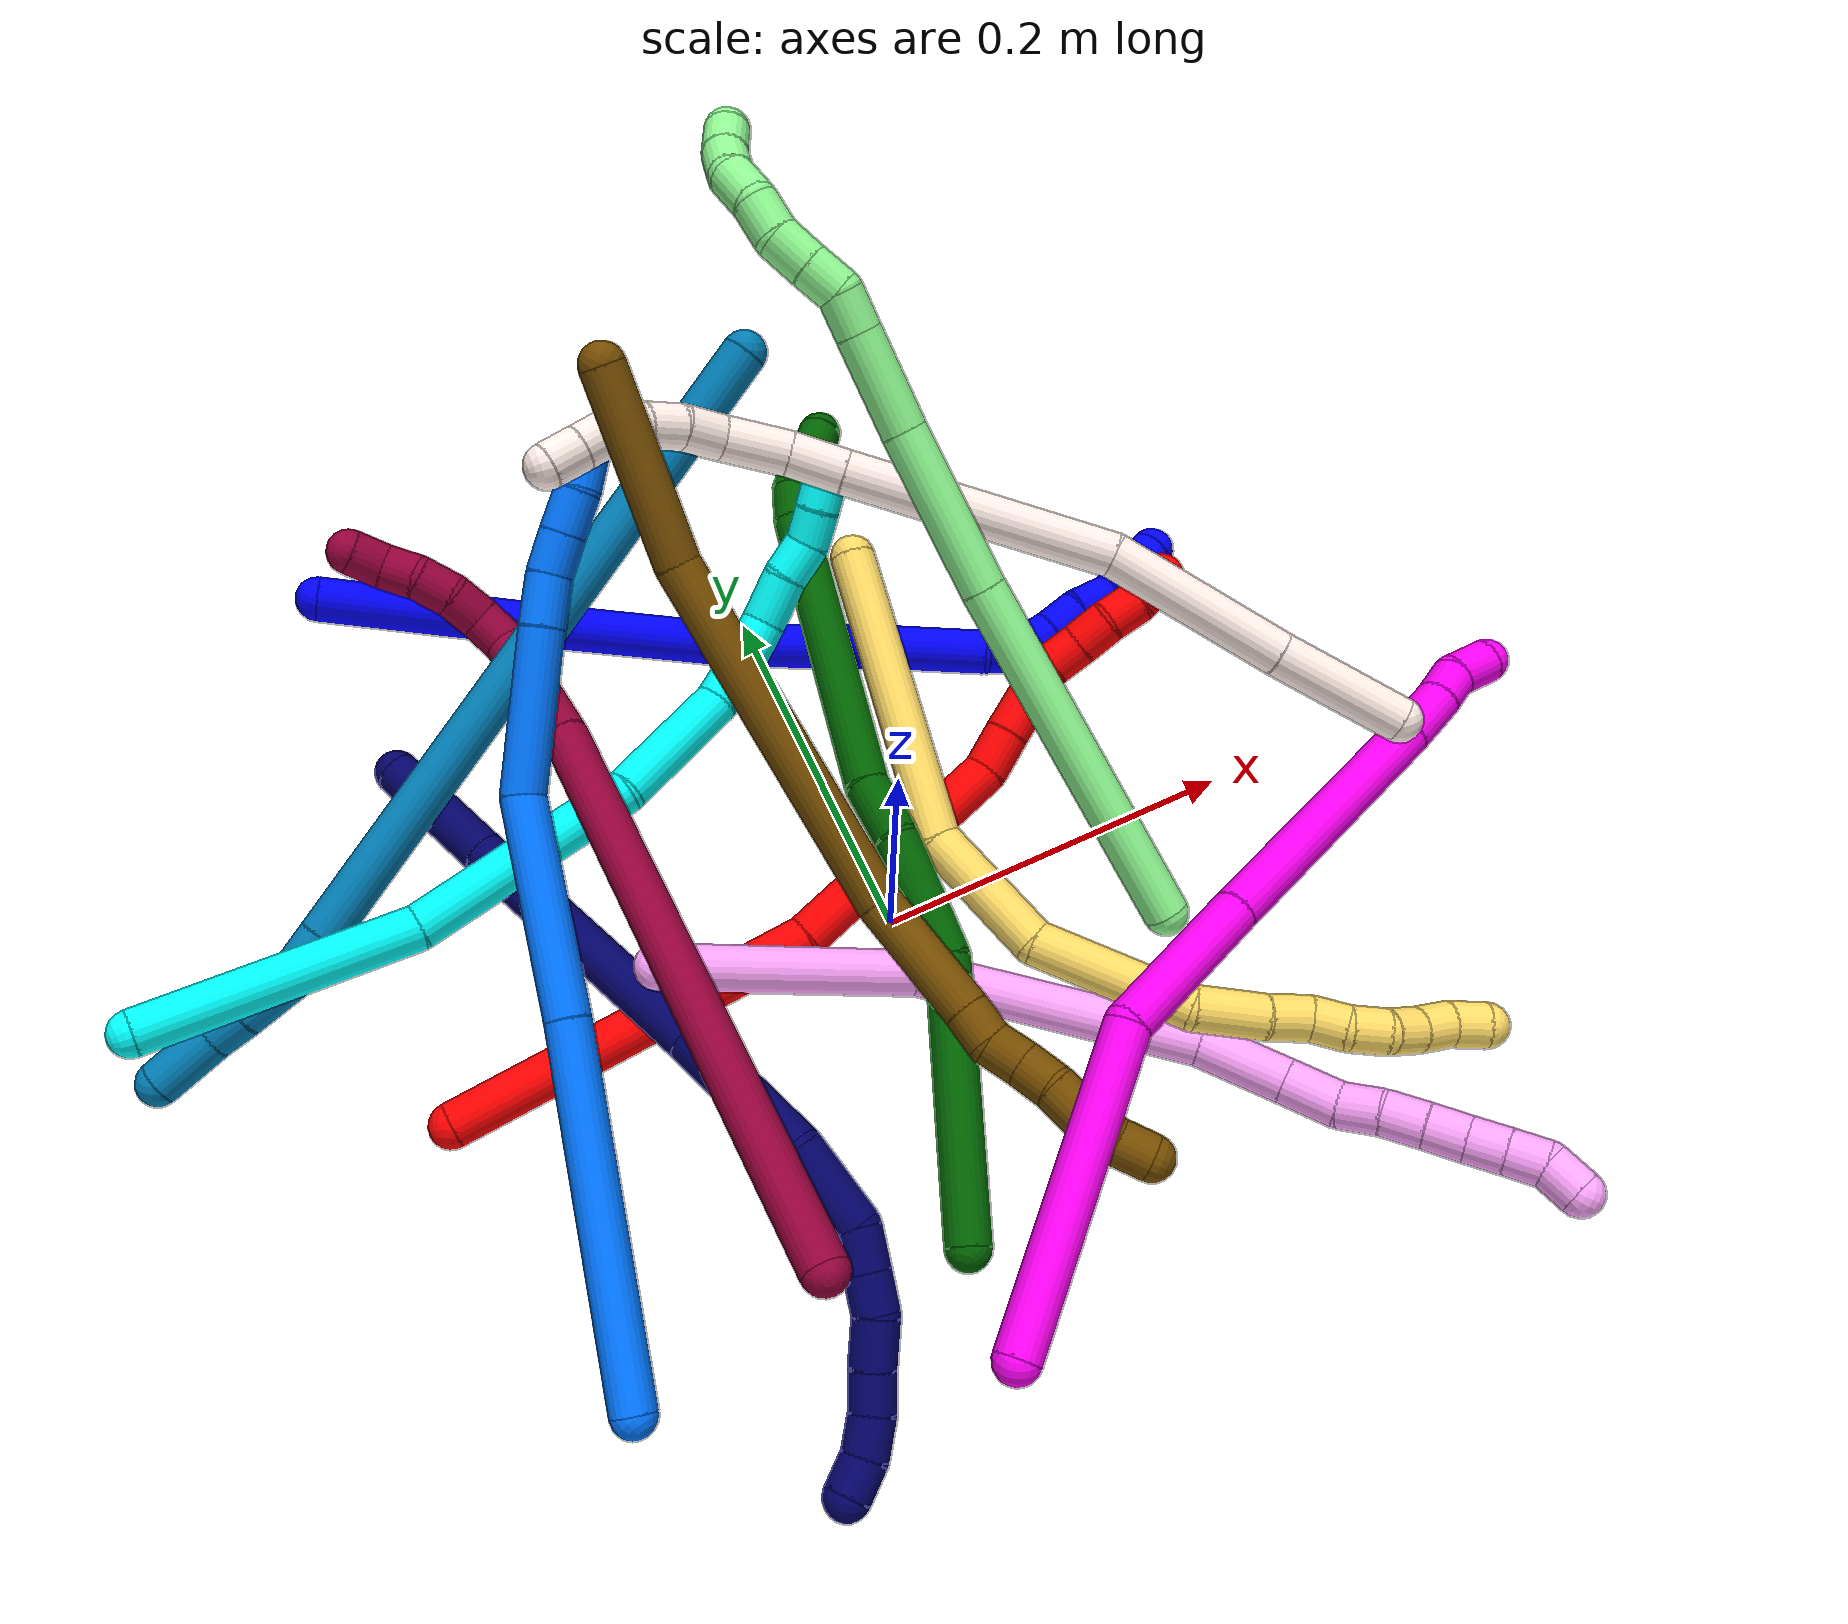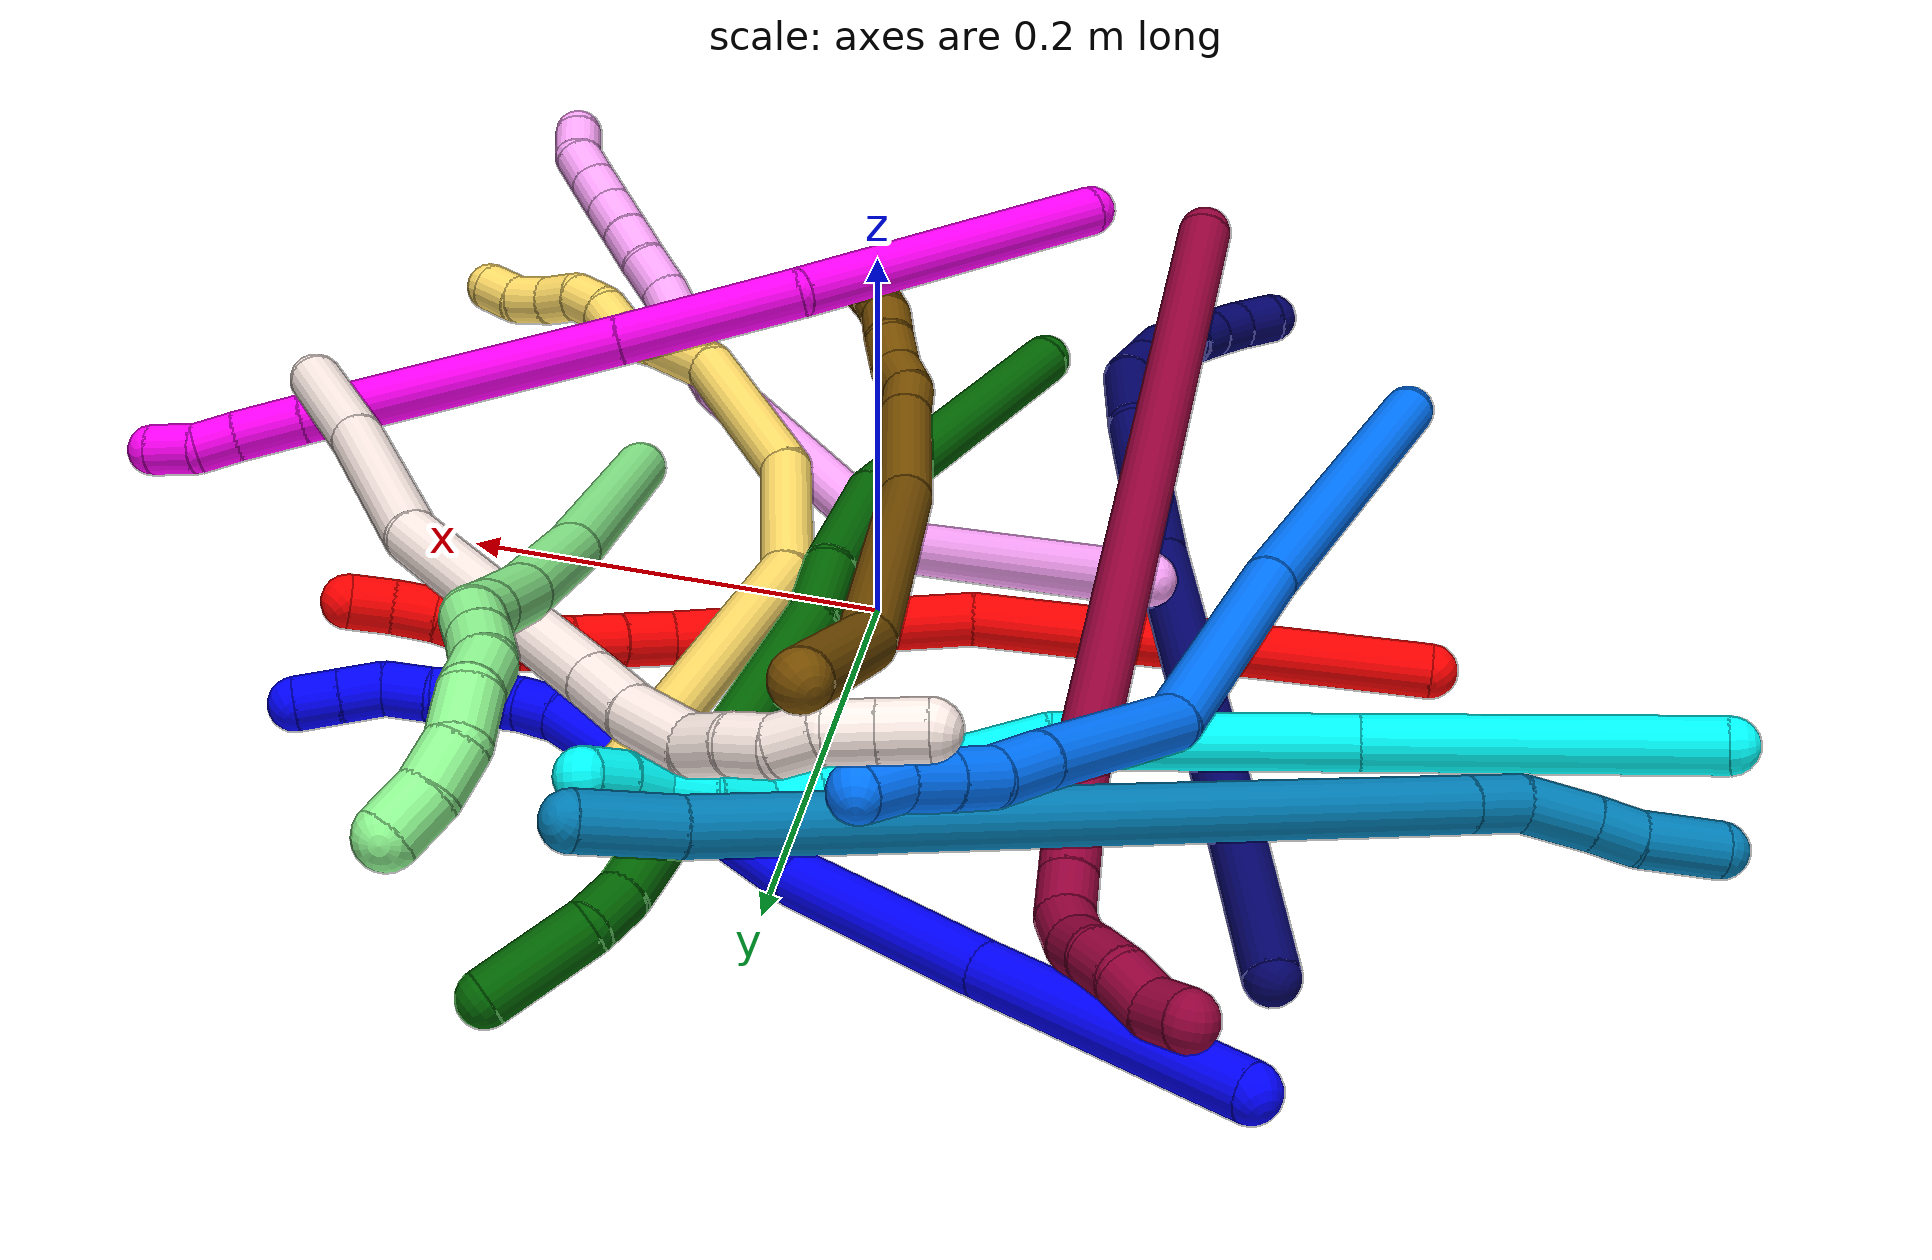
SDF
<sdf version="1.7">
 <world name="default">
  <plugin name="TubeGeneratorPlugin" filename="libtube_generator_plugin.so"/>
  <model name="photoneo_s_sensor">
   <static>1</static>
   <pose>0 0 2 1.57079 1.57079 3.14159</pose>
   <link name="link">
    <inertial><mass>0.1</mass></inertial>
    <sensor name="sensor" type="depth">
     <update_rate>30</update_rate>
     <camera>
      <horizontal_fov>1.22</horizontal_fov>
      <image><width>1920</width><height>1200</height><format>B8G8R8</format></image>
      <clip><near>0.1</near><far>4</far></clip>
      <depth_camera><output>points</output></depth_camera>
     </camera>
     <plugin name="camera_plugin" filename="libgazebo_ros_depth_camera.so">
      <baseline>0.2</baseline>
      <alwaysOn>1</alwaysOn>
      <updateRate>0.0</updateRate>
      <cameraName>camera_ir</cameraName>
      <imageTopicName>/camera/color/image_raw</imageTopicName>
      <cameraInfoTopicName>/camera/color/camera_info</cameraInfoTopicName>
      <depthImageTopicName>/camera/depth/image_raw</depthImageTopicName>
      <depthImageCameraInfoTopicName>/camera/depth/camera_info</depthImageCameraInfoTopicName>
      <pointCloudTopicName>/camera/depth/points</pointCloudTopicName>
      <frameName>fr_optical</frameName>
      <pointCloudCutoff>0.1</pointCloudCutoff>
      <pointCloudCutoffMax>2.0</pointCloudCutoffMax>
      <distortionK1>0</distortionK1>
      <distortionK2>0</distortionK2>
      <distortionK3>0</distortionK3>
      <distortionT1>0</distortionT1>
      <distortionT2>0</distortionT2>
      <CxPrime>0</CxPrime>
      <Cx>0</Cx>
      <Cy>0</Cy>
      <focalLength>0</focalLength>
      <hackBaseline>0</hackBaseline>
     </plugin>
    </sensor>
   </link>
  </model>
  <gravity>0 0 -9.8</gravity>
  <magnetic_field>6e-06 2.3e-05 -4.2e-05</magnetic_field>
  <atmosphere type="adiabatic"/>
  <physics name="default_physics" default="0" type="ode">
   <max_step_size>0.003</max_step_size>
   <real_time_factor>1</real_time_factor>
   <real_time_update_rate>1000</real_time_update_rate>
   <max_contacts>10000</max_contacts>
   <ode>
    <solver>
     <type>quick</type>
     <iters>100</iters>
     <sor>1.3</sor>
     <use_dynamic_moi_rescaling>0</use_dynamic_moi_rescaling>
    </solver>
    <constraints>
     <contact_max_correcting_vel>0</contact_max_correcting_vel>
     <contact_surface_layer>0.001</contact_surface_layer>
     <cfm>0</cfm>
     <erp>0.2</erp>
    </constraints>
   </ode>
  </physics>
  <scene><ambient>0.4 0.4 0.4 1</ambient><background>0.7 0.7 0.7 1</background><shadows>0</shadows></scene>
  <audio><device>default</device></audio>
  <spherical_coordinates>
   <surface_model>EARTH_WGS84</surface_model>
   <latitude_deg>0</latitude_deg>
   <longitude_deg>0</longitude_deg>
   <elevation>0</elevation>
   <heading_deg>0</heading_deg>
  </spherical_coordinates>
  <model name="bin">
   <static>1</static>
   <link name="bottom">
    <collision name="collision-bottom">
     <pose>0 0 -0.01 0 -0 0</pose>
     <geometry><box><size>0.8 0.6 0.02</size></box></geometry>
     <surface>
      <friction><ode><mu>100</mu><mu2>100</mu2></ode></friction>
      <contact><collide_bitmask>65535</collide_bitmask></contact>
     </surface>
    </collision>
   </link>
   <link name="west_wall">
    <collision name="collision-west_wall">
     <pose>-0.41 0 0.1 0 -0 0</pose>
     <geometry><box><size>0.02 0.6 0.2</size></box></geometry>
     <surface>
      <friction><ode><mu>100</mu><mu2>100</mu2></ode></friction>
      <contact><collide_bitmask>65535</collide_bitmask></contact>
     </surface>
    </collision>
   </link>
   <link name="east_wall">
    <collision name="collision-east_wall">
     <pose>0.41 0 0.1 0 -0 0</pose>
     <geometry><box><size>0.02 0.6 0.2</size></box></geometry>
     <surface>
      <friction><ode><mu>100</mu><mu2>100</mu2></ode></friction>
      <contact><collide_bitmask>65535</collide_bitmask></contact>
     </surface>
    </collision>
   </link>
   <link name="south_wall">
    <collision name="collision-south_wall">
     <pose>0 -0.31 0.1 0 -0 0</pose>
     <geometry><box><size>0.8 0.02 0.2</size></box></geometry>
     <surface>
      <friction><ode><mu>100</mu><mu2>100</mu2></ode></friction>
      <contact><collide_bitmask>65535</collide_bitmask></contact>
     </surface>
    </collision>
   </link>
   <link name="north_wall">
    <collision name="collision-north_wall">
     <pose>0 0.31 0.1 0 -0 0</pose>
     <geometry><box><size>0.8 0.02 0.2</size></box></geometry>
     <surface>
      <friction><ode><mu>100</mu><mu2>100</mu2></ode></friction>
      <contact><collide_bitmask>65535</collide_bitmask></contact>
     </surface>
    </collision>
   </link>
  </model>
  <model name="1">
   <static>0</static>
   <link name="1">
    <collision name="collision-cylinder-e_1_1_4">
     <pose>0.032249 -0.010098 -0.055538 2.96174 0.519046 2.48681</pose>
     <geometry><cylinder><radius>0.0125</radius><length>0.130023</length></cylinder></geometry>
     <surface>
      <friction><ode><mu>1.16</mu><mu2>1.16</mu2><slip1>0</slip1><slip2>0</slip2></ode></friction>
      <contact><ode><kp>1e+06</kp><kd>1</kd><max_vel>0</max_vel><min_depth>0.001</min_depth></ode></contact>
     </surface>
    </collision>
    <visual name="visual-cylinder-e_1_1_4">
     <pose>0.032249 -0.010098 -0.055538 2.96174 0.519046 2.48681</pose>
     <geometry><cylinder><radius>0.0125</radius><length>0.130023</length></cylinder></geometry>
     <material><ambient>0 0 1 1</ambient></material>
    </visual>
    <collision name="collision-cylinder-e_2_4_5">
     <pose>0.088818 -0.029358 -0.155503 2.93822 0.492142 2.36981</pose>
     <geometry><cylinder><radius>0.0125</radius><length>0.102939</length></cylinder></geometry>
     <surface>
      <friction><ode><mu>1.16</mu><mu2>1.16</mu2><slip1>0</slip1><slip2>0</slip2></ode></friction>
      <contact><ode><kp>1e+06</kp><kd>1</kd><max_vel>0</max_vel><min_depth>0.001</min_depth></ode></contact>
     </surface>
    </collision>
    <visual name="visual-cylinder-e_2_4_5">
     <pose>0.088818 -0.029358 -0.155503 2.93822 0.492142 2.36981</pose>
     <geometry><cylinder><radius>0.0125</radius><length>0.102939</length></cylinder></geometry>
     <material><ambient>0 0 1 1</ambient></material>
    </visual>
    <collision name="collision-cylinder-e_3_5_6">
     <pose>0.126631 -0.052566 -0.240502 2.80829 0.304481 1.47895</pose>
     <geometry><cylinder><radius>0.0125</radius><length>0.09001</length></cylinder></geometry>
     <surface>
      <friction><ode><mu>1.16</mu><mu2>1.16</mu2><slip1>0</slip1><slip2>0</slip2></ode></friction>
      <contact><ode><kp>1e+06</kp><kd>1</kd><max_vel>0</max_vel><min_depth>0.001</min_depth></ode></contact>
     </surface>
    </collision>
    <visual name="visual-cylinder-e_3_5_6">
     <pose>0.126631 -0.052566 -0.240502 2.80829 0.304481 1.47895</pose>
     <geometry><cylinder><radius>0.0125</radius><length>0.09001</length></cylinder></geometry>
     <material><ambient>0 0 1 1</ambient></material>
    </visual>
    <collision name="collision-cylinder-e_4_6_7">
     <pose>0.149401 -0.073584 -0.304795 2.85575 0.358994 1.80059</pose>
     <geometry><cylinder><radius>0.0125</radius><length>0.052816</length></cylinder></geometry>
     <surface>
      <friction><ode><mu>1.16</mu><mu2>1.16</mu2><slip1>0</slip1><slip2>0</slip2></ode></friction>
      <contact><ode><kp>1e+06</kp><kd>1</kd><max_vel>0</max_vel><min_depth>0.001</min_depth></ode></contact>
     </surface>
    </collision>
    <visual name="visual-cylinder-e_4_6_7">
     <pose>0.149401 -0.073584 -0.304795 2.85575 0.358994 1.80059</pose>
     <geometry><cylinder><radius>0.0125</radius><length>0.052816</length></cylinder></geometry>
     <material><ambient>0 0 1 1</ambient></material>
    </visual>
    <collision name="collision-cylinder-e_5_7_8">
     <pose>0.164653 -0.083733 -0.336788 2.77488 0.593164 2.05076</pose>
     <geometry><cylinder><radius>0.0125</radius><length>0.021373</length></cylinder></geometry>
     <surface>
      <friction><ode><mu>1.16</mu><mu2>1.16</mu2><slip1>0</slip1><slip2>0</slip2></ode></friction>
      <contact><ode><kp>1e+06</kp><kd>1</kd><max_vel>0</max_vel><min_depth>0.001</min_depth></ode></contact>
     </surface>
    </collision>
    <visual name="visual-cylinder-e_5_7_8">
     <pose>0.164653 -0.083733 -0.336788 2.77488 0.593164 2.05076</pose>
     <geometry><cylinder><radius>0.0125</radius><length>0.021373</length></cylinder></geometry>
     <material><ambient>0 0 1 1</ambient></material>
    </visual>
    <collision name="collision-cylinder-e_6_8_9">
     <pose>0.176046 -0.093928 -0.350155 2.19879 0.558534 1.02489</pose>
     <geometry><cylinder><radius>0.0125</radius><length>0.020455</length></cylinder></geometry>
     <surface>
      <friction><ode><mu>1.16</mu><mu2>1.16</mu2><slip1>0</slip1><slip2>0</slip2></ode></friction>
      <contact><ode><kp>1e+06</kp><kd>1</kd><max_vel>0</max_vel><min_depth>0.001</min_depth></ode></contact>
     </surface>
    </collision>
    <visual name="visual-cylinder-e_6_8_9">
     <pose>0.176046 -0.093928 -0.350155 2.19879 0.558534 1.02489</pose>
     <geometry><cylinder><radius>0.0125</radius><length>0.020455</length></cylinder></geometry>
     <material><ambient>0 0 1 1</ambient></material>
    </visual>
    <collision name="collision-cylinder-e_7_9_10">
     <pose>0.187081 -0.10854 -0.359414 2.07233 0.575223 0.92658</pose>
     <geometry><cylinder><radius>0.0125</radius><length>0.020641</length></cylinder></geometry>
     <surface>
      <friction><ode><mu>1.16</mu><mu2>1.16</mu2><slip1>0</slip1><slip2>0</slip2></ode></friction>
      <contact><ode><kp>1e+06</kp><kd>1</kd><max_vel>0</max_vel><min_depth>0.001</min_depth></ode></contact>
     </surface>
    </collision>
    <visual name="visual-cylinder-e_7_9_10">
     <pose>0.187081 -0.10854 -0.359414 2.07233 0.575223 0.92658</pose>
     <geometry><cylinder><radius>0.0125</radius><length>0.020641</length></cylinder></geometry>
     <material><ambient>0 0 1 1</ambient></material>
    </visual>
    <collision name="collision-cylinder-e_8_10_11">
     <pose>0.198848 -0.122548 -0.369611 2.32548 0.609813 1.25852</pose>
     <geometry><cylinder><radius>0.0125</radius><length>0.021486</length></cylinder></geometry>
     <surface>
      <friction><ode><mu>1.16</mu><mu2>1.16</mu2><slip1>0</slip1><slip2>0</slip2></ode></friction>
      <contact><ode><kp>1e+06</kp><kd>1</kd><max_vel>0</max_vel><min_depth>0.001</min_depth></ode></contact>
     </surface>
    </collision>
    <visual name="visual-cylinder-e_8_10_11">
     <pose>0.198848 -0.122548 -0.369611 2.32548 0.609813 1.25852</pose>
     <geometry><cylinder><radius>0.0125</radius><length>0.021486</length></cylinder></geometry>
     <material><ambient>0 0 1 1</ambient></material>
    </visual>
    <collision name="collision-cylinder-e_9_11_12">
     <pose>0.21184 -0.136151 -0.377579 1.83385 0.743139 0.940828</pose>
     <geometry><cylinder><radius>0.0125</radius><length>0.020216</length></cylinder></geometry>
     <surface>
      <friction><ode><mu>1.16</mu><mu2>1.16</mu2><slip1>0</slip1><slip2>0</slip2></ode></friction>
      <contact><ode><kp>1e+06</kp><kd>1</kd><max_vel>0</max_vel><min_depth>0.001</min_depth></ode></contact>
     </surface>
    </collision>
    <visual name="visual-cylinder-e_9_11_12">
     <pose>0.21184 -0.136151 -0.377579 1.83385 0.743139 0.940828</pose>
     <geometry><cylinder><radius>0.0125</radius><length>0.020216</length></cylinder></geometry>
     <material><ambient>0 0 1 1</ambient></material>
    </visual>
    <collision name="collision-cylinder-e_10_12_2">
     <pose>0.225478 -0.150438 -0.381457 1.83785 0.745704 0.947253</pose>
     <geometry><cylinder><radius>0.0125</radius><length>0.020042</length></cylinder></geometry>
     <surface>
      <friction><ode><mu>1.16</mu><mu2>1.16</mu2><slip1>0</slip1><slip2>0</slip2></ode></friction>
      <contact><ode><kp>1e+06</kp><kd>1</kd><max_vel>0</max_vel><min_depth>0.001</min_depth></ode></contact>
     </surface>
    </collision>
    <visual name="visual-cylinder-e_10_12_2">
     <pose>0.225478 -0.150438 -0.381457 1.83785 0.745704 0.947253</pose>
     <geometry><cylinder><radius>0.0125</radius><length>0.020042</length></cylinder></geometry>
     <material><ambient>0 0 1 1</ambient></material>
    </visual>
    <collision name="collision-sphere-2">
     <pose>0.232277 -0.157539 -0.3834 0 -0 0</pose>
     <geometry><sphere><radius>0.0125</radius></sphere></geometry>
     <surface>
      <friction><ode><mu>1.16</mu><mu2>1.16</mu2><slip1>0</slip1><slip2>0</slip2></ode></friction>
      <contact><ode><kp>1e+06</kp><kd>1</kd><max_vel>0</max_vel><min_depth>0.001</min_depth></ode></contact>
     </surface>
    </collision>
    <visual name="visual-sphere-2">
     <pose>0.232277 -0.157539 -0.3834 0 -0 0</pose>
     <geometry><sphere><radius>0.0125</radius></sphere></geometry>
     <material><ambient>0 0 1 1</ambient></material>
    </visual>
    <collision name="collision-sphere-12">
     <pose>0.218679 -0.143338 -0.379515 0 -0 0</pose>
     <geometry><sphere><radius>0.0125</radius></sphere></geometry>
     <surface>
      <friction><ode><mu>1.16</mu><mu2>1.16</mu2><slip1>0</slip1><slip2>0</slip2></ode></friction>
      <contact><ode><kp>1e+06</kp><kd>1</kd><max_vel>0</max_vel><min_depth>0.001</min_depth></ode></contact>
     </surface>
    </collision>
    <visual name="visual-sphere-12">
     <pose>0.218679 -0.143338 -0.379515 0 -0 0</pose>
     <geometry><sphere><radius>0.0125</radius></sphere></geometry>
     <material><ambient>0 0 1 1</ambient></material>
    </visual>
    <collision name="collision-sphere-11">
     <pose>0.205 -0.128964 -0.375644 0 -0 0</pose>
     <geometry><sphere><radius>0.0125</radius></sphere></geometry>
     <surface>
      <friction><ode><mu>1.16</mu><mu2>1.16</mu2><slip1>0</slip1><slip2>0</slip2></ode></friction>
      <contact><ode><kp>1e+06</kp><kd>1</kd><max_vel>0</max_vel><min_depth>0.001</min_depth></ode></contact>
     </surface>
    </collision>
    <visual name="visual-sphere-11">
     <pose>0.205 -0.128964 -0.375644 0 -0 0</pose>
     <geometry><sphere><radius>0.0125</radius></sphere></geometry>
     <material><ambient>0 0 1 1</ambient></material>
    </visual>
    <collision name="collision-sphere-10">
     <pose>0.192695 -0.116133 -0.363578 0 -0 0</pose>
     <geometry><sphere><radius>0.0125</radius></sphere></geometry>
     <surface>
      <friction><ode><mu>1.16</mu><mu2>1.16</mu2><slip1>0</slip1><slip2>0</slip2></ode></friction>
      <contact><ode><kp>1e+06</kp><kd>1</kd><max_vel>0</max_vel><min_depth>0.001</min_depth></ode></contact>
     </surface>
    </collision>
    <visual name="visual-sphere-10">
     <pose>0.192695 -0.116133 -0.363578 0 -0 0</pose>
     <geometry><sphere><radius>0.0125</radius></sphere></geometry>
     <material><ambient>0 0 1 1</ambient></material>
    </visual>
    <collision name="collision-sphere-9">
     <pose>0.181466 -0.100947 -0.355251 0 -0 0</pose>
     <geometry><sphere><radius>0.0125</radius></sphere></geometry>
     <surface>
      <friction><ode><mu>1.16</mu><mu2>1.16</mu2><slip1>0</slip1><slip2>0</slip2></ode></friction>
      <contact><ode><kp>1e+06</kp><kd>1</kd><max_vel>0</max_vel><min_depth>0.001</min_depth></ode></contact>
     </surface>
    </collision>
    <visual name="visual-sphere-9">
     <pose>0.181466 -0.100947 -0.355251 0 -0 0</pose>
     <geometry><sphere><radius>0.0125</radius></sphere></geometry>
     <material><ambient>0 0 1 1</ambient></material>
    </visual>
    <collision name="collision-sphere-4">
     <pose>0.064498 -0.020196 -0.111077 0 -0 0</pose>
     <geometry><sphere><radius>0.0125</radius></sphere></geometry>
     <surface>
      <friction><ode><mu>1.16</mu><mu2>1.16</mu2><slip1>0</slip1><slip2>0</slip2></ode></friction>
      <contact><ode><kp>1e+06</kp><kd>1</kd><max_vel>0</max_vel><min_depth>0.001</min_depth></ode></contact>
     </surface>
    </collision>
    <visual name="visual-sphere-4">
     <pose>0.064498 -0.020196 -0.111077 0 -0 0</pose>
     <geometry><sphere><radius>0.0125</radius></sphere></geometry>
     <material><ambient>0 0 1 1</ambient></material>
    </visual>
    <collision name="collision-sphere-1">
     <geometry><sphere><radius>0.0125</radius></sphere></geometry>
     <surface>
      <friction><ode><mu>1.16</mu><mu2>1.16</mu2><slip1>0</slip1><slip2>0</slip2></ode></friction>
      <contact><ode><kp>1e+06</kp><kd>1</kd><max_vel>0</max_vel><min_depth>0.001</min_depth></ode></contact>
     </surface>
    </collision>
    <visual name="visual-sphere-1">
     <geometry><sphere><radius>0.0125</radius></sphere></geometry>
     <material><ambient>0 0 1 1</ambient></material>
    </visual>
    <collision name="collision-sphere-8">
     <pose>0.170626 -0.08691 -0.34506 0 -0 0</pose>
     <geometry><sphere><radius>0.0125</radius></sphere></geometry>
     <surface>
      <friction><ode><mu>1.16</mu><mu2>1.16</mu2><slip1>0</slip1><slip2>0</slip2></ode></friction>
      <contact><ode><kp>1e+06</kp><kd>1</kd><max_vel>0</max_vel><min_depth>0.001</min_depth></ode></contact>
     </surface>
    </collision>
    <visual name="visual-sphere-8">
     <pose>0.170626 -0.08691 -0.34506 0 -0 0</pose>
     <geometry><sphere><radius>0.0125</radius></sphere></geometry>
     <material><ambient>0 0 1 1</ambient></material>
    </visual>
    <collision name="collision-sphere-5">
     <pose>0.113138 -0.038519 -0.19993 0 -0 0</pose>
     <geometry><sphere><radius>0.0125</radius></sphere></geometry>
     <surface>
      <friction><ode><mu>1.16</mu><mu2>1.16</mu2><slip1>0</slip1><slip2>0</slip2></ode></friction>
      <contact><ode><kp>1e+06</kp><kd>1</kd><max_vel>0</max_vel><min_depth>0.001</min_depth></ode></contact>
     </surface>
    </collision>
    <visual name="visual-sphere-5">
     <pose>0.113138 -0.038519 -0.19993 0 -0 0</pose>
     <geometry><sphere><radius>0.0125</radius></sphere></geometry>
     <material><ambient>0 0 1 1</ambient></material>
    </visual>
    <collision name="collision-sphere-6">
     <pose>0.140123 -0.066613 -0.281074 0 -0 0</pose>
     <geometry><sphere><radius>0.0125</radius></sphere></geometry>
     <surface>
      <friction><ode><mu>1.16</mu><mu2>1.16</mu2><slip1>0</slip1><slip2>0</slip2></ode></friction>
      <contact><ode><kp>1e+06</kp><kd>1</kd><max_vel>0</max_vel><min_depth>0.001</min_depth></ode></contact>
     </surface>
    </collision>
    <visual name="visual-sphere-6">
     <pose>0.140123 -0.066613 -0.281074 0 -0 0</pose>
     <geometry><sphere><radius>0.0125</radius></sphere></geometry>
     <material><ambient>0 0 1 1</ambient></material>
    </visual>
    <collision name="collision-sphere-7">
     <pose>0.158679 -0.080556 -0.328516 0 -0 0</pose>
     <geometry><sphere><radius>0.0125</radius></sphere></geometry>
     <surface>
      <friction><ode><mu>1.16</mu><mu2>1.16</mu2><slip1>0</slip1><slip2>0</slip2></ode></friction>
      <contact><ode><kp>1e+06</kp><kd>1</kd><max_vel>0</max_vel><min_depth>0.001</min_depth></ode></contact>
     </surface>
    </collision>
    <visual name="visual-sphere-7">
     <pose>0.158679 -0.080556 -0.328516 0 -0 0</pose>
     <geometry><sphere><radius>0.0125</radius></sphere></geometry>
     <material><ambient>0 0 1 1</ambient></material>
    </visual>
    <inertial>
     <pose>0.113361 -0.054609 -0.211946 0 -0 0</pose>
     <mass>0.5</mass>
     <inertia>
      <ixx>7.2e-05</ixx>
      <ixy>0</ixy>
      <ixz>0</ixz>
      <iyy>0.000464</iyy>
      <iyz>0</iyz>
      <izz>-0.000122</izz>
     </inertia>
    </inertial>
   </link>
   <pose>-0.215986 0.28825 0.054127 -1.72462 0.873658 0.527533</pose>
  </model>
  <model name="2">
   <static>0</static>
   <link name="2">
    <collision name="collision-cylinder-e_1_1_4">
     <pose>0.08205 0.028213 -0.058951 -2.69522 0.898183 -2.26132</pose>
     <geometry><cylinder><radius>0.0125</radius><length>0.209794</length></cylinder></geometry>
     <surface>
      <friction><ode><mu>1.16</mu><mu2>1.16</mu2><slip1>0</slip1><slip2>0</slip2></ode></friction>
      <contact><ode><kp>1e+06</kp><kd>1</kd><max_vel>0</max_vel><min_depth>0.001</min_depth></ode></contact>
     </surface>
    </collision>
    <visual name="visual-cylinder-e_1_1_4">
     <pose>0.08205 0.028213 -0.058951 -2.69522 0.898183 -2.26132</pose>
     <geometry><cylinder><radius>0.0125</radius><length>0.209794</length></cylinder></geometry>
     <material><ambient>1 0 0 1</ambient></material>
    </visual>
    <collision name="collision-cylinder-e_2_4_5">
     <pose>0.206092 0.074731 -0.170256 -2.80524 0.648044 -2.2055</pose>
     <geometry><cylinder><radius>0.0125</radius><length>0.139132</length></cylinder></geometry>
     <surface>
      <friction><ode><mu>1.16</mu><mu2>1.16</mu2><slip1>0</slip1><slip2>0</slip2></ode></friction>
      <contact><ode><kp>1e+06</kp><kd>1</kd><max_vel>0</max_vel><min_depth>0.001</min_depth></ode></contact>
     </surface>
    </collision>
    <visual name="visual-cylinder-e_2_4_5">
     <pose>0.206092 0.074731 -0.170256 -2.80524 0.648044 -2.2055</pose>
     <geometry><cylinder><radius>0.0125</radius><length>0.139132</length></cylinder></geometry>
     <material><ambient>1 0 0 1</ambient></material>
    </visual>
    <collision name="collision-cylinder-e_3_5_6">
     <pose>0.25214 0.098908 -0.232823 -2.61978 0.331608 -1.11974</pose>
     <geometry><cylinder><radius>0.0125</radius><length>0.024917</length></cylinder></geometry>
     <surface>
      <friction><ode><mu>1.16</mu><mu2>1.16</mu2><slip1>0</slip1><slip2>0</slip2></ode></friction>
      <contact><ode><kp>1e+06</kp><kd>1</kd><max_vel>0</max_vel><min_depth>0.001</min_depth></ode></contact>
     </surface>
    </collision>
    <visual name="visual-cylinder-e_3_5_6">
     <pose>0.25214 0.098908 -0.232823 -2.61978 0.331608 -1.11974</pose>
     <geometry><cylinder><radius>0.0125</radius><length>0.024917</length></cylinder></geometry>
     <material><ambient>1 0 0 1</ambient></material>
    </visual>
    <collision name="collision-cylinder-e_4_6_7">
     <pose>0.260304 0.110047 -0.252635 -2.63971 0.358893 -1.23165</pose>
     <geometry><cylinder><radius>0.0125</radius><length>0.023391</length></cylinder></geometry>
     <surface>
      <friction><ode><mu>1.16</mu><mu2>1.16</mu2><slip1>0</slip1><slip2>0</slip2></ode></friction>
      <contact><ode><kp>1e+06</kp><kd>1</kd><max_vel>0</max_vel><min_depth>0.001</min_depth></ode></contact>
     </surface>
    </collision>
    <visual name="visual-cylinder-e_4_6_7">
     <pose>0.260304 0.110047 -0.252635 -2.63971 0.358893 -1.23165</pose>
     <geometry><cylinder><radius>0.0125</radius><length>0.023391</length></cylinder></geometry>
     <material><ambient>1 0 0 1</ambient></material>
    </visual>
    <collision name="collision-cylinder-e_5_7_8">
     <pose>0.268668 0.120168 -0.270877 -2.62993 0.405658 -1.33261</pose>
     <geometry><cylinder><radius>0.0125</radius><length>0.021573</length></cylinder></geometry>
     <surface>
      <friction><ode><mu>1.16</mu><mu2>1.16</mu2><slip1>0</slip1><slip2>0</slip2></ode></friction>
      <contact><ode><kp>1e+06</kp><kd>1</kd><max_vel>0</max_vel><min_depth>0.001</min_depth></ode></contact>
     </surface>
    </collision>
    <visual name="visual-cylinder-e_5_7_8">
     <pose>0.268668 0.120168 -0.270877 -2.62993 0.405658 -1.33261</pose>
     <geometry><cylinder><radius>0.0125</radius><length>0.021573</length></cylinder></geometry>
     <material><ambient>1 0 0 1</ambient></material>
    </visual>
    <collision name="collision-cylinder-e_6_8_9">
     <pose>0.279511 0.130794 -0.284959 -2.32657 0.692909 -1.39298</pose>
     <geometry><cylinder><radius>0.0125</radius><length>0.02062</length></cylinder></geometry>
     <surface>
      <friction><ode><mu>1.16</mu><mu2>1.16</mu2><slip1>0</slip1><slip2>0</slip2></ode></friction>
      <contact><ode><kp>1e+06</kp><kd>1</kd><max_vel>0</max_vel><min_depth>0.001</min_depth></ode></contact>
     </surface>
    </collision>
    <visual name="visual-cylinder-e_6_8_9">
     <pose>0.279511 0.130794 -0.284959 -2.32657 0.692909 -1.39298</pose>
     <geometry><cylinder><radius>0.0125</radius><length>0.02062</length></cylinder></geometry>
     <material><ambient>1 0 0 1</ambient></material>
    </visual>
    <collision name="collision-cylinder-e_7_9_10">
     <pose>0.292337 0.142726 -0.295693 -2.28079 0.65523 -1.27449</pose>
     <geometry><cylinder><radius>0.0125</radius><length>0.020485</length></cylinder></geometry>
     <surface>
      <friction><ode><mu>1.16</mu><mu2>1.16</mu2><slip1>0</slip1><slip2>0</slip2></ode></friction>
      <contact><ode><kp>1e+06</kp><kd>1</kd><max_vel>0</max_vel><min_depth>0.001</min_depth></ode></contact>
     </surface>
    </collision>
    <visual name="visual-cylinder-e_7_9_10">
     <pose>0.292337 0.142726 -0.295693 -2.28079 0.65523 -1.27449</pose>
     <geometry><cylinder><radius>0.0125</radius><length>0.020485</length></cylinder></geometry>
     <material><ambient>1 0 0 1</ambient></material>
    </visual>
    <collision name="collision-cylinder-e_8_10_11">
     <pose>0.305637 0.153062 -0.306717 -2.51166 0.783093 -1.80542</pose>
     <geometry><cylinder><radius>0.0125</radius><length>0.020011</length></cylinder></geometry>
     <surface>
      <friction><ode><mu>1.16</mu><mu2>1.16</mu2><slip1>0</slip1><slip2>0</slip2></ode></friction>
      <contact><ode><kp>1e+06</kp><kd>1</kd><max_vel>0</max_vel><min_depth>0.001</min_depth></ode></contact>
     </surface>
    </collision>
    <visual name="visual-cylinder-e_8_10_11">
     <pose>0.305637 0.153062 -0.306717 -2.51166 0.783093 -1.80542</pose>
     <geometry><cylinder><radius>0.0125</radius><length>0.020011</length></cylinder></geometry>
     <material><ambient>1 0 0 1</ambient></material>
    </visual>
    <collision name="collision-cylinder-e_9_11_2">
     <pose>0.318007 0.162213 -0.319363 -2.51814 0.557538 -1.45257</pose>
     <geometry><cylinder><radius>0.0125</radius><length>0.020078</length></cylinder></geometry>
     <surface>
      <friction><ode><mu>1.16</mu><mu2>1.16</mu2><slip1>0</slip1><slip2>0</slip2></ode></friction>
      <contact><ode><kp>1e+06</kp><kd>1</kd><max_vel>0</max_vel><min_depth>0.001</min_depth></ode></contact>
     </surface>
    </collision>
    <visual name="visual-cylinder-e_9_11_2">
     <pose>0.318007 0.162213 -0.319363 -2.51814 0.557538 -1.45257</pose>
     <geometry><cylinder><radius>0.0125</radius><length>0.020078</length></cylinder></geometry>
     <material><ambient>1 0 0 1</ambient></material>
    </visual>
    <collision name="collision-sphere-2">
     <pose>0.323319 0.167186 -0.326279 0 -0 0</pose>
     <geometry><sphere><radius>0.0125</radius></sphere></geometry>
     <surface>
      <friction><ode><mu>1.16</mu><mu2>1.16</mu2><slip1>0</slip1><slip2>0</slip2></ode></friction>
      <contact><ode><kp>1e+06</kp><kd>1</kd><max_vel>0</max_vel><min_depth>0.001</min_depth></ode></contact>
     </surface>
    </collision>
    <visual name="visual-sphere-2">
     <pose>0.323319 0.167186 -0.326279 0 -0 0</pose>
     <geometry><sphere><radius>0.0125</radius></sphere></geometry>
     <material><ambient>1 0 0 1</ambient></material>
    </visual>
    <collision name="collision-sphere-11">
     <pose>0.312696 0.157239 -0.312447 0 -0 0</pose>
     <geometry><sphere><radius>0.0125</radius></sphere></geometry>
     <surface>
      <friction><ode><mu>1.16</mu><mu2>1.16</mu2><slip1>0</slip1><slip2>0</slip2></ode></friction>
      <contact><ode><kp>1e+06</kp><kd>1</kd><max_vel>0</max_vel><min_depth>0.001</min_depth></ode></contact>
     </surface>
    </collision>
    <visual name="visual-sphere-11">
     <pose>0.312696 0.157239 -0.312447 0 -0 0</pose>
     <geometry><sphere><radius>0.0125</radius></sphere></geometry>
     <material><ambient>1 0 0 1</ambient></material>
    </visual>
    <collision name="collision-sphere-10">
     <pose>0.298579 0.148884 -0.300987 0 -0 0</pose>
     <geometry><sphere><radius>0.0125</radius></sphere></geometry>
     <surface>
      <friction><ode><mu>1.16</mu><mu2>1.16</mu2><slip1>0</slip1><slip2>0</slip2></ode></friction>
      <contact><ode><kp>1e+06</kp><kd>1</kd><max_vel>0</max_vel><min_depth>0.001</min_depth></ode></contact>
     </surface>
    </collision>
    <visual name="visual-sphere-10">
     <pose>0.298579 0.148884 -0.300987 0 -0 0</pose>
     <geometry><sphere><radius>0.0125</radius></sphere></geometry>
     <material><ambient>1 0 0 1</ambient></material>
    </visual>
    <collision name="collision-sphere-9">
     <pose>0.286096 0.136567 -0.2904 0 -0 0</pose>
     <geometry><sphere><radius>0.0125</radius></sphere></geometry>
     <surface>
      <friction><ode><mu>1.16</mu><mu2>1.16</mu2><slip1>0</slip1><slip2>0</slip2></ode></friction>
      <contact><ode><kp>1e+06</kp><kd>1</kd><max_vel>0</max_vel><min_depth>0.001</min_depth></ode></contact>
     </surface>
    </collision>
    <visual name="visual-sphere-9">
     <pose>0.286096 0.136567 -0.2904 0 -0 0</pose>
     <geometry><sphere><radius>0.0125</radius></sphere></geometry>
     <material><ambient>1 0 0 1</ambient></material>
    </visual>
    <collision name="collision-sphere-4">
     <pose>0.1641 0.056426 -0.117901 0 -0 0</pose>
     <geometry><sphere><radius>0.0125</radius></sphere></geometry>
     <surface>
      <friction><ode><mu>1.16</mu><mu2>1.16</mu2><slip1>0</slip1><slip2>0</slip2></ode></friction>
      <contact><ode><kp>1e+06</kp><kd>1</kd><max_vel>0</max_vel><min_depth>0.001</min_depth></ode></contact>
     </surface>
    </collision>
    <visual name="visual-sphere-4">
     <pose>0.1641 0.056426 -0.117901 0 -0 0</pose>
     <geometry><sphere><radius>0.0125</radius></sphere></geometry>
     <material><ambient>1 0 0 1</ambient></material>
    </visual>
    <collision name="collision-sphere-1">
     <geometry><sphere><radius>0.0125</radius></sphere></geometry>
     <surface>
      <friction><ode><mu>1.16</mu><mu2>1.16</mu2><slip1>0</slip1><slip2>0</slip2></ode></friction>
      <contact><ode><kp>1e+06</kp><kd>1</kd><max_vel>0</max_vel><min_depth>0.001</min_depth></ode></contact>
     </surface>
    </collision>
    <visual name="visual-sphere-1">
     <geometry><sphere><radius>0.0125</radius></sphere></geometry>
     <material><ambient>1 0 0 1</ambient></material>
    </visual>
    <collision name="collision-sphere-8">
     <pose>0.272925 0.125021 -0.279519 0 -0 0</pose>
     <geometry><sphere><radius>0.0125</radius></sphere></geometry>
     <surface>
      <friction><ode><mu>1.16</mu><mu2>1.16</mu2><slip1>0</slip1><slip2>0</slip2></ode></friction>
      <contact><ode><kp>1e+06</kp><kd>1</kd><max_vel>0</max_vel><min_depth>0.001</min_depth></ode></contact>
     </surface>
    </collision>
    <visual name="visual-sphere-8">
     <pose>0.272925 0.125021 -0.279519 0 -0 0</pose>
     <geometry><sphere><radius>0.0125</radius></sphere></geometry>
     <material><ambient>1 0 0 1</ambient></material>
    </visual>
    <collision name="collision-sphere-5">
     <pose>0.248084 0.093036 -0.222611 0 -0 0</pose>
     <geometry><sphere><radius>0.0125</radius></sphere></geometry>
     <surface>
      <friction><ode><mu>1.16</mu><mu2>1.16</mu2><slip1>0</slip1><slip2>0</slip2></ode></friction>
      <contact><ode><kp>1e+06</kp><kd>1</kd><max_vel>0</max_vel><min_depth>0.001</min_depth></ode></contact>
     </surface>
    </collision>
    <visual name="visual-sphere-5">
     <pose>0.248084 0.093036 -0.222611 0 -0 0</pose>
     <geometry><sphere><radius>0.0125</radius></sphere></geometry>
     <material><ambient>1 0 0 1</ambient></material>
    </visual>
    <collision name="collision-sphere-6">
     <pose>0.256196 0.104779 -0.243035 0 -0 0</pose>
     <geometry><sphere><radius>0.0125</radius></sphere></geometry>
     <surface>
      <friction><ode><mu>1.16</mu><mu2>1.16</mu2><slip1>0</slip1><slip2>0</slip2></ode></friction>
      <contact><ode><kp>1e+06</kp><kd>1</kd><max_vel>0</max_vel><min_depth>0.001</min_depth></ode></contact>
     </surface>
    </collision>
    <visual name="visual-sphere-6">
     <pose>0.256196 0.104779 -0.243035 0 -0 0</pose>
     <geometry><sphere><radius>0.0125</radius></sphere></geometry>
     <material><ambient>1 0 0 1</ambient></material>
    </visual>
    <collision name="collision-sphere-7">
     <pose>0.264412 0.115316 -0.262235 0 -0 0</pose>
     <geometry><sphere><radius>0.0125</radius></sphere></geometry>
     <surface>
      <friction><ode><mu>1.16</mu><mu2>1.16</mu2><slip1>0</slip1><slip2>0</slip2></ode></friction>
      <contact><ode><kp>1e+06</kp><kd>1</kd><max_vel>0</max_vel><min_depth>0.001</min_depth></ode></contact>
     </surface>
    </collision>
    <visual name="visual-sphere-7">
     <pose>0.264412 0.115316 -0.262235 0 -0 0</pose>
     <geometry><sphere><radius>0.0125</radius></sphere></geometry>
     <material><ambient>1 0 0 1</ambient></material>
    </visual>
    <inertial>
     <pose>0.176615 0.071776 -0.156185 0 -0 0</pose>
     <mass>0.5</mass>
     <inertia>
      <ixx>-0.00092</ixx>
      <ixy>0</ixy>
      <ixz>0</ixz>
      <iyy>0.000298</iyy>
      <iyz>0</iyz>
      <izz>-0.001054</izz>
     </inertia>
    </inertial>
   </link>
   <pose>-0.256649 -0.008454 0.011484 1.39183 0.204518 -0.56583</pose>
  </model>
  <model name="3">
   <static>0</static>
   <link name="3">
    <collision name="collision-cylinder-e_1_1_4">
     <pose>0.000195 -0.006128 -0.074844 3.0599 0.002603 0.063677</pose>
     <geometry><cylinder><radius>0.0125</radius><length>0.15019</length></cylinder></geometry>
     <surface>
      <friction><ode><mu>1.16</mu><mu2>1.16</mu2><slip1>0</slip1><slip2>0</slip2></ode></friction>
      <contact><ode><kp>1e+06</kp><kd>1</kd><max_vel>0</max_vel><min_depth>0.001</min_depth></ode></contact>
     </surface>
    </collision>
    <visual name="visual-cylinder-e_1_1_4">
     <pose>0.000195 -0.006128 -0.074844 3.0599 0.002603 0.063677</pose>
     <geometry><cylinder><radius>0.0125</radius><length>0.15019</length></cylinder></geometry>
     <material><ambient>0.003922 1 0.996078 1</ambient></material>
    </visual>
    <collision name="collision-cylinder-e_2_4_5">
     <pose>0.015043 -0.010166 -0.213482 -3.10885 0.225639 -2.85458</pose>
     <geometry><cylinder><radius>0.0125</radius><length>0.130976</length></cylinder></geometry>
     <surface>
      <friction><ode><mu>1.16</mu><mu2>1.16</mu2><slip1>0</slip1><slip2>0</slip2></ode></friction>
      <contact><ode><kp>1e+06</kp><kd>1</kd><max_vel>0</max_vel><min_depth>0.001</min_depth></ode></contact>
     </surface>
    </collision>
    <visual name="visual-cylinder-e_2_4_5">
     <pose>0.015043 -0.010166 -0.213482 -3.10885 0.225639 -2.85458</pose>
     <geometry><cylinder><radius>0.0125</radius><length>0.130976</length></cylinder></geometry>
     <material><ambient>0.003922 1 0.996078 1</ambient></material>
    </visual>
    <collision name="collision-cylinder-e_3_5_6">
     <pose>0.036055 0.00338 -0.312587 -2.82785 0.16969 -0.986697</pose>
     <geometry><cylinder><radius>0.0125</radius><length>0.075328</length></cylinder></geometry>
     <surface>
      <friction><ode><mu>1.16</mu><mu2>1.16</mu2><slip1>0</slip1><slip2>0</slip2></ode></friction>
      <contact><ode><kp>1e+06</kp><kd>1</kd><max_vel>0</max_vel><min_depth>0.001</min_depth></ode></contact>
     </surface>
    </collision>
    <visual name="visual-cylinder-e_3_5_6">
     <pose>0.036055 0.00338 -0.312587 -2.82785 0.16969 -0.986697</pose>
     <geometry><cylinder><radius>0.0125</radius><length>0.075328</length></cylinder></geometry>
     <material><ambient>0.003922 1 0.996078 1</ambient></material>
    </visual>
    <collision name="collision-cylinder-e_4_6_7">
     <pose>0.049287 0.019445 -0.359772 -2.77143 0.494771 -1.86576</pose>
     <geometry><cylinder><radius>0.0125</radius><length>0.028945</length></cylinder></geometry>
     <surface>
      <friction><ode><mu>1.16</mu><mu2>1.16</mu2><slip1>0</slip1><slip2>0</slip2></ode></friction>
      <contact><ode><kp>1e+06</kp><kd>1</kd><max_vel>0</max_vel><min_depth>0.001</min_depth></ode></contact>
     </surface>
    </collision>
    <visual name="visual-cylinder-e_4_6_7">
     <pose>0.049287 0.019445 -0.359772 -2.77143 0.494771 -1.86576</pose>
     <geometry><cylinder><radius>0.0125</radius><length>0.028945</length></cylinder></geometry>
     <material><ambient>0.003922 1 0.996078 1</ambient></material>
    </visual>
    <collision name="collision-cylinder-e_5_7_8">
     <pose>0.06229 0.028352 -0.380814 -2.70305 0.544442 -1.79415</pose>
     <geometry><cylinder><radius>0.0125</radius><length>0.023674</length></cylinder></geometry>
     <surface>
      <friction><ode><mu>1.16</mu><mu2>1.16</mu2><slip1>0</slip1><slip2>0</slip2></ode></friction>
      <contact><ode><kp>1e+06</kp><kd>1</kd><max_vel>0</max_vel><min_depth>0.001</min_depth></ode></contact>
     </surface>
    </collision>
    <visual name="visual-cylinder-e_5_7_8">
     <pose>0.06229 0.028352 -0.380814 -2.70305 0.544442 -1.79415</pose>
     <geometry><cylinder><radius>0.0125</radius><length>0.023674</length></cylinder></geometry>
     <material><ambient>0.003922 1 0.996078 1</ambient></material>
    </visual>
    <collision name="collision-cylinder-e_6_8_9">
     <pose>0.079318 0.035052 -0.398754 -2.87446 0.875307 -2.58233</pose>
     <geometry><cylinder><radius>0.0125</radius><length>0.028387</length></cylinder></geometry>
     <surface>
      <friction><ode><mu>1.16</mu><mu2>1.16</mu2><slip1>0</slip1><slip2>0</slip2></ode></friction>
      <contact><ode><kp>1e+06</kp><kd>1</kd><max_vel>0</max_vel><min_depth>0.001</min_depth></ode></contact>
     </surface>
    </collision>
    <visual name="visual-cylinder-e_6_8_9">
     <pose>0.079318 0.035052 -0.398754 -2.87446 0.875307 -2.58233</pose>
     <geometry><cylinder><radius>0.0125</radius><length>0.028387</length></cylinder></geometry>
     <material><ambient>0.003922 1 0.996078 1</ambient></material>
    </visual>
    <collision name="collision-cylinder-e_7_9_10">
     <pose>0.097423 0.038885 -0.415951 -2.97324 0.700629 -2.68771</pose>
     <geometry><cylinder><radius>0.0125</radius><length>0.022359</length></cylinder></geometry>
     <surface>
      <friction><ode><mu>1.16</mu><mu2>1.16</mu2><slip1>0</slip1><slip2>0</slip2></ode></friction>
      <contact><ode><kp>1e+06</kp><kd>1</kd><max_vel>0</max_vel><min_depth>0.001</min_depth></ode></contact>
     </surface>
    </collision>
    <visual name="visual-cylinder-e_7_9_10">
     <pose>0.097423 0.038885 -0.415951 -2.97324 0.700629 -2.68771</pose>
     <geometry><cylinder><radius>0.0125</radius><length>0.022359</length></cylinder></geometry>
     <material><ambient>0.003922 1 0.996078 1</ambient></material>
    </visual>
    <collision name="collision-cylinder-e_8_10_11">
     <pose>0.11341 0.042269 -0.428884 -2.73296 1.06076 -2.46229</pose>
     <geometry><cylinder><radius>0.0125</radius><length>0.02012</length></cylinder></geometry>
     <surface>
      <friction><ode><mu>1.16</mu><mu2>1.16</mu2><slip1>0</slip1><slip2>0</slip2></ode></friction>
      <contact><ode><kp>1e+06</kp><kd>1</kd><max_vel>0</max_vel><min_depth>0.001</min_depth></ode></contact>
     </surface>
    </collision>
    <visual name="visual-cylinder-e_8_10_11">
     <pose>0.11341 0.042269 -0.428884 -2.73296 1.06076 -2.46229</pose>
     <geometry><cylinder><radius>0.0125</radius><length>0.02012</length></cylinder></geometry>
     <material><ambient>0.003922 1 0.996078 1</ambient></material>
    </visual>
    <collision name="collision-cylinder-e_9_11_2">
     <pose>0.130461 0.04707 -0.438254 -2.6115 0.972602 -2.1929</pose>
     <geometry><cylinder><radius>0.0125</radius><length>0.02002</length></cylinder></geometry>
     <surface>
      <friction><ode><mu>1.16</mu><mu2>1.16</mu2><slip1>0</slip1><slip2>0</slip2></ode></friction>
      <contact><ode><kp>1e+06</kp><kd>1</kd><max_vel>0</max_vel><min_depth>0.001</min_depth></ode></contact>
     </surface>
    </collision>
    <visual name="visual-cylinder-e_9_11_2">
     <pose>0.130461 0.04707 -0.438254 -2.6115 0.972602 -2.1929</pose>
     <geometry><cylinder><radius>0.0125</radius><length>0.02002</length></cylinder></geometry>
     <material><ambient>0.003922 1 0.996078 1</ambient></material>
    </visual>
    <collision name="collision-sphere-2">
     <pose>0.138733 0.049921 -0.443118 0 -0 0</pose>
     <geometry><sphere><radius>0.0125</radius></sphere></geometry>
     <surface>
      <friction><ode><mu>1.16</mu><mu2>1.16</mu2><slip1>0</slip1><slip2>0</slip2></ode></friction>
      <contact><ode><kp>1e+06</kp><kd>1</kd><max_vel>0</max_vel><min_depth>0.001</min_depth></ode></contact>
     </surface>
    </collision>
    <visual name="visual-sphere-2">
     <pose>0.138733 0.049921 -0.443118 0 -0 0</pose>
     <geometry><sphere><radius>0.0125</radius></sphere></geometry>
     <material><ambient>0.003922 1 0.996078 1</ambient></material>
    </visual>
    <collision name="collision-sphere-11">
     <pose>0.12219 0.04422 -0.433391 0 -0 0</pose>
     <geometry><sphere><radius>0.0125</radius></sphere></geometry>
     <surface>
      <friction><ode><mu>1.16</mu><mu2>1.16</mu2><slip1>0</slip1><slip2>0</slip2></ode></friction>
      <contact><ode><kp>1e+06</kp><kd>1</kd><max_vel>0</max_vel><min_depth>0.001</min_depth></ode></contact>
     </surface>
    </collision>
    <visual name="visual-sphere-11">
     <pose>0.12219 0.04422 -0.433391 0 -0 0</pose>
     <geometry><sphere><radius>0.0125</radius></sphere></geometry>
     <material><ambient>0.003922 1 0.996078 1</ambient></material>
    </visual>
    <collision name="collision-sphere-10">
     <pose>0.10463 0.040317 -0.424376 0 -0 0</pose>
     <geometry><sphere><radius>0.0125</radius></sphere></geometry>
     <surface>
      <friction><ode><mu>1.16</mu><mu2>1.16</mu2><slip1>0</slip1><slip2>0</slip2></ode></friction>
      <contact><ode><kp>1e+06</kp><kd>1</kd><max_vel>0</max_vel><min_depth>0.001</min_depth></ode></contact>
     </surface>
    </collision>
    <visual name="visual-sphere-10">
     <pose>0.10463 0.040317 -0.424376 0 -0 0</pose>
     <geometry><sphere><radius>0.0125</radius></sphere></geometry>
     <material><ambient>0.003922 1 0.996078 1</ambient></material>
    </visual>
    <collision name="collision-sphere-9">
     <pose>0.090215 0.037453 -0.407526 0 -0 0</pose>
     <geometry><sphere><radius>0.0125</radius></sphere></geometry>
     <surface>
      <friction><ode><mu>1.16</mu><mu2>1.16</mu2><slip1>0</slip1><slip2>0</slip2></ode></friction>
      <contact><ode><kp>1e+06</kp><kd>1</kd><max_vel>0</max_vel><min_depth>0.001</min_depth></ode></contact>
     </surface>
    </collision>
    <visual name="visual-sphere-9">
     <pose>0.090215 0.037453 -0.407526 0 -0 0</pose>
     <geometry><sphere><radius>0.0125</radius></sphere></geometry>
     <material><ambient>0.003922 1 0.996078 1</ambient></material>
    </visual>
    <collision name="collision-sphere-4">
     <pose>0.000391 -0.012256 -0.149688 0 -0 0</pose>
     <geometry><sphere><radius>0.0125</radius></sphere></geometry>
     <surface>
      <friction><ode><mu>1.16</mu><mu2>1.16</mu2><slip1>0</slip1><slip2>0</slip2></ode></friction>
      <contact><ode><kp>1e+06</kp><kd>1</kd><max_vel>0</max_vel><min_depth>0.001</min_depth></ode></contact>
     </surface>
    </collision>
    <visual name="visual-sphere-4">
     <pose>0.000391 -0.012256 -0.149688 0 -0 0</pose>
     <geometry><sphere><radius>0.0125</radius></sphere></geometry>
     <material><ambient>0.003922 1 0.996078 1</ambient></material>
    </visual>
    <collision name="collision-sphere-1">
     <geometry><sphere><radius>0.0125</radius></sphere></geometry>
     <surface>
      <friction><ode><mu>1.16</mu><mu2>1.16</mu2><slip1>0</slip1><slip2>0</slip2></ode></friction>
      <contact><ode><kp>1e+06</kp><kd>1</kd><max_vel>0</max_vel><min_depth>0.001</min_depth></ode></contact>
     </surface>
    </collision>
    <visual name="visual-sphere-1">
     <geometry><sphere><radius>0.0125</radius></sphere></geometry>
     <material><ambient>0.003922 1 0.996078 1</ambient></material>
    </visual>
    <collision name="collision-sphere-8">
     <pose>0.068421 0.032652 -0.389982 0 -0 0</pose>
     <geometry><sphere><radius>0.0125</radius></sphere></geometry>
     <surface>
      <friction><ode><mu>1.16</mu><mu2>1.16</mu2><slip1>0</slip1><slip2>0</slip2></ode></friction>
      <contact><ode><kp>1e+06</kp><kd>1</kd><max_vel>0</max_vel><min_depth>0.001</min_depth></ode></contact>
     </surface>
    </collision>
    <visual name="visual-sphere-8">
     <pose>0.068421 0.032652 -0.389982 0 -0 0</pose>
     <geometry><sphere><radius>0.0125</radius></sphere></geometry>
     <material><ambient>0.003922 1 0.996078 1</ambient></material>
    </visual>
    <collision name="collision-sphere-5">
     <pose>0.029694 -0.008077 -0.277276 0 -0 0</pose>
     <geometry><sphere><radius>0.0125</radius></sphere></geometry>
     <surface>
      <friction><ode><mu>1.16</mu><mu2>1.16</mu2><slip1>0</slip1><slip2>0</slip2></ode></friction>
      <contact><ode><kp>1e+06</kp><kd>1</kd><max_vel>0</max_vel><min_depth>0.001</min_depth></ode></contact>
     </surface>
    </collision>
    <visual name="visual-sphere-5">
     <pose>0.029694 -0.008077 -0.277276 0 -0 0</pose>
     <geometry><sphere><radius>0.0125</radius></sphere></geometry>
     <material><ambient>0.003922 1 0.996078 1</ambient></material>
    </visual>
    <collision name="collision-sphere-6">
     <pose>0.042415 0.014837 -0.347898 0 -0 0</pose>
     <geometry><sphere><radius>0.0125</radius></sphere></geometry>
     <surface>
      <friction><ode><mu>1.16</mu><mu2>1.16</mu2><slip1>0</slip1><slip2>0</slip2></ode></friction>
      <contact><ode><kp>1e+06</kp><kd>1</kd><max_vel>0</max_vel><min_depth>0.001</min_depth></ode></contact>
     </surface>
    </collision>
    <visual name="visual-sphere-6">
     <pose>0.042415 0.014837 -0.347898 0 -0 0</pose>
     <geometry><sphere><radius>0.0125</radius></sphere></geometry>
     <material><ambient>0.003922 1 0.996078 1</ambient></material>
    </visual>
    <collision name="collision-sphere-7">
     <pose>0.056159 0.024053 -0.371647 0 -0 0</pose>
     <geometry><sphere><radius>0.0125</radius></sphere></geometry>
     <surface>
      <friction><ode><mu>1.16</mu><mu2>1.16</mu2><slip1>0</slip1><slip2>0</slip2></ode></friction>
      <contact><ode><kp>1e+06</kp><kd>1</kd><max_vel>0</max_vel><min_depth>0.001</min_depth></ode></contact>
     </surface>
    </collision>
    <visual name="visual-sphere-7">
     <pose>0.056159 0.024053 -0.371647 0 -0 0</pose>
     <geometry><sphere><radius>0.0125</radius></sphere></geometry>
     <material><ambient>0.003922 1 0.996078 1</ambient></material>
    </visual>
    <inertial>
     <pose>0.033881 0.005788 -0.240401 0 -0 0</pose>
     <mass>0.5</mass>
     <inertia>
      <ixx>6.1e-05</ixx>
      <ixy>0</ixy>
      <ixz>0</ixz>
      <iyy>-0.000181</iyy>
      <iyz>0</iyz>
      <izz>-9.1e-05</izz>
     </inertia>
    </inertial>
   </link>
   <pose>-0.380052 0.081928 0.078475 -0.975523 -1.15866 1.12043</pose>
  </model>
  <model name="4">
   <static>0</static>
   <link name="4">
    <collision name="collision-cylinder-e_1_1_4">
     <pose>-0.008359 -0.025098 0.065904 0.363864 -0.117982 -0.021729</pose>
     <geometry><cylinder><radius>0.0125</radius><length>0.14203</length></cylinder></geometry>
     <surface>
      <friction><ode><mu>1.16</mu><mu2>1.16</mu2><slip1>0</slip1><slip2>0</slip2></ode></friction>
      <contact><ode><kp>1e+06</kp><kd>1</kd><max_vel>0</max_vel><min_depth>0.001</min_depth></ode></contact>
     </surface>
    </collision>
    <visual name="visual-cylinder-e_1_1_4">
     <pose>-0.008359 -0.025098 0.065904 0.363864 -0.117982 -0.021729</pose>
     <geometry><cylinder><radius>0.0125</radius><length>0.14203</length></cylinder></geometry>
     <material><ambient>1 0.65098 0.996078 1</ambient></material>
    </visual>
    <collision name="collision-cylinder-e_2_4_5">
     <pose>0.007946 -0.066171 0.203086 0.220482 0.325638 0.036363</pose>
     <geometry><cylinder><radius>0.0125</radius><length>0.154195</length></cylinder></geometry>
     <surface>
      <friction><ode><mu>1.16</mu><mu2>1.16</mu2><slip1>0</slip1><slip2>0</slip2></ode></friction>
      <contact><ode><kp>1e+06</kp><kd>1</kd><max_vel>0</max_vel><min_depth>0.001</min_depth></ode></contact>
     </surface>
    </collision>
    <visual name="visual-cylinder-e_2_4_5">
     <pose>0.007946 -0.066171 0.203086 0.220482 0.325638 0.036363</pose>
     <geometry><cylinder><radius>0.0125</radius><length>0.154195</length></cylinder></geometry>
     <material><ambient>1 0.65098 0.996078 1</ambient></material>
    </visual>
    <collision name="collision-cylinder-e_3_5_6">
     <pose>0.043868 -0.083142 0.295613 0.046831 0.486711 0.011629</pose>
     <geometry><cylinder><radius>0.0125</radius><length>0.048134</length></cylinder></geometry>
     <surface>
      <friction><ode><mu>1.16</mu><mu2>1.16</mu2><slip1>0</slip1><slip2>0</slip2></ode></friction>
      <contact><ode><kp>1e+06</kp><kd>1</kd><max_vel>0</max_vel><min_depth>0.001</min_depth></ode></contact>
     </surface>
    </collision>
    <visual name="visual-cylinder-e_3_5_6">
     <pose>0.043868 -0.083142 0.295613 0.046831 0.486711 0.011629</pose>
     <geometry><cylinder><radius>0.0125</radius><length>0.048134</length></cylinder></geometry>
     <material><ambient>1 0.65098 0.996078 1</ambient></material>
    </visual>
    <collision name="collision-cylinder-e_4_6_7">
     <pose>0.063343 -0.08476 0.329359 0.049789 0.581168 0.014892</pose>
     <geometry><cylinder><radius>0.0125</radius><length>0.029942</length></cylinder></geometry>
     <surface>
      <friction><ode><mu>1.16</mu><mu2>1.16</mu2><slip1>0</slip1><slip2>0</slip2></ode></friction>
      <contact><ode><kp>1e+06</kp><kd>1</kd><max_vel>0</max_vel><min_depth>0.001</min_depth></ode></contact>
     </surface>
    </collision>
    <visual name="visual-cylinder-e_4_6_7">
     <pose>0.063343 -0.08476 0.329359 0.049789 0.581168 0.014892</pose>
     <geometry><cylinder><radius>0.0125</radius><length>0.029942</length></cylinder></geometry>
     <material><ambient>1 0.65098 0.996078 1</ambient></material>
    </visual>
    <collision name="collision-cylinder-e_5_7_8">
     <pose>0.078472 -0.088749 0.350053 0.389633 0.662277 0.135468</pose>
     <geometry><cylinder><radius>0.0125</radius><length>0.022472</length></cylinder></geometry>
     <surface>
      <friction><ode><mu>1.16</mu><mu2>1.16</mu2><slip1>0</slip1><slip2>0</slip2></ode></friction>
      <contact><ode><kp>1e+06</kp><kd>1</kd><max_vel>0</max_vel><min_depth>0.001</min_depth></ode></contact>
     </surface>
    </collision>
    <visual name="visual-cylinder-e_5_7_8">
     <pose>0.078472 -0.088749 0.350053 0.389633 0.662277 0.135468</pose>
     <geometry><cylinder><radius>0.0125</radius><length>0.022472</length></cylinder></geometry>
     <material><ambient>1 0.65098 0.996078 1</ambient></material>
    </visual>
    <collision name="collision-cylinder-e_6_8_9">
     <pose>0.091638 -0.09398 0.36735 0.202233 0.592805 0.061953</pose>
     <geometry><cylinder><radius>0.0125</radius><length>0.0224</length></cylinder></geometry>
     <surface>
      <friction><ode><mu>1.16</mu><mu2>1.16</mu2><slip1>0</slip1><slip2>0</slip2></ode></friction>
      <contact><ode><kp>1e+06</kp><kd>1</kd><max_vel>0</max_vel><min_depth>0.001</min_depth></ode></contact>
     </surface>
    </collision>
    <visual name="visual-cylinder-e_6_8_9">
     <pose>0.091638 -0.09398 0.36735 0.202233 0.592805 0.061953</pose>
     <geometry><cylinder><radius>0.0125</radius><length>0.0224</length></cylinder></geometry>
     <material><ambient>1 0.65098 0.996078 1</ambient></material>
    </visual>
    <collision name="collision-cylinder-e_7_9_10">
     <pose>0.103451 -0.097386 0.385118 0.175833 0.562873 0.050956</pose>
     <geometry><cylinder><radius>0.0125</radius><length>0.020822</length></cylinder></geometry>
     <surface>
      <friction><ode><mu>1.16</mu><mu2>1.16</mu2><slip1>0</slip1><slip2>0</slip2></ode></friction>
      <contact><ode><kp>1e+06</kp><kd>1</kd><max_vel>0</max_vel><min_depth>0.001</min_depth></ode></contact>
     </surface>
    </collision>
    <visual name="visual-cylinder-e_7_9_10">
     <pose>0.103451 -0.097386 0.385118 0.175833 0.562873 0.050956</pose>
     <geometry><cylinder><radius>0.0125</radius><length>0.020822</length></cylinder></geometry>
     <material><ambient>1 0.65098 0.996078 1</ambient></material>
    </visual>
    <collision name="collision-cylinder-e_8_10_11">
     <pose>0.114546 -0.100571 0.401949 0.198788 0.587133 0.060274</pose>
     <geometry><cylinder><radius>0.0125</radius><length>0.020001</length></cylinder></geometry>
     <surface>
      <friction><ode><mu>1.16</mu><mu2>1.16</mu2><slip1>0</slip1><slip2>0</slip2></ode></friction>
      <contact><ode><kp>1e+06</kp><kd>1</kd><max_vel>0</max_vel><min_depth>0.001</min_depth></ode></contact>
     </surface>
    </collision>
    <visual name="visual-cylinder-e_8_10_11">
     <pose>0.114546 -0.100571 0.401949 0.198788 0.587133 0.060274</pose>
     <geometry><cylinder><radius>0.0125</radius><length>0.020001</length></cylinder></geometry>
     <material><ambient>1 0.65098 0.996078 1</ambient></material>
    </visual>
    <collision name="collision-cylinder-e_9_11_12">
     <pose>0.125674 -0.103755 0.418261 0.186747 0.592868 0.057189</pose>
     <geometry><cylinder><radius>0.0125</radius><length>0.020001</length></cylinder></geometry>
     <surface>
      <friction><ode><mu>1.16</mu><mu2>1.16</mu2><slip1>0</slip1><slip2>0</slip2></ode></friction>
      <contact><ode><kp>1e+06</kp><kd>1</kd><max_vel>0</max_vel><min_depth>0.001</min_depth></ode></contact>
     </surface>
    </collision>
    <visual name="visual-cylinder-e_9_11_12">
     <pose>0.125674 -0.103755 0.418261 0.186747 0.592868 0.057189</pose>
     <geometry><cylinder><radius>0.0125</radius><length>0.020001</length></cylinder></geometry>
     <material><ambient>1 0.65098 0.996078 1</ambient></material>
    </visual>
    <collision name="collision-cylinder-e_10_12_2">
     <pose>0.137069 -0.102464 0.434045 -0.355018 0.619559 -0.114719</pose>
     <geometry><cylinder><radius>0.0125</radius><length>0.020002</length></cylinder></geometry>
     <surface>
      <friction><ode><mu>1.16</mu><mu2>1.16</mu2><slip1>0</slip1><slip2>0</slip2></ode></friction>
      <contact><ode><kp>1e+06</kp><kd>1</kd><max_vel>0</max_vel><min_depth>0.001</min_depth></ode></contact>
     </surface>
    </collision>
    <visual name="visual-cylinder-e_10_12_2">
     <pose>0.137069 -0.102464 0.434045 -0.355018 0.619559 -0.114719</pose>
     <geometry><cylinder><radius>0.0125</radius><length>0.020002</length></cylinder></geometry>
     <material><ambient>1 0.65098 0.996078 1</ambient></material>
    </visual>
    <collision name="collision-sphere-2">
     <pose>0.142877 -0.099634 0.441679 0 -0 0</pose>
     <geometry><sphere><radius>0.0125</radius></sphere></geometry>
     <surface>
      <friction><ode><mu>1.16</mu><mu2>1.16</mu2><slip1>0</slip1><slip2>0</slip2></ode></friction>
      <contact><ode><kp>1e+06</kp><kd>1</kd><max_vel>0</max_vel><min_depth>0.001</min_depth></ode></contact>
     </surface>
    </collision>
    <visual name="visual-sphere-2">
     <pose>0.142877 -0.099634 0.441679 0 -0 0</pose>
     <geometry><sphere><radius>0.0125</radius></sphere></geometry>
     <material><ambient>1 0.65098 0.996078 1</ambient></material>
    </visual>
    <collision name="collision-sphere-12">
     <pose>0.131262 -0.105295 0.42641 0 -0 0</pose>
     <geometry><sphere><radius>0.0125</radius></sphere></geometry>
     <surface>
      <friction><ode><mu>1.16</mu><mu2>1.16</mu2><slip1>0</slip1><slip2>0</slip2></ode></friction>
      <contact><ode><kp>1e+06</kp><kd>1</kd><max_vel>0</max_vel><min_depth>0.001</min_depth></ode></contact>
     </surface>
    </collision>
    <visual name="visual-sphere-12">
     <pose>0.131262 -0.105295 0.42641 0 -0 0</pose>
     <geometry><sphere><radius>0.0125</radius></sphere></geometry>
     <material><ambient>1 0.65098 0.996078 1</ambient></material>
    </visual>
    <collision name="collision-sphere-11">
     <pose>0.120086 -0.102215 0.410111 0 -0 0</pose>
     <geometry><sphere><radius>0.0125</radius></sphere></geometry>
     <surface>
      <friction><ode><mu>1.16</mu><mu2>1.16</mu2><slip1>0</slip1><slip2>0</slip2></ode></friction>
      <contact><ode><kp>1e+06</kp><kd>1</kd><max_vel>0</max_vel><min_depth>0.001</min_depth></ode></contact>
     </surface>
    </collision>
    <visual name="visual-sphere-11">
     <pose>0.120086 -0.102215 0.410111 0 -0 0</pose>
     <geometry><sphere><radius>0.0125</radius></sphere></geometry>
     <material><ambient>1 0.65098 0.996078 1</ambient></material>
    </visual>
    <collision name="collision-sphere-10">
     <pose>0.109006 -0.098926 0.393787 0 -0 0</pose>
     <geometry><sphere><radius>0.0125</radius></sphere></geometry>
     <surface>
      <friction><ode><mu>1.16</mu><mu2>1.16</mu2><slip1>0</slip1><slip2>0</slip2></ode></friction>
      <contact><ode><kp>1e+06</kp><kd>1</kd><max_vel>0</max_vel><min_depth>0.001</min_depth></ode></contact>
     </surface>
    </collision>
    <visual name="visual-sphere-10">
     <pose>0.109006 -0.098926 0.393787 0 -0 0</pose>
     <geometry><sphere><radius>0.0125</radius></sphere></geometry>
     <material><ambient>1 0.65098 0.996078 1</ambient></material>
    </visual>
    <collision name="collision-sphere-9">
     <pose>0.097896 -0.095846 0.37645 0 -0 0</pose>
     <geometry><sphere><radius>0.0125</radius></sphere></geometry>
     <surface>
      <friction><ode><mu>1.16</mu><mu2>1.16</mu2><slip1>0</slip1><slip2>0</slip2></ode></friction>
      <contact><ode><kp>1e+06</kp><kd>1</kd><max_vel>0</max_vel><min_depth>0.001</min_depth></ode></contact>
     </surface>
    </collision>
    <visual name="visual-sphere-9">
     <pose>0.097896 -0.095846 0.37645 0 -0 0</pose>
     <geometry><sphere><radius>0.0125</radius></sphere></geometry>
     <material><ambient>1 0.65098 0.996078 1</ambient></material>
    </visual>
    <collision name="collision-sphere-4">
     <pose>-0.016718 -0.050196 0.131809 0 -0 0</pose>
     <geometry><sphere><radius>0.0125</radius></sphere></geometry>
     <surface>
      <friction><ode><mu>1.16</mu><mu2>1.16</mu2><slip1>0</slip1><slip2>0</slip2></ode></friction>
      <contact><ode><kp>1e+06</kp><kd>1</kd><max_vel>0</max_vel><min_depth>0.001</min_depth></ode></contact>
     </surface>
    </collision>
    <visual name="visual-sphere-4">
     <pose>-0.016718 -0.050196 0.131809 0 -0 0</pose>
     <geometry><sphere><radius>0.0125</radius></sphere></geometry>
     <material><ambient>1 0.65098 0.996078 1</ambient></material>
    </visual>
    <collision name="collision-sphere-1">
     <geometry><sphere><radius>0.0125</radius></sphere></geometry>
     <surface>
      <friction><ode><mu>1.16</mu><mu2>1.16</mu2><slip1>0</slip1><slip2>0</slip2></ode></friction>
      <contact><ode><kp>1e+06</kp><kd>1</kd><max_vel>0</max_vel><min_depth>0.001</min_depth></ode></contact>
     </surface>
    </collision>
    <visual name="visual-sphere-1">
     <geometry><sphere><radius>0.0125</radius></sphere></geometry>
     <material><ambient>1 0.65098 0.996078 1</ambient></material>
    </visual>
    <collision name="collision-sphere-8">
     <pose>0.085381 -0.092115 0.35825 0 -0 0</pose>
     <geometry><sphere><radius>0.0125</radius></sphere></geometry>
     <surface>
      <friction><ode><mu>1.16</mu><mu2>1.16</mu2><slip1>0</slip1><slip2>0</slip2></ode></friction>
      <contact><ode><kp>1e+06</kp><kd>1</kd><max_vel>0</max_vel><min_depth>0.001</min_depth></ode></contact>
     </surface>
    </collision>
    <visual name="visual-sphere-8">
     <pose>0.085381 -0.092115 0.35825 0 -0 0</pose>
     <geometry><sphere><radius>0.0125</radius></sphere></geometry>
     <material><ambient>1 0.65098 0.996078 1</ambient></material>
    </visual>
    <collision name="collision-sphere-5">
     <pose>0.032611 -0.082146 0.274364 0 -0 0</pose>
     <geometry><sphere><radius>0.0125</radius></sphere></geometry>
     <surface>
      <friction><ode><mu>1.16</mu><mu2>1.16</mu2><slip1>0</slip1><slip2>0</slip2></ode></friction>
      <contact><ode><kp>1e+06</kp><kd>1</kd><max_vel>0</max_vel><min_depth>0.001</min_depth></ode></contact>
     </surface>
    </collision>
    <visual name="visual-sphere-5">
     <pose>0.032611 -0.082146 0.274364 0 -0 0</pose>
     <geometry><sphere><radius>0.0125</radius></sphere></geometry>
     <material><ambient>1 0.65098 0.996078 1</ambient></material>
    </visual>
    <collision name="collision-sphere-6">
     <pose>0.055124 -0.084137 0.316862 0 -0 0</pose>
     <geometry><sphere><radius>0.0125</radius></sphere></geometry>
     <surface>
      <friction><ode><mu>1.16</mu><mu2>1.16</mu2><slip1>0</slip1><slip2>0</slip2></ode></friction>
      <contact><ode><kp>1e+06</kp><kd>1</kd><max_vel>0</max_vel><min_depth>0.001</min_depth></ode></contact>
     </surface>
    </collision>
    <visual name="visual-sphere-6">
     <pose>0.055124 -0.084137 0.316862 0 -0 0</pose>
     <geometry><sphere><radius>0.0125</radius></sphere></geometry>
     <material><ambient>1 0.65098 0.996078 1</ambient></material>
    </visual>
    <collision name="collision-sphere-7">
     <pose>0.071562 -0.085383 0.341857 0 -0 0</pose>
     <geometry><sphere><radius>0.0125</radius></sphere></geometry>
     <surface>
      <friction><ode><mu>1.16</mu><mu2>1.16</mu2><slip1>0</slip1><slip2>0</slip2></ode></friction>
      <contact><ode><kp>1e+06</kp><kd>1</kd><max_vel>0</max_vel><min_depth>0.001</min_depth></ode></contact>
     </surface>
    </collision>
    <visual name="visual-sphere-7">
     <pose>0.071562 -0.085383 0.341857 0 -0 0</pose>
     <geometry><sphere><radius>0.0125</radius></sphere></geometry>
     <material><ambient>1 0.65098 0.996078 1</ambient></material>
    </visual>
    <inertial>
     <pose>0.035125 -0.065142 0.227934 0 -0 0</pose>
     <mass>0.5</mass>
     <inertia>
      <ixx>0.000575</ixx>
      <ixy>0</ixy>
      <ixz>0</ixz>
      <iyy>0.000555</iyy>
      <iyz>0</iyz>
      <izz>0.000104</izz>
     </inertia>
    </inertial>
   </link>
   <pose>-0.128303 0.011625 0.056176 -2.36048 -1.02137 -1.61381</pose>
  </model>
  <model name="5">
   <static>0</static>
   <link name="5">
    <collision name="collision-cylinder-e_1_1_4">
     <pose>-0.020936 -0.067035 0.048062 0.948774 -0.248572 -0.128127</pose>
     <geometry><cylinder><radius>0.0125</radius><length>0.1702</length></cylinder></geometry>
     <surface>
      <friction><ode><mu>1.16</mu><mu2>1.16</mu2><slip1>0</slip1><slip2>0</slip2></ode></friction>
      <contact><ode><kp>1e+06</kp><kd>1</kd><max_vel>0</max_vel><min_depth>0.001</min_depth></ode></contact>
     </surface>
    </collision>
    <visual name="visual-cylinder-e_1_1_4">
     <pose>-0.020936 -0.067035 0.048062 0.948774 -0.248572 -0.128127</pose>
     <geometry><cylinder><radius>0.0125</radius><length>0.1702</length></cylinder></geometry>
     <material><ambient>1 0.858824 0.4 1</ambient></material>
    </visual>
    <collision name="collision-cylinder-e_2_4_5">
     <pose>-0.034331 -0.164112 0.118336 0.934134 0.199176 0.100689</pose>
     <geometry><cylinder><radius>0.0125</radius><length>0.07623</length></cylinder></geometry>
     <surface>
      <friction><ode><mu>1.16</mu><mu2>1.16</mu2><slip1>0</slip1><slip2>0</slip2></ode></friction>
      <contact><ode><kp>1e+06</kp><kd>1</kd><max_vel>0</max_vel><min_depth>0.001</min_depth></ode></contact>
     </surface>
    </collision>
    <visual name="visual-cylinder-e_2_4_5">
     <pose>-0.034331 -0.164112 0.118336 0.934134 0.199176 0.100689</pose>
     <geometry><cylinder><radius>0.0125</radius><length>0.07623</length></cylinder></geometry>
     <material><ambient>1 0.858824 0.4 1</ambient></material>
    </visual>
    <collision name="collision-cylinder-e_3_5_6">
     <pose>-0.000812 -0.224843 0.159042 1.02844 0.627307 0.362449</pose>
     <geometry><cylinder><radius>0.0125</radius><length>0.088515</length></cylinder></geometry>
     <surface>
      <friction><ode><mu>1.16</mu><mu2>1.16</mu2><slip1>0</slip1><slip2>0</slip2></ode></friction>
      <contact><ode><kp>1e+06</kp><kd>1</kd><max_vel>0</max_vel><min_depth>0.001</min_depth></ode></contact>
     </surface>
    </collision>
    <visual name="visual-cylinder-e_3_5_6">
     <pose>-0.000812 -0.224843 0.159042 1.02844 0.627307 0.362449</pose>
     <geometry><cylinder><radius>0.0125</radius><length>0.088515</length></cylinder></geometry>
     <material><ambient>1 0.858824 0.4 1</ambient></material>
    </visual>
    <collision name="collision-cylinder-e_4_6_7">
     <pose>0.040338 -0.267928 0.179615 1.40469 0.878975 0.75738</pose>
     <geometry><cylinder><radius>0.0125</radius><length>0.039404</length></cylinder></geometry>
     <surface>
      <friction><ode><mu>1.16</mu><mu2>1.16</mu2><slip1>0</slip1><slip2>0</slip2></ode></friction>
      <contact><ode><kp>1e+06</kp><kd>1</kd><max_vel>0</max_vel><min_depth>0.001</min_depth></ode></contact>
     </surface>
    </collision>
    <visual name="visual-cylinder-e_4_6_7">
     <pose>0.040338 -0.267928 0.179615 1.40469 0.878975 0.75738</pose>
     <geometry><cylinder><radius>0.0125</radius><length>0.039404</length></cylinder></geometry>
     <material><ambient>1 0.858824 0.4 1</ambient></material>
    </visual>
    <collision name="collision-cylinder-e_5_7_8">
     <pose>0.065487 -0.287619 0.181528 1.59347 0.939271 0.957693</pose>
     <geometry><cylinder><radius>0.0125</radius><length>0.024722</length></cylinder></geometry>
     <surface>
      <friction><ode><mu>1.16</mu><mu2>1.16</mu2><slip1>0</slip1><slip2>0</slip2></ode></friction>
      <contact><ode><kp>1e+06</kp><kd>1</kd><max_vel>0</max_vel><min_depth>0.001</min_depth></ode></contact>
     </surface>
    </collision>
    <visual name="visual-cylinder-e_5_7_8">
     <pose>0.065487 -0.287619 0.181528 1.59347 0.939271 0.957693</pose>
     <geometry><cylinder><radius>0.0125</radius><length>0.024722</length></cylinder></geometry>
     <material><ambient>1 0.858824 0.4 1</ambient></material>
    </visual>
    <collision name="collision-cylinder-e_6_8_9">
     <pose>0.082352 -0.300594 0.186096 0.875971 0.750108 0.364651</pose>
     <geometry><cylinder><radius>0.0125</radius><length>0.020211</length></cylinder></geometry>
     <surface>
      <friction><ode><mu>1.16</mu><mu2>1.16</mu2><slip1>0</slip1><slip2>0</slip2></ode></friction>
      <contact><ode><kp>1e+06</kp><kd>1</kd><max_vel>0</max_vel><min_depth>0.001</min_depth></ode></contact>
     </surface>
    </collision>
    <visual name="visual-cylinder-e_6_8_9">
     <pose>0.082352 -0.300594 0.186096 0.875971 0.750108 0.364651</pose>
     <geometry><cylinder><radius>0.0125</radius><length>0.020211</length></cylinder></geometry>
     <material><ambient>1 0.858824 0.4 1</ambient></material>
    </visual>
    <collision name="collision-cylinder-e_7_9_10">
     <pose>0.097334 -0.312263 0.192102 1.36138 0.923036 0.765746</pose>
     <geometry><cylinder><radius>0.0125</radius><length>0.020296</length></cylinder></geometry>
     <surface>
      <friction><ode><mu>1.16</mu><mu2>1.16</mu2><slip1>0</slip1><slip2>0</slip2></ode></friction>
      <contact><ode><kp>1e+06</kp><kd>1</kd><max_vel>0</max_vel><min_depth>0.001</min_depth></ode></contact>
     </surface>
    </collision>
    <visual name="visual-cylinder-e_7_9_10">
     <pose>0.097334 -0.312263 0.192102 1.36138 0.923036 0.765746</pose>
     <geometry><cylinder><radius>0.0125</radius><length>0.020296</length></cylinder></geometry>
     <material><ambient>1 0.858824 0.4 1</ambient></material>
    </visual>
    <collision name="collision-cylinder-e_8_10_11">
     <pose>0.112864 -0.324273 0.190448 2.02336 0.83794 1.2371</pose>
     <geometry><cylinder><radius>0.0125</radius><length>0.020015</length></cylinder></geometry>
     <surface>
      <friction><ode><mu>1.16</mu><mu2>1.16</mu2><slip1>0</slip1><slip2>0</slip2></ode></friction>
      <contact><ode><kp>1e+06</kp><kd>1</kd><max_vel>0</max_vel><min_depth>0.001</min_depth></ode></contact>
     </surface>
    </collision>
    <visual name="visual-cylinder-e_8_10_11">
     <pose>0.112864 -0.324273 0.190448 2.02336 0.83794 1.2371</pose>
     <geometry><cylinder><radius>0.0125</radius><length>0.020015</length></cylinder></geometry>
     <material><ambient>1 0.858824 0.4 1</ambient></material>
    </visual>
    <collision name="collision-cylinder-e_9_11_12">
     <pose>0.128969 -0.33518 0.185461 1.96959 1.02176 1.4025</pose>
     <geometry><cylinder><radius>0.0125</radius><length>0.02032</length></cylinder></geometry>
     <surface>
      <friction><ode><mu>1.16</mu><mu2>1.16</mu2><slip1>0</slip1><slip2>0</slip2></ode></friction>
      <contact><ode><kp>1e+06</kp><kd>1</kd><max_vel>0</max_vel><min_depth>0.001</min_depth></ode></contact>
     </surface>
    </collision>
    <visual name="visual-cylinder-e_9_11_12">
     <pose>0.128969 -0.33518 0.185461 1.96959 1.02176 1.4025</pose>
     <geometry><cylinder><radius>0.0125</radius><length>0.02032</length></cylinder></geometry>
     <material><ambient>1 0.858824 0.4 1</ambient></material>
    </visual>
    <collision name="collision-cylinder-e_10_12_2">
     <pose>0.145947 -0.345577 0.184608 1.35541 0.974492 0.806225</pose>
     <geometry><cylinder><radius>0.0125</radius><length>0.020089</length></cylinder></geometry>
     <surface>
      <friction><ode><mu>1.16</mu><mu2>1.16</mu2><slip1>0</slip1><slip2>0</slip2></ode></friction>
      <contact><ode><kp>1e+06</kp><kd>1</kd><max_vel>0</max_vel><min_depth>0.001</min_depth></ode></contact>
     </surface>
    </collision>
    <visual name="visual-cylinder-e_10_12_2">
     <pose>0.145947 -0.345577 0.184608 1.35541 0.974492 0.806225</pose>
     <geometry><cylinder><radius>0.0125</radius><length>0.020089</length></cylinder></geometry>
     <material><ambient>1 0.858824 0.4 1</ambient></material>
    </visual>
    <collision name="collision-sphere-2">
     <pose>0.154258 -0.351087 0.185814 0 -0 0</pose>
     <geometry><sphere><radius>0.0125</radius></sphere></geometry>
     <surface>
      <friction><ode><mu>1.16</mu><mu2>1.16</mu2><slip1>0</slip1><slip2>0</slip2></ode></friction>
      <contact><ode><kp>1e+06</kp><kd>1</kd><max_vel>0</max_vel><min_depth>0.001</min_depth></ode></contact>
     </surface>
    </collision>
    <visual name="visual-sphere-2">
     <pose>0.154258 -0.351087 0.185814 0 -0 0</pose>
     <geometry><sphere><radius>0.0125</radius></sphere></geometry>
     <material><ambient>1 0.858824 0.4 1</ambient></material>
    </visual>
    <collision name="collision-sphere-12">
     <pose>0.137636 -0.340066 0.183402 0 -0 0</pose>
     <geometry><sphere><radius>0.0125</radius></sphere></geometry>
     <surface>
      <friction><ode><mu>1.16</mu><mu2>1.16</mu2><slip1>0</slip1><slip2>0</slip2></ode></friction>
      <contact><ode><kp>1e+06</kp><kd>1</kd><max_vel>0</max_vel><min_depth>0.001</min_depth></ode></contact>
     </surface>
    </collision>
    <visual name="visual-sphere-12">
     <pose>0.137636 -0.340066 0.183402 0 -0 0</pose>
     <geometry><sphere><radius>0.0125</radius></sphere></geometry>
     <material><ambient>1 0.858824 0.4 1</ambient></material>
    </visual>
    <collision name="collision-sphere-11">
     <pose>0.120303 -0.330294 0.18752 0 -0 0</pose>
     <geometry><sphere><radius>0.0125</radius></sphere></geometry>
     <surface>
      <friction><ode><mu>1.16</mu><mu2>1.16</mu2><slip1>0</slip1><slip2>0</slip2></ode></friction>
      <contact><ode><kp>1e+06</kp><kd>1</kd><max_vel>0</max_vel><min_depth>0.001</min_depth></ode></contact>
     </surface>
    </collision>
    <visual name="visual-sphere-11">
     <pose>0.120303 -0.330294 0.18752 0 -0 0</pose>
     <geometry><sphere><radius>0.0125</radius></sphere></geometry>
     <material><ambient>1 0.858824 0.4 1</ambient></material>
    </visual>
    <collision name="collision-sphere-10">
     <pose>0.105426 -0.318252 0.193375 0 -0 0</pose>
     <geometry><sphere><radius>0.0125</radius></sphere></geometry>
     <surface>
      <friction><ode><mu>1.16</mu><mu2>1.16</mu2><slip1>0</slip1><slip2>0</slip2></ode></friction>
      <contact><ode><kp>1e+06</kp><kd>1</kd><max_vel>0</max_vel><min_depth>0.001</min_depth></ode></contact>
     </surface>
    </collision>
    <visual name="visual-sphere-10">
     <pose>0.105426 -0.318252 0.193375 0 -0 0</pose>
     <geometry><sphere><radius>0.0125</radius></sphere></geometry>
     <material><ambient>1 0.858824 0.4 1</ambient></material>
    </visual>
    <collision name="collision-sphere-9">
     <pose>0.089241 -0.306273 0.190829 0 -0 0</pose>
     <geometry><sphere><radius>0.0125</radius></sphere></geometry>
     <surface>
      <friction><ode><mu>1.16</mu><mu2>1.16</mu2><slip1>0</slip1><slip2>0</slip2></ode></friction>
      <contact><ode><kp>1e+06</kp><kd>1</kd><max_vel>0</max_vel><min_depth>0.001</min_depth></ode></contact>
     </surface>
    </collision>
    <visual name="visual-sphere-9">
     <pose>0.089241 -0.306273 0.190829 0 -0 0</pose>
     <geometry><sphere><radius>0.0125</radius></sphere></geometry>
     <material><ambient>1 0.858824 0.4 1</ambient></material>
    </visual>
    <collision name="collision-sphere-4">
     <pose>-0.041873 -0.13407 0.096124 0 -0 0</pose>
     <geometry><sphere><radius>0.0125</radius></sphere></geometry>
     <surface>
      <friction><ode><mu>1.16</mu><mu2>1.16</mu2><slip1>0</slip1><slip2>0</slip2></ode></friction>
      <contact><ode><kp>1e+06</kp><kd>1</kd><max_vel>0</max_vel><min_depth>0.001</min_depth></ode></contact>
     </surface>
    </collision>
    <visual name="visual-sphere-4">
     <pose>-0.041873 -0.13407 0.096124 0 -0 0</pose>
     <geometry><sphere><radius>0.0125</radius></sphere></geometry>
     <material><ambient>1 0.858824 0.4 1</ambient></material>
    </visual>
    <collision name="collision-sphere-1">
     <geometry><sphere><radius>0.0125</radius></sphere></geometry>
     <surface>
      <friction><ode><mu>1.16</mu><mu2>1.16</mu2><slip1>0</slip1><slip2>0</slip2></ode></friction>
      <contact><ode><kp>1e+06</kp><kd>1</kd><max_vel>0</max_vel><min_depth>0.001</min_depth></ode></contact>
     </surface>
    </collision>
    <visual name="visual-sphere-1">
     <geometry><sphere><radius>0.0125</radius></sphere></geometry>
     <material><ambient>1 0.858824 0.4 1</ambient></material>
    </visual>
    <collision name="collision-sphere-8">
     <pose>0.075464 -0.294915 0.181362 0 -0 0</pose>
     <geometry><sphere><radius>0.0125</radius></sphere></geometry>
     <surface>
      <friction><ode><mu>1.16</mu><mu2>1.16</mu2><slip1>0</slip1><slip2>0</slip2></ode></friction>
      <contact><ode><kp>1e+06</kp><kd>1</kd><max_vel>0</max_vel><min_depth>0.001</min_depth></ode></contact>
     </surface>
    </collision>
    <visual name="visual-sphere-8">
     <pose>0.075464 -0.294915 0.181362 0 -0 0</pose>
     <geometry><sphere><radius>0.0125</radius></sphere></geometry>
     <material><ambient>1 0.858824 0.4 1</ambient></material>
    </visual>
    <collision name="collision-sphere-5">
     <pose>-0.02679 -0.194154 0.140548 0 -0 0</pose>
     <geometry><sphere><radius>0.0125</radius></sphere></geometry>
     <surface>
      <friction><ode><mu>1.16</mu><mu2>1.16</mu2><slip1>0</slip1><slip2>0</slip2></ode></friction>
      <contact><ode><kp>1e+06</kp><kd>1</kd><max_vel>0</max_vel><min_depth>0.001</min_depth></ode></contact>
     </surface>
    </collision>
    <visual name="visual-sphere-5">
     <pose>-0.02679 -0.194154 0.140548 0 -0 0</pose>
     <geometry><sphere><radius>0.0125</radius></sphere></geometry>
     <material><ambient>1 0.858824 0.4 1</ambient></material>
    </visual>
    <collision name="collision-sphere-6">
     <pose>0.025166 -0.255532 0.177537 0 -0 0</pose>
     <geometry><sphere><radius>0.0125</radius></sphere></geometry>
     <surface>
      <friction><ode><mu>1.16</mu><mu2>1.16</mu2><slip1>0</slip1><slip2>0</slip2></ode></friction>
      <contact><ode><kp>1e+06</kp><kd>1</kd><max_vel>0</max_vel><min_depth>0.001</min_depth></ode></contact>
     </surface>
    </collision>
    <visual name="visual-sphere-6">
     <pose>0.025166 -0.255532 0.177537 0 -0 0</pose>
     <geometry><sphere><radius>0.0125</radius></sphere></geometry>
     <material><ambient>1 0.858824 0.4 1</ambient></material>
    </visual>
    <collision name="collision-sphere-7">
     <pose>0.05551 -0.280324 0.181693 0 -0 0</pose>
     <geometry><sphere><radius>0.0125</radius></sphere></geometry>
     <surface>
      <friction><ode><mu>1.16</mu><mu2>1.16</mu2><slip1>0</slip1><slip2>0</slip2></ode></friction>
      <contact><ode><kp>1e+06</kp><kd>1</kd><max_vel>0</max_vel><min_depth>0.001</min_depth></ode></contact>
     </surface>
    </collision>
    <visual name="visual-sphere-7">
     <pose>0.05551 -0.280324 0.181693 0 -0 0</pose>
     <geometry><sphere><radius>0.0125</radius></sphere></geometry>
     <material><ambient>1 0.858824 0.4 1</ambient></material>
    </visual>
    <inertial>
     <pose>0.016815 -0.188291 0.123585 0 -0 0</pose>
     <mass>0.5</mass>
     <inertia>
      <ixx>0.000482</ixx>
      <ixy>0</ixy>
      <ixz>0</ixz>
      <iyy>0.000277</iyy>
      <iyz>0</iyz>
      <izz>0.000473</izz>
     </inertia>
    </inertial>
   </link>
   <pose>0.064183 0.188214 0.053656 0.685052 -0.228944 0.071753</pose>
  </model>
  <model name="6">
   <static>0</static>
   <link name="6">
    <collision name="collision-cylinder-e_1_1_4">
     <pose>0.000671 0.045891 0.059735 -0.655079 0.008907 -0.003026</pose>
     <geometry><cylinder><radius>0.0125</radius><length>0.150661</length></cylinder></geometry>
     <surface>
      <friction><ode><mu>1.16</mu><mu2>1.16</mu2><slip1>0</slip1><slip2>0</slip2></ode></friction>
      <contact><ode><kp>1e+06</kp><kd>1</kd><max_vel>0</max_vel><min_depth>0.001</min_depth></ode></contact>
     </surface>
    </collision>
    <visual name="visual-cylinder-e_1_1_4">
     <pose>0.000671 0.045891 0.059735 -0.655079 0.008907 -0.003026</pose>
     <geometry><cylinder><radius>0.0125</radius><length>0.150661</length></cylinder></geometry>
     <material><ambient>0 0.392157 0.003922 1</ambient></material>
    </visual>
    <collision name="collision-cylinder-e_2_4_5">
     <pose>0.009682 0.118679 0.139851 -0.922335 0.242283 -0.120836</pose>
     <geometry><cylinder><radius>0.0125</radius><length>0.069526</length></cylinder></geometry>
     <surface>
      <friction><ode><mu>1.16</mu><mu2>1.16</mu2><slip1>0</slip1><slip2>0</slip2></ode></friction>
      <contact><ode><kp>1e+06</kp><kd>1</kd><max_vel>0</max_vel><min_depth>0.001</min_depth></ode></contact>
     </surface>
    </collision>
    <visual name="visual-cylinder-e_2_4_5">
     <pose>0.009682 0.118679 0.139851 -0.922335 0.242283 -0.120836</pose>
     <geometry><cylinder><radius>0.0125</radius><length>0.069526</length></cylinder></geometry>
     <material><ambient>0 0.392157 0.003922 1</ambient></material>
    </visual>
    <collision name="collision-cylinder-e_3_5_6">
     <pose>0.024904 0.156657 0.17122 -0.789671 0.415365 -0.175173</pose>
     <geometry><cylinder><radius>0.0125</radius><length>0.034107</length></cylinder></geometry>
     <surface>
      <friction><ode><mu>1.16</mu><mu2>1.16</mu2><slip1>0</slip1><slip2>0</slip2></ode></friction>
      <contact><ode><kp>1e+06</kp><kd>1</kd><max_vel>0</max_vel><min_depth>0.001</min_depth></ode></contact>
     </surface>
    </collision>
    <visual name="visual-cylinder-e_3_5_6">
     <pose>0.024904 0.156657 0.17122 -0.789671 0.415365 -0.175173</pose>
     <geometry><cylinder><radius>0.0125</radius><length>0.034107</length></cylinder></geometry>
     <material><ambient>0 0.392157 0.003922 1</ambient></material>
    </visual>
    <collision name="collision-cylinder-e_4_6_7">
     <pose>0.052333 0.218274 0.250101 -0.639869 0.238157 -0.079239</pose>
     <geometry><cylinder><radius>0.0125</radius><length>0.174194</length></cylinder></geometry>
     <surface>
      <friction><ode><mu>1.16</mu><mu2>1.16</mu2><slip1>0</slip1><slip2>0</slip2></ode></friction>
      <contact><ode><kp>1e+06</kp><kd>1</kd><max_vel>0</max_vel><min_depth>0.001</min_depth></ode></contact>
     </surface>
    </collision>
    <visual name="visual-cylinder-e_4_6_7">
     <pose>0.052333 0.218274 0.250101 -0.639869 0.238157 -0.079239</pose>
     <geometry><cylinder><radius>0.0125</radius><length>0.174194</length></cylinder></geometry>
     <material><ambient>0 0.392157 0.003922 1</ambient></material>
    </visual>
    <collision name="collision-cylinder-e_5_7_8">
     <pose>0.073377 0.275118 0.326747 -0.624431 0.046038 -0.014862</pose>
     <geometry><cylinder><radius>0.0125</radius><length>0.021597</length></cylinder></geometry>
     <surface>
      <friction><ode><mu>1.16</mu><mu2>1.16</mu2><slip1>0</slip1><slip2>0</slip2></ode></friction>
      <contact><ode><kp>1e+06</kp><kd>1</kd><max_vel>0</max_vel><min_depth>0.001</min_depth></ode></contact>
     </surface>
    </collision>
    <visual name="visual-cylinder-e_5_7_8">
     <pose>0.073377 0.275118 0.326747 -0.624431 0.046038 -0.014862</pose>
     <geometry><cylinder><radius>0.0125</radius><length>0.021597</length></cylinder></geometry>
     <material><ambient>0 0.392157 0.003922 1</ambient></material>
    </visual>
    <collision name="collision-cylinder-e_6_8_2">
     <pose>0.071673 0.285547 0.360015 -0.166611 -0.088284 0.007376</pose>
     <geometry><cylinder><radius>0.0125</radius><length>0.049915</length></cylinder></geometry>
     <surface>
      <friction><ode><mu>1.16</mu><mu2>1.16</mu2><slip1>0</slip1><slip2>0</slip2></ode></friction>
      <contact><ode><kp>1e+06</kp><kd>1</kd><max_vel>0</max_vel><min_depth>0.001</min_depth></ode></contact>
     </surface>
    </collision>
    <visual name="visual-cylinder-e_6_8_2">
     <pose>0.071673 0.285547 0.360015 -0.166611 -0.088284 0.007376</pose>
     <geometry><cylinder><radius>0.0125</radius><length>0.049915</length></cylinder></geometry>
     <material><ambient>0 0.392157 0.003922 1</ambient></material>
    </visual>
    <collision name="collision-sphere-2">
     <pose>0.069473 0.28967 0.384531 0 -0 0</pose>
     <geometry><sphere><radius>0.0125</radius></sphere></geometry>
     <surface>
      <friction><ode><mu>1.16</mu><mu2>1.16</mu2><slip1>0</slip1><slip2>0</slip2></ode></friction>
      <contact><ode><kp>1e+06</kp><kd>1</kd><max_vel>0</max_vel><min_depth>0.001</min_depth></ode></contact>
     </surface>
    </collision>
    <visual name="visual-sphere-2">
     <pose>0.069473 0.28967 0.384531 0 -0 0</pose>
     <geometry><sphere><radius>0.0125</radius></sphere></geometry>
     <material><ambient>0 0.392157 0.003922 1</ambient></material>
    </visual>
    <collision name="collision-sphere-4">
     <pose>0.001342 0.091782 0.119469 0 -0 0</pose>
     <geometry><sphere><radius>0.0125</radius></sphere></geometry>
     <surface>
      <friction><ode><mu>1.16</mu><mu2>1.16</mu2><slip1>0</slip1><slip2>0</slip2></ode></friction>
      <contact><ode><kp>1e+06</kp><kd>1</kd><max_vel>0</max_vel><min_depth>0.001</min_depth></ode></contact>
     </surface>
    </collision>
    <visual name="visual-sphere-4">
     <pose>0.001342 0.091782 0.119469 0 -0 0</pose>
     <geometry><sphere><radius>0.0125</radius></sphere></geometry>
     <material><ambient>0 0.392157 0.003922 1</ambient></material>
    </visual>
    <collision name="collision-sphere-1">
     <geometry><sphere><radius>0.0125</radius></sphere></geometry>
     <surface>
      <friction><ode><mu>1.16</mu><mu2>1.16</mu2><slip1>0</slip1><slip2>0</slip2></ode></friction>
      <contact><ode><kp>1e+06</kp><kd>1</kd><max_vel>0</max_vel><min_depth>0.001</min_depth></ode></contact>
     </surface>
    </collision>
    <visual name="visual-sphere-1">
     <geometry><sphere><radius>0.0125</radius></sphere></geometry>
     <material><ambient>0 0.392157 0.003922 1</ambient></material>
    </visual>
    <collision name="collision-sphere-8">
     <pose>0.073874 0.281425 0.335499 0 -0 0</pose>
     <geometry><sphere><radius>0.0125</radius></sphere></geometry>
     <surface>
      <friction><ode><mu>1.16</mu><mu2>1.16</mu2><slip1>0</slip1><slip2>0</slip2></ode></friction>
      <contact><ode><kp>1e+06</kp><kd>1</kd><max_vel>0</max_vel><min_depth>0.001</min_depth></ode></contact>
     </surface>
    </collision>
    <visual name="visual-sphere-8">
     <pose>0.073874 0.281425 0.335499 0 -0 0</pose>
     <geometry><sphere><radius>0.0125</radius></sphere></geometry>
     <material><ambient>0 0.392157 0.003922 1</ambient></material>
    </visual>
    <collision name="collision-sphere-5">
     <pose>0.018022 0.145577 0.160234 0 -0 0</pose>
     <geometry><sphere><radius>0.0125</radius></sphere></geometry>
     <surface>
      <friction><ode><mu>1.16</mu><mu2>1.16</mu2><slip1>0</slip1><slip2>0</slip2></ode></friction>
      <contact><ode><kp>1e+06</kp><kd>1</kd><max_vel>0</max_vel><min_depth>0.001</min_depth></ode></contact>
     </surface>
    </collision>
    <visual name="visual-sphere-5">
     <pose>0.018022 0.145577 0.160234 0 -0 0</pose>
     <geometry><sphere><radius>0.0125</radius></sphere></geometry>
     <material><ambient>0 0.392157 0.003922 1</ambient></material>
    </visual>
    <collision name="collision-sphere-6">
     <pose>0.031785 0.167737 0.182206 0 -0 0</pose>
     <geometry><sphere><radius>0.0125</radius></sphere></geometry>
     <surface>
      <friction><ode><mu>1.16</mu><mu2>1.16</mu2><slip1>0</slip1><slip2>0</slip2></ode></friction>
      <contact><ode><kp>1e+06</kp><kd>1</kd><max_vel>0</max_vel><min_depth>0.001</min_depth></ode></contact>
     </surface>
    </collision>
    <visual name="visual-sphere-6">
     <pose>0.031785 0.167737 0.182206 0 -0 0</pose>
     <geometry><sphere><radius>0.0125</radius></sphere></geometry>
     <material><ambient>0 0.392157 0.003922 1</ambient></material>
    </visual>
    <collision name="collision-sphere-7">
     <pose>0.07288 0.268812 0.317996 0 -0 0</pose>
     <geometry><sphere><radius>0.0125</radius></sphere></geometry>
     <surface>
      <friction><ode><mu>1.16</mu><mu2>1.16</mu2><slip1>0</slip1><slip2>0</slip2></ode></friction>
      <contact><ode><kp>1e+06</kp><kd>1</kd><max_vel>0</max_vel><min_depth>0.001</min_depth></ode></contact>
     </surface>
    </collision>
    <visual name="visual-sphere-7">
     <pose>0.07288 0.268812 0.317996 0 -0 0</pose>
     <geometry><sphere><radius>0.0125</radius></sphere></geometry>
     <material><ambient>0 0.392157 0.003922 1</ambient></material>
    </visual>
    <inertial>
     <pose>0.031804 0.157451 0.186312 0 -0 0</pose>
     <mass>0.5</mass>
     <inertia>
      <ixx>0.000738</ixx>
      <ixy>0</ixy>
      <ixz>0</ixz>
      <iyy>0.000612</iyy>
      <iyz>0</iyz>
      <izz>-0.000553</izz>
     </inertia>
    </inertial>
   </link>
   <pose>-0.042493 -0.180269 0.024869 2.12671 0.596946 2.69921</pose>
  </model>
  <model name="7">
   <static>0</static>
   <link name="7">
    <collision name="collision-cylinder-e_1_1_4">
     <pose>-0.011383 -0.022196 0.027636 0.676653 -0.310731 -0.110109</pose>
     <geometry><cylinder><radius>0.0125</radius><length>0.074457</length></cylinder></geometry>
     <surface>
      <friction><ode><mu>1.16</mu><mu2>1.16</mu2><slip1>0</slip1><slip2>0</slip2></ode></friction>
      <contact><ode><kp>1e+06</kp><kd>1</kd><max_vel>0</max_vel><min_depth>0.001</min_depth></ode></contact>
     </surface>
    </collision>
    <visual name="visual-cylinder-e_1_1_4">
     <pose>-0.011383 -0.022196 0.027636 0.676653 -0.310731 -0.110109</pose>
     <geometry><cylinder><radius>0.0125</radius><length>0.074457</length></cylinder></geometry>
     <material><ambient>0.003922 0 0.403922 1</ambient></material>
    </visual>
    <collision name="collision-cylinder-e_2_4_5">
     <pose>-0.046919 -0.091644 0.115647 0.664079 -0.305199 -0.10596</pose>
     <geometry><cylinder><radius>0.0125</radius><length>0.160765</length></cylinder></geometry>
     <surface>
      <friction><ode><mu>1.16</mu><mu2>1.16</mu2><slip1>0</slip1><slip2>0</slip2></ode></friction>
      <contact><ode><kp>1e+06</kp><kd>1</kd><max_vel>0</max_vel><min_depth>0.001</min_depth></ode></contact>
     </surface>
    </collision>
    <visual name="visual-cylinder-e_2_4_5">
     <pose>-0.046919 -0.091644 0.115647 0.664079 -0.305199 -0.10596</pose>
     <geometry><cylinder><radius>0.0125</radius><length>0.160765</length></cylinder></geometry>
     <material><ambient>0.003922 0 0.403922 1</ambient></material>
    </visual>
    <collision name="collision-cylinder-e_3_5_6">
     <pose>-0.084782 -0.164661 0.206161 0.707289 -0.33288 -0.123876</pose>
     <geometry><cylinder><radius>0.0125</radius><length>0.083907</length></cylinder></geometry>
     <surface>
      <friction><ode><mu>1.16</mu><mu2>1.16</mu2><slip1>0</slip1><slip2>0</slip2></ode></friction>
      <contact><ode><kp>1e+06</kp><kd>1</kd><max_vel>0</max_vel><min_depth>0.001</min_depth></ode></contact>
     </surface>
    </collision>
    <visual name="visual-cylinder-e_3_5_6">
     <pose>-0.084782 -0.164661 0.206161 0.707289 -0.33288 -0.123876</pose>
     <geometry><cylinder><radius>0.0125</radius><length>0.083907</length></cylinder></geometry>
     <material><ambient>0.003922 0 0.403922 1</ambient></material>
    </visual>
    <collision name="collision-cylinder-e_4_6_7">
     <pose>-0.098918 -0.207597 0.253145 0.795041 -0.017752 -0.007454</pose>
     <geometry><cylinder><radius>0.0125</radius><length>0.048116</length></cylinder></geometry>
     <surface>
      <friction><ode><mu>1.16</mu><mu2>1.16</mu2><slip1>0</slip1><slip2>0</slip2></ode></friction>
      <contact><ode><kp>1e+06</kp><kd>1</kd><max_vel>0</max_vel><min_depth>0.001</min_depth></ode></contact>
     </surface>
    </collision>
    <visual name="visual-cylinder-e_4_6_7">
     <pose>-0.098918 -0.207597 0.253145 0.795041 -0.017752 -0.007454</pose>
     <geometry><cylinder><radius>0.0125</radius><length>0.048116</length></cylinder></geometry>
     <material><ambient>0.003922 0 0.403922 1</ambient></material>
    </visual>
    <collision name="collision-cylinder-e_5_7_8">
     <pose>-0.098064 -0.235272 0.273929 1.21186 0.113748 0.078858</pose>
     <geometry><cylinder><radius>0.0125</radius><length>0.022581</length></cylinder></geometry>
     <surface>
      <friction><ode><mu>1.16</mu><mu2>1.16</mu2><slip1>0</slip1><slip2>0</slip2></ode></friction>
      <contact><ode><kp>1e+06</kp><kd>1</kd><max_vel>0</max_vel><min_depth>0.001</min_depth></ode></contact>
     </surface>
    </collision>
    <visual name="visual-cylinder-e_5_7_8">
     <pose>-0.098064 -0.235272 0.273929 1.21186 0.113748 0.078858</pose>
     <geometry><cylinder><radius>0.0125</radius><length>0.022581</length></cylinder></geometry>
     <material><ambient>0.003922 0 0.403922 1</ambient></material>
    </visual>
    <collision name="collision-cylinder-e_6_8_9">
     <pose>-0.095809 -0.255661 0.281496 1.21925 0.092163 0.064387</pose>
     <geometry><cylinder><radius>0.0125</radius><length>0.021152</length></cylinder></geometry>
     <surface>
      <friction><ode><mu>1.16</mu><mu2>1.16</mu2><slip1>0</slip1><slip2>0</slip2></ode></friction>
      <contact><ode><kp>1e+06</kp><kd>1</kd><max_vel>0</max_vel><min_depth>0.001</min_depth></ode></contact>
     </surface>
    </collision>
    <visual name="visual-cylinder-e_6_8_9">
     <pose>-0.095809 -0.255661 0.281496 1.21925 0.092163 0.064387</pose>
     <geometry><cylinder><radius>0.0125</radius><length>0.021152</length></cylinder></geometry>
     <material><ambient>0.003922 0 0.403922 1</ambient></material>
    </visual>
    <collision name="collision-cylinder-e_7_9_10">
     <pose>-0.091418 -0.277999 0.286245 1.48087 0.266836 0.244097</pose>
     <geometry><cylinder><radius>0.0125</radius><length>0.025919</length></cylinder></geometry>
     <surface>
      <friction><ode><mu>1.16</mu><mu2>1.16</mu2><slip1>0</slip1><slip2>0</slip2></ode></friction>
      <contact><ode><kp>1e+06</kp><kd>1</kd><max_vel>0</max_vel><min_depth>0.001</min_depth></ode></contact>
     </surface>
    </collision>
    <visual name="visual-cylinder-e_7_9_10">
     <pose>-0.091418 -0.277999 0.286245 1.48087 0.266836 0.244097</pose>
     <geometry><cylinder><radius>0.0125</radius><length>0.025919</length></cylinder></geometry>
     <material><ambient>0.003922 0 0.403922 1</ambient></material>
    </visual>
    <collision name="collision-cylinder-e_8_10_11">
     <pose>-0.085555 -0.300789 0.289121 1.40281 0.229127 0.193785</pose>
     <geometry><cylinder><radius>0.0125</radius><length>0.021538</length></cylinder></geometry>
     <surface>
      <friction><ode><mu>1.16</mu><mu2>1.16</mu2><slip1>0</slip1><slip2>0</slip2></ode></friction>
      <contact><ode><kp>1e+06</kp><kd>1</kd><max_vel>0</max_vel><min_depth>0.001</min_depth></ode></contact>
     </surface>
    </collision>
    <visual name="visual-cylinder-e_8_10_11">
     <pose>-0.085555 -0.300789 0.289121 1.40281 0.229127 0.193785</pose>
     <geometry><cylinder><radius>0.0125</radius><length>0.021538</length></cylinder></geometry>
     <material><ambient>0.003922 0 0.403922 1</ambient></material>
    </visual>
    <collision name="collision-cylinder-e_9_11_12">
     <pose>-0.081327 -0.321665 0.290494 1.60687 0.167475 0.173597</pose>
     <geometry><cylinder><radius>0.0125</radius><length>0.021383</length></cylinder></geometry>
     <surface>
      <friction><ode><mu>1.16</mu><mu2>1.16</mu2><slip1>0</slip1><slip2>0</slip2></ode></friction>
      <contact><ode><kp>1e+06</kp><kd>1</kd><max_vel>0</max_vel><min_depth>0.001</min_depth></ode></contact>
     </surface>
    </collision>
    <visual name="visual-cylinder-e_9_11_12">
     <pose>-0.081327 -0.321665 0.290494 1.60687 0.167475 0.173597</pose>
     <geometry><cylinder><radius>0.0125</radius><length>0.021383</length></cylinder></geometry>
     <material><ambient>0.003922 0 0.403922 1</ambient></material>
    </visual>
    <collision name="collision-cylinder-e_10_12_2">
     <pose>-0.078706 -0.341757 0.286986 1.88707 0.083167 0.114664</pose>
     <geometry><cylinder><radius>0.0125</radius><length>0.020181</length></cylinder></geometry>
     <surface>
      <friction><ode><mu>1.16</mu><mu2>1.16</mu2><slip1>0</slip1><slip2>0</slip2></ode></friction>
      <contact><ode><kp>1e+06</kp><kd>1</kd><max_vel>0</max_vel><min_depth>0.001</min_depth></ode></contact>
     </surface>
    </collision>
    <visual name="visual-cylinder-e_10_12_2">
     <pose>-0.078706 -0.341757 0.286986 1.88707 0.083167 0.114664</pose>
     <geometry><cylinder><radius>0.0125</radius><length>0.020181</length></cylinder></geometry>
     <material><ambient>0.003922 0 0.403922 1</ambient></material>
    </visual>
    <collision name="collision-sphere-2">
     <pose>-0.077868 -0.351314 0.283859 0 -0 0</pose>
     <geometry><sphere><radius>0.0125</radius></sphere></geometry>
     <surface>
      <friction><ode><mu>1.16</mu><mu2>1.16</mu2><slip1>0</slip1><slip2>0</slip2></ode></friction>
      <contact><ode><kp>1e+06</kp><kd>1</kd><max_vel>0</max_vel><min_depth>0.001</min_depth></ode></contact>
     </surface>
    </collision>
    <visual name="visual-sphere-2">
     <pose>-0.077868 -0.351314 0.283859 0 -0 0</pose>
     <geometry><sphere><radius>0.0125</radius></sphere></geometry>
     <material><ambient>0.003922 0 0.403922 1</ambient></material>
    </visual>
    <collision name="collision-sphere-12">
     <pose>-0.079545 -0.3322 0.290114 0 -0 0</pose>
     <geometry><sphere><radius>0.0125</radius></sphere></geometry>
     <surface>
      <friction><ode><mu>1.16</mu><mu2>1.16</mu2><slip1>0</slip1><slip2>0</slip2></ode></friction>
      <contact><ode><kp>1e+06</kp><kd>1</kd><max_vel>0</max_vel><min_depth>0.001</min_depth></ode></contact>
     </surface>
    </collision>
    <visual name="visual-sphere-12">
     <pose>-0.079545 -0.3322 0.290114 0 -0 0</pose>
     <geometry><sphere><radius>0.0125</radius></sphere></geometry>
     <material><ambient>0.003922 0 0.403922 1</ambient></material>
    </visual>
    <collision name="collision-sphere-11">
     <pose>-0.083109 -0.31113 0.290874 0 -0 0</pose>
     <geometry><sphere><radius>0.0125</radius></sphere></geometry>
     <surface>
      <friction><ode><mu>1.16</mu><mu2>1.16</mu2><slip1>0</slip1><slip2>0</slip2></ode></friction>
      <contact><ode><kp>1e+06</kp><kd>1</kd><max_vel>0</max_vel><min_depth>0.001</min_depth></ode></contact>
     </surface>
    </collision>
    <visual name="visual-sphere-11">
     <pose>-0.083109 -0.31113 0.290874 0 -0 0</pose>
     <geometry><sphere><radius>0.0125</radius></sphere></geometry>
     <material><ambient>0.003922 0 0.403922 1</ambient></material>
    </visual>
    <collision name="collision-sphere-10">
     <pose>-0.088001 -0.290449 0.287367 0 -0 0</pose>
     <geometry><sphere><radius>0.0125</radius></sphere></geometry>
     <surface>
      <friction><ode><mu>1.16</mu><mu2>1.16</mu2><slip1>0</slip1><slip2>0</slip2></ode></friction>
      <contact><ode><kp>1e+06</kp><kd>1</kd><max_vel>0</max_vel><min_depth>0.001</min_depth></ode></contact>
     </surface>
    </collision>
    <visual name="visual-sphere-10">
     <pose>-0.088001 -0.290449 0.287367 0 -0 0</pose>
     <geometry><sphere><radius>0.0125</radius></sphere></geometry>
     <material><ambient>0.003922 0 0.403922 1</ambient></material>
    </visual>
    <collision name="collision-sphere-9">
     <pose>-0.094835 -0.265548 0.285122 0 -0 0</pose>
     <geometry><sphere><radius>0.0125</radius></sphere></geometry>
     <surface>
      <friction><ode><mu>1.16</mu><mu2>1.16</mu2><slip1>0</slip1><slip2>0</slip2></ode></friction>
      <contact><ode><kp>1e+06</kp><kd>1</kd><max_vel>0</max_vel><min_depth>0.001</min_depth></ode></contact>
     </surface>
    </collision>
    <visual name="visual-sphere-9">
     <pose>-0.094835 -0.265548 0.285122 0 -0 0</pose>
     <geometry><sphere><radius>0.0125</radius></sphere></geometry>
     <material><ambient>0.003922 0 0.403922 1</ambient></material>
    </visual>
    <collision name="collision-sphere-4">
     <pose>-0.022766 -0.044391 0.055272 0 -0 0</pose>
     <geometry><sphere><radius>0.0125</radius></sphere></geometry>
     <surface>
      <friction><ode><mu>1.16</mu><mu2>1.16</mu2><slip1>0</slip1><slip2>0</slip2></ode></friction>
      <contact><ode><kp>1e+06</kp><kd>1</kd><max_vel>0</max_vel><min_depth>0.001</min_depth></ode></contact>
     </surface>
    </collision>
    <visual name="visual-sphere-4">
     <pose>-0.022766 -0.044391 0.055272 0 -0 0</pose>
     <geometry><sphere><radius>0.0125</radius></sphere></geometry>
     <material><ambient>0.003922 0 0.403922 1</ambient></material>
    </visual>
    <collision name="collision-sphere-1">
     <geometry><sphere><radius>0.0125</radius></sphere></geometry>
     <surface>
      <friction><ode><mu>1.16</mu><mu2>1.16</mu2><slip1>0</slip1><slip2>0</slip2></ode></friction>
      <contact><ode><kp>1e+06</kp><kd>1</kd><max_vel>0</max_vel><min_depth>0.001</min_depth></ode></contact>
     </surface>
    </collision>
    <visual name="visual-sphere-1">
     <geometry><sphere><radius>0.0125</radius></sphere></geometry>
     <material><ambient>0.003922 0 0.403922 1</ambient></material>
    </visual>
    <collision name="collision-sphere-8">
     <pose>-0.096782 -0.245774 0.277869 0 -0 0</pose>
     <geometry><sphere><radius>0.0125</radius></sphere></geometry>
     <surface>
      <friction><ode><mu>1.16</mu><mu2>1.16</mu2><slip1>0</slip1><slip2>0</slip2></ode></friction>
      <contact><ode><kp>1e+06</kp><kd>1</kd><max_vel>0</max_vel><min_depth>0.001</min_depth></ode></contact>
     </surface>
    </collision>
    <visual name="visual-sphere-8">
     <pose>-0.096782 -0.245774 0.277869 0 -0 0</pose>
     <geometry><sphere><radius>0.0125</radius></sphere></geometry>
     <material><ambient>0.003922 0 0.403922 1</ambient></material>
    </visual>
    <collision name="collision-sphere-5">
     <pose>-0.071073 -0.138897 0.176021 0 -0 0</pose>
     <geometry><sphere><radius>0.0125</radius></sphere></geometry>
     <surface>
      <friction><ode><mu>1.16</mu><mu2>1.16</mu2><slip1>0</slip1><slip2>0</slip2></ode></friction>
      <contact><ode><kp>1e+06</kp><kd>1</kd><max_vel>0</max_vel><min_depth>0.001</min_depth></ode></contact>
     </surface>
    </collision>
    <visual name="visual-sphere-5">
     <pose>-0.071073 -0.138897 0.176021 0 -0 0</pose>
     <geometry><sphere><radius>0.0125</radius></sphere></geometry>
     <material><ambient>0.003922 0 0.403922 1</ambient></material>
    </visual>
    <collision name="collision-sphere-6">
     <pose>-0.098491 -0.190425 0.236301 0 -0 0</pose>
     <geometry><sphere><radius>0.0125</radius></sphere></geometry>
     <surface>
      <friction><ode><mu>1.16</mu><mu2>1.16</mu2><slip1>0</slip1><slip2>0</slip2></ode></friction>
      <contact><ode><kp>1e+06</kp><kd>1</kd><max_vel>0</max_vel><min_depth>0.001</min_depth></ode></contact>
     </surface>
    </collision>
    <visual name="visual-sphere-6">
     <pose>-0.098491 -0.190425 0.236301 0 -0 0</pose>
     <geometry><sphere><radius>0.0125</radius></sphere></geometry>
     <material><ambient>0.003922 0 0.403922 1</ambient></material>
    </visual>
    <collision name="collision-sphere-7">
     <pose>-0.099345 -0.224769 0.269989 0 -0 0</pose>
     <geometry><sphere><radius>0.0125</radius></sphere></geometry>
     <surface>
      <friction><ode><mu>1.16</mu><mu2>1.16</mu2><slip1>0</slip1><slip2>0</slip2></ode></friction>
      <contact><ode><kp>1e+06</kp><kd>1</kd><max_vel>0</max_vel><min_depth>0.001</min_depth></ode></contact>
     </surface>
    </collision>
    <visual name="visual-sphere-7">
     <pose>-0.099345 -0.224769 0.269989 0 -0 0</pose>
     <geometry><sphere><radius>0.0125</radius></sphere></geometry>
     <material><ambient>0.003922 0 0.403922 1</ambient></material>
    </visual>
    <inertial>
     <pose>-0.064089 -0.156741 0.175836 0 -0 0</pose>
     <mass>0.5</mass>
     <inertia>
      <ixx>0.00039</ixx>
      <ixy>0</ixy>
      <ixz>0</ixz>
      <iyy>0.000291</iyy>
      <iyz>0</iyz>
      <izz>0.000435</izz>
     </inertia>
    </inertial>
   </link>
   <pose>-0.213472 0.191859 0.011861 2.8424 1.36693 2.29798</pose>
  </model>
  <model name="8">
   <static>0</static>
   <link name="8">
    <collision name="collision-cylinder-e_1_1_4">
     <pose>-0.027862 0.123415 0.104844 -0.866575 -0.170386 0.078972</pose>
     <geometry><cylinder><radius>0.0125</radius><length>0.328632</length></cylinder></geometry>
     <surface>
      <friction><ode><mu>1.16</mu><mu2>1.16</mu2><slip1>0</slip1><slip2>0</slip2></ode></friction>
      <contact><ode><kp>1e+06</kp><kd>1</kd><max_vel>0</max_vel><min_depth>0.001</min_depth></ode></contact>
     </surface>
    </collision>
    <visual name="visual-cylinder-e_1_1_4">
     <pose>-0.027862 0.123415 0.104844 -0.866575 -0.170386 0.078972</pose>
     <geometry><cylinder><radius>0.0125</radius><length>0.328632</length></cylinder></geometry>
     <material><ambient>0.584314 0 0.227451 1</ambient></material>
    </visual>
    <collision name="collision-cylinder-e_2_4_5">
     <pose>-0.056985 0.258665 0.21929 -0.889272 -0.082578 0.039362</pose>
     <geometry><cylinder><radius>0.0125</radius><length>0.030586</length></cylinder></geometry>
     <surface>
      <friction><ode><mu>1.16</mu><mu2>1.16</mu2><slip1>0</slip1><slip2>0</slip2></ode></friction>
      <contact><ode><kp>1e+06</kp><kd>1</kd><max_vel>0</max_vel><min_depth>0.001</min_depth></ode></contact>
     </surface>
    </collision>
    <visual name="visual-cylinder-e_2_4_5">
     <pose>-0.056985 0.258665 0.21929 -0.889272 -0.082578 0.039362</pose>
     <geometry><cylinder><radius>0.0125</radius><length>0.030586</length></cylinder></geometry>
     <material><ambient>0.584314 0 0.227451 1</ambient></material>
    </visual>
    <collision name="collision-cylinder-e_3_5_6">
     <pose>-0.059007 0.278737 0.23508 -0.926402 -0.07369 0.036816</pose>
     <geometry><cylinder><radius>0.0125</radius><length>0.020657</length></cylinder></geometry>
     <surface>
      <friction><ode><mu>1.16</mu><mu2>1.16</mu2><slip1>0</slip1><slip2>0</slip2></ode></friction>
      <contact><ode><kp>1e+06</kp><kd>1</kd><max_vel>0</max_vel><min_depth>0.001</min_depth></ode></contact>
     </surface>
    </collision>
    <visual name="visual-cylinder-e_3_5_6">
     <pose>-0.059007 0.278737 0.23508 -0.926402 -0.07369 0.036816</pose>
     <geometry><cylinder><radius>0.0125</radius><length>0.020657</length></cylinder></geometry>
     <material><ambient>0.584314 0 0.227451 1</ambient></material>
    </visual>
    <collision name="collision-cylinder-e_4_6_7">
     <pose>-0.060507 0.294961 0.247318 -0.922595 -0.073686 0.036639</pose>
     <geometry><cylinder><radius>0.0125</radius><length>0.020099</length></cylinder></geometry>
     <surface>
      <friction><ode><mu>1.16</mu><mu2>1.16</mu2><slip1>0</slip1><slip2>0</slip2></ode></friction>
      <contact><ode><kp>1e+06</kp><kd>1</kd><max_vel>0</max_vel><min_depth>0.001</min_depth></ode></contact>
     </surface>
    </collision>
    <visual name="visual-cylinder-e_4_6_7">
     <pose>-0.060507 0.294961 0.247318 -0.922595 -0.073686 0.036639</pose>
     <geometry><cylinder><radius>0.0125</radius><length>0.020099</length></cylinder></geometry>
     <material><ambient>0.584314 0 0.227451 1</ambient></material>
    </visual>
    <collision name="collision-cylinder-e_5_7_8">
     <pose>-0.059968 0.312671 0.255382 -1.36665 0.128195 -0.104421</pose>
     <geometry><cylinder><radius>0.0125</radius><length>0.020018</length></cylinder></geometry>
     <surface>
      <friction><ode><mu>1.16</mu><mu2>1.16</mu2><slip1>0</slip1><slip2>0</slip2></ode></friction>
      <contact><ode><kp>1e+06</kp><kd>1</kd><max_vel>0</max_vel><min_depth>0.001</min_depth></ode></contact>
     </surface>
    </collision>
    <visual name="visual-cylinder-e_5_7_8">
     <pose>-0.059968 0.312671 0.255382 -1.36665 0.128195 -0.104421</pose>
     <geometry><cylinder><radius>0.0125</radius><length>0.020018</length></cylinder></geometry>
     <material><ambient>0.584314 0 0.227451 1</ambient></material>
    </visual>
    <collision name="collision-cylinder-e_6_8_9">
     <pose>-0.056642 0.332076 0.255957 -1.71818 0.20604 -0.238597</pose>
     <geometry><cylinder><radius>0.0125</radius><length>0.020003</length></cylinder></geometry>
     <surface>
      <friction><ode><mu>1.16</mu><mu2>1.16</mu2><slip1>0</slip1><slip2>0</slip2></ode></friction>
      <contact><ode><kp>1e+06</kp><kd>1</kd><max_vel>0</max_vel><min_depth>0.001</min_depth></ode></contact>
     </surface>
    </collision>
    <visual name="visual-cylinder-e_6_8_9">
     <pose>-0.056642 0.332076 0.255957 -1.71818 0.20604 -0.238597</pose>
     <geometry><cylinder><radius>0.0125</radius><length>0.020003</length></cylinder></geometry>
     <material><ambient>0.584314 0 0.227451 1</ambient></material>
    </visual>
    <collision name="collision-cylinder-e_7_9_10">
     <pose>-0.050654 0.350951 0.254573 -1.56487 0.405111 -0.402783</pose>
     <geometry><cylinder><radius>0.0125</radius><length>0.02</length></cylinder></geometry>
     <surface>
      <friction><ode><mu>1.16</mu><mu2>1.16</mu2><slip1>0</slip1><slip2>0</slip2></ode></friction>
      <contact><ode><kp>1e+06</kp><kd>1</kd><max_vel>0</max_vel><min_depth>0.001</min_depth></ode></contact>
     </surface>
    </collision>
    <visual name="visual-cylinder-e_7_9_10">
     <pose>-0.050654 0.350951 0.254573 -1.56487 0.405111 -0.402783</pose>
     <geometry><cylinder><radius>0.0125</radius><length>0.02</length></cylinder></geometry>
     <material><ambient>0.584314 0 0.227451 1</ambient></material>
    </visual>
    <collision name="collision-cylinder-e_8_10_11">
     <pose>-0.041347 0.368175 0.257212 -1.25957 0.566344 -0.417949</pose>
     <geometry><cylinder><radius>0.0125</radius><length>0.020002</length></cylinder></geometry>
     <surface>
      <friction><ode><mu>1.16</mu><mu2>1.16</mu2><slip1>0</slip1><slip2>0</slip2></ode></friction>
      <contact><ode><kp>1e+06</kp><kd>1</kd><max_vel>0</max_vel><min_depth>0.001</min_depth></ode></contact>
     </surface>
    </collision>
    <visual name="visual-cylinder-e_8_10_11">
     <pose>-0.041347 0.368175 0.257212 -1.25957 0.566344 -0.417949</pose>
     <geometry><cylinder><radius>0.0125</radius><length>0.020002</length></cylinder></geometry>
     <material><ambient>0.584314 0 0.227451 1</ambient></material>
    </visual>
    <collision name="collision-cylinder-e_9_11_2">
     <pose>-0.031311 0.384894 0.25813 -1.76039 0.485853 -0.582729</pose>
     <geometry><cylinder><radius>0.0125</radius><length>0.020001</length></cylinder></geometry>
     <surface>
      <friction><ode><mu>1.16</mu><mu2>1.16</mu2><slip1>0</slip1><slip2>0</slip2></ode></friction>
      <contact><ode><kp>1e+06</kp><kd>1</kd><max_vel>0</max_vel><min_depth>0.001</min_depth></ode></contact>
     </surface>
    </collision>
    <visual name="visual-cylinder-e_9_11_2">
     <pose>-0.031311 0.384894 0.25813 -1.76039 0.485853 -0.582729</pose>
     <geometry><cylinder><radius>0.0125</radius><length>0.020001</length></cylinder></geometry>
     <material><ambient>0.584314 0 0.227451 1</ambient></material>
    </visual>
    <collision name="collision-sphere-2">
     <pose>-0.026641 0.393579 0.256464 0 -0 0</pose>
     <geometry><sphere><radius>0.0125</radius></sphere></geometry>
     <surface>
      <friction><ode><mu>1.16</mu><mu2>1.16</mu2><slip1>0</slip1><slip2>0</slip2></ode></friction>
      <contact><ode><kp>1e+06</kp><kd>1</kd><max_vel>0</max_vel><min_depth>0.001</min_depth></ode></contact>
     </surface>
    </collision>
    <visual name="visual-sphere-2">
     <pose>-0.026641 0.393579 0.256464 0 -0 0</pose>
     <geometry><sphere><radius>0.0125</radius></sphere></geometry>
     <material><ambient>0.584314 0 0.227451 1</ambient></material>
    </visual>
    <collision name="collision-sphere-11">
     <pose>-0.035981 0.37621 0.259797 0 -0 0</pose>
     <geometry><sphere><radius>0.0125</radius></sphere></geometry>
     <surface>
      <friction><ode><mu>1.16</mu><mu2>1.16</mu2><slip1>0</slip1><slip2>0</slip2></ode></friction>
      <contact><ode><kp>1e+06</kp><kd>1</kd><max_vel>0</max_vel><min_depth>0.001</min_depth></ode></contact>
     </surface>
    </collision>
    <visual name="visual-sphere-11">
     <pose>-0.035981 0.37621 0.259797 0 -0 0</pose>
     <geometry><sphere><radius>0.0125</radius></sphere></geometry>
     <material><ambient>0.584314 0 0.227451 1</ambient></material>
    </visual>
    <collision name="collision-sphere-10">
     <pose>-0.046713 0.360141 0.254628 0 -0 0</pose>
     <geometry><sphere><radius>0.0125</radius></sphere></geometry>
     <surface>
      <friction><ode><mu>1.16</mu><mu2>1.16</mu2><slip1>0</slip1><slip2>0</slip2></ode></friction>
      <contact><ode><kp>1e+06</kp><kd>1</kd><max_vel>0</max_vel><min_depth>0.001</min_depth></ode></contact>
     </surface>
    </collision>
    <visual name="visual-sphere-10">
     <pose>-0.046713 0.360141 0.254628 0 -0 0</pose>
     <geometry><sphere><radius>0.0125</radius></sphere></geometry>
     <material><ambient>0.584314 0 0.227451 1</ambient></material>
    </visual>
    <collision name="collision-sphere-9">
     <pose>-0.054596 0.34176 0.254519 0 -0 0</pose>
     <geometry><sphere><radius>0.0125</radius></sphere></geometry>
     <surface>
      <friction><ode><mu>1.16</mu><mu2>1.16</mu2><slip1>0</slip1><slip2>0</slip2></ode></friction>
      <contact><ode><kp>1e+06</kp><kd>1</kd><max_vel>0</max_vel><min_depth>0.001</min_depth></ode></contact>
     </surface>
    </collision>
    <visual name="visual-sphere-9">
     <pose>-0.054596 0.34176 0.254519 0 -0 0</pose>
     <geometry><sphere><radius>0.0125</radius></sphere></geometry>
     <material><ambient>0.584314 0 0.227451 1</ambient></material>
    </visual>
    <collision name="collision-sphere-4">
     <pose>-0.055724 0.246829 0.209689 0 -0 0</pose>
     <geometry><sphere><radius>0.0125</radius></sphere></geometry>
     <surface>
      <friction><ode><mu>1.16</mu><mu2>1.16</mu2><slip1>0</slip1><slip2>0</slip2></ode></friction>
      <contact><ode><kp>1e+06</kp><kd>1</kd><max_vel>0</max_vel><min_depth>0.001</min_depth></ode></contact>
     </surface>
    </collision>
    <visual name="visual-sphere-4">
     <pose>-0.055724 0.246829 0.209689 0 -0 0</pose>
     <geometry><sphere><radius>0.0125</radius></sphere></geometry>
     <material><ambient>0.584314 0 0.227451 1</ambient></material>
    </visual>
    <collision name="collision-sphere-1">
     <geometry><sphere><radius>0.0125</radius></sphere></geometry>
     <surface>
      <friction><ode><mu>1.16</mu><mu2>1.16</mu2><slip1>0</slip1><slip2>0</slip2></ode></friction>
      <contact><ode><kp>1e+06</kp><kd>1</kd><max_vel>0</max_vel><min_depth>0.001</min_depth></ode></contact>
     </surface>
    </collision>
    <visual name="visual-sphere-1">
     <geometry><sphere><radius>0.0125</radius></sphere></geometry>
     <material><ambient>0.584314 0 0.227451 1</ambient></material>
    </visual>
    <collision name="collision-sphere-8">
     <pose>-0.058688 0.322392 0.257394 0 -0 0</pose>
     <geometry><sphere><radius>0.0125</radius></sphere></geometry>
     <surface>
      <friction><ode><mu>1.16</mu><mu2>1.16</mu2><slip1>0</slip1><slip2>0</slip2></ode></friction>
      <contact><ode><kp>1e+06</kp><kd>1</kd><max_vel>0</max_vel><min_depth>0.001</min_depth></ode></contact>
     </surface>
    </collision>
    <visual name="visual-sphere-8">
     <pose>-0.058688 0.322392 0.257394 0 -0 0</pose>
     <geometry><sphere><radius>0.0125</radius></sphere></geometry>
     <material><ambient>0.584314 0 0.227451 1</ambient></material>
    </visual>
    <collision name="collision-sphere-5">
     <pose>-0.058247 0.270502 0.228892 0 -0 0</pose>
     <geometry><sphere><radius>0.0125</radius></sphere></geometry>
     <surface>
      <friction><ode><mu>1.16</mu><mu2>1.16</mu2><slip1>0</slip1><slip2>0</slip2></ode></friction>
      <contact><ode><kp>1e+06</kp><kd>1</kd><max_vel>0</max_vel><min_depth>0.001</min_depth></ode></contact>
     </surface>
    </collision>
    <visual name="visual-sphere-5">
     <pose>-0.058247 0.270502 0.228892 0 -0 0</pose>
     <geometry><sphere><radius>0.0125</radius></sphere></geometry>
     <material><ambient>0.584314 0 0.227451 1</ambient></material>
    </visual>
    <collision name="collision-sphere-6">
     <pose>-0.059768 0.286972 0.241267 0 -0 0</pose>
     <geometry><sphere><radius>0.0125</radius></sphere></geometry>
     <surface>
      <friction><ode><mu>1.16</mu><mu2>1.16</mu2><slip1>0</slip1><slip2>0</slip2></ode></friction>
      <contact><ode><kp>1e+06</kp><kd>1</kd><max_vel>0</max_vel><min_depth>0.001</min_depth></ode></contact>
     </surface>
    </collision>
    <visual name="visual-sphere-6">
     <pose>-0.059768 0.286972 0.241267 0 -0 0</pose>
     <geometry><sphere><radius>0.0125</radius></sphere></geometry>
     <material><ambient>0.584314 0 0.227451 1</ambient></material>
    </visual>
    <collision name="collision-sphere-7">
     <pose>-0.061247 0.302951 0.253369 0 -0 0</pose>
     <geometry><sphere><radius>0.0125</radius></sphere></geometry>
     <surface>
      <friction><ode><mu>1.16</mu><mu2>1.16</mu2><slip1>0</slip1><slip2>0</slip2></ode></friction>
      <contact><ode><kp>1e+06</kp><kd>1</kd><max_vel>0</max_vel><min_depth>0.001</min_depth></ode></contact>
     </surface>
    </collision>
    <visual name="visual-sphere-7">
     <pose>-0.061247 0.302951 0.253369 0 -0 0</pose>
     <geometry><sphere><radius>0.0125</radius></sphere></geometry>
     <material><ambient>0.584314 0 0.227451 1</ambient></material>
    </visual>
    <inertial>
     <pose>-0.036268 0.190279 0.153242 0 -0 0</pose>
     <mass>0.5</mass>
     <inertia>
      <ixx>0.003158</ixx>
      <ixy>0</ixy>
      <ixz>0</ixz>
      <iyy>0.002213</iyy>
      <iyz>0</iyz>
      <izz>-0.001721</izz>
     </inertia>
    </inertial>
   </link>
   <pose>-0.118384 -0.175534 0.117947 2.64096 0.191829 -2.91797</pose>
  </model>
  <model name="9">
   <static>0</static>
   <link name="9">
    <collision name="collision-cylinder-e_1_1_4">
     <pose>-0.009498 -0.007664 0.017968 0.40316 -0.452553 -0.094024</pose>
     <geometry><cylinder><radius>0.0125</radius><length>0.043441</length></cylinder></geometry>
     <surface>
      <friction><ode><mu>1.16</mu><mu2>1.16</mu2><slip1>0</slip1><slip2>0</slip2></ode></friction>
      <contact><ode><kp>1e+06</kp><kd>1</kd><max_vel>0</max_vel><min_depth>0.001</min_depth></ode></contact>
     </surface>
    </collision>
    <visual name="visual-cylinder-e_1_1_4">
     <pose>-0.009498 -0.007664 0.017968 0.40316 -0.452553 -0.094024</pose>
     <geometry><cylinder><radius>0.0125</radius><length>0.043441</length></cylinder></geometry>
     <material><ambient>0 0.490196 0.709804 1</ambient></material>
    </visual>
    <collision name="collision-cylinder-e_2_4_5">
     <pose>-0.10602 -0.070263 0.171524 0.384953 -0.536633 -0.107066</pose>
     <geometry><cylinder><radius>0.0125</radius><length>0.340443</length></cylinder></geometry>
     <surface>
      <friction><ode><mu>1.16</mu><mu2>1.16</mu2><slip1>0</slip1><slip2>0</slip2></ode></friction>
      <contact><ode><kp>1e+06</kp><kd>1</kd><max_vel>0</max_vel><min_depth>0.001</min_depth></ode></contact>
     </surface>
    </collision>
    <visual name="visual-cylinder-e_2_4_5">
     <pose>-0.10602 -0.070263 0.171524 0.384953 -0.536633 -0.107066</pose>
     <geometry><cylinder><radius>0.0125</radius><length>0.340443</length></cylinder></geometry>
     <material><ambient>0 0.490196 0.709804 1</ambient></material>
    </visual>
    <collision name="collision-cylinder-e_3_5_6">
     <pose>-0.19955 -0.129308 0.317254 0.384934 -0.536294 -0.10699</pose>
     <geometry><cylinder><radius>0.0125</radius><length>0.025462</length></cylinder></geometry>
     <surface>
      <friction><ode><mu>1.16</mu><mu2>1.16</mu2><slip1>0</slip1><slip2>0</slip2></ode></friction>
      <contact><ode><kp>1e+06</kp><kd>1</kd><max_vel>0</max_vel><min_depth>0.001</min_depth></ode></contact>
     </surface>
    </collision>
    <visual name="visual-cylinder-e_3_5_6">
     <pose>-0.19955 -0.129308 0.317254 0.384934 -0.536294 -0.10699</pose>
     <geometry><cylinder><radius>0.0125</radius><length>0.025462</length></cylinder></geometry>
     <material><ambient>0 0.490196 0.709804 1</ambient></material>
    </visual>
    <collision name="collision-cylinder-e_4_6_7">
     <pose>-0.211804 -0.143233 0.338833 0.709267 -0.364411 -0.136239</pose>
     <geometry><cylinder><radius>0.0125</radius><length>0.032259</length></cylinder></geometry>
     <surface>
      <friction><ode><mu>1.16</mu><mu2>1.16</mu2><slip1>0</slip1><slip2>0</slip2></ode></friction>
      <contact><ode><kp>1e+06</kp><kd>1</kd><max_vel>0</max_vel><min_depth>0.001</min_depth></ode></contact>
     </surface>
    </collision>
    <visual name="visual-cylinder-e_4_6_7">
     <pose>-0.211804 -0.143233 0.338833 0.709267 -0.364411 -0.136239</pose>
     <geometry><cylinder><radius>0.0125</radius><length>0.032259</length></cylinder></geometry>
     <material><ambient>0 0.490196 0.709804 1</ambient></material>
    </visual>
    <collision name="collision-cylinder-e_5_7_8">
     <pose>-0.22087 -0.159903 0.357651 0.748403 -0.318104 -0.125819</pose>
     <geometry><cylinder><radius>0.0125</radius><length>0.021212</length></cylinder></geometry>
     <surface>
      <friction><ode><mu>1.16</mu><mu2>1.16</mu2><slip1>0</slip1><slip2>0</slip2></ode></friction>
      <contact><ode><kp>1e+06</kp><kd>1</kd><max_vel>0</max_vel><min_depth>0.001</min_depth></ode></contact>
     </surface>
    </collision>
    <visual name="visual-cylinder-e_5_7_8">
     <pose>-0.22087 -0.159903 0.357651 0.748403 -0.318104 -0.125819</pose>
     <geometry><cylinder><radius>0.0125</radius><length>0.021212</length></cylinder></geometry>
     <material><ambient>0 0.490196 0.709804 1</ambient></material>
    </visual>
    <collision name="collision-cylinder-e_6_8_2">
     <pose>-0.233009 -0.17696 0.377828 0.673145 -0.49444 -0.176153</pose>
     <geometry><cylinder><radius>0.0125</radius><length>0.037183</length></cylinder></geometry>
     <surface>
      <friction><ode><mu>1.16</mu><mu2>1.16</mu2><slip1>0</slip1><slip2>0</slip2></ode></friction>
      <contact><ode><kp>1e+06</kp><kd>1</kd><max_vel>0</max_vel><min_depth>0.001</min_depth></ode></contact>
     </surface>
    </collision>
    <visual name="visual-cylinder-e_6_8_2">
     <pose>-0.233009 -0.17696 0.377828 0.673145 -0.49444 -0.176153</pose>
     <geometry><cylinder><radius>0.0125</radius><length>0.037183</length></cylinder></geometry>
     <material><ambient>0 0.490196 0.709804 1</ambient></material>
    </visual>
    <collision name="collision-sphere-2">
     <pose>-0.241831 -0.187163 0.390623 0 -0 0</pose>
     <geometry><sphere><radius>0.0125</radius></sphere></geometry>
     <surface>
      <friction><ode><mu>1.16</mu><mu2>1.16</mu2><slip1>0</slip1><slip2>0</slip2></ode></friction>
      <contact><ode><kp>1e+06</kp><kd>1</kd><max_vel>0</max_vel><min_depth>0.001</min_depth></ode></contact>
     </surface>
    </collision>
    <visual name="visual-sphere-2">
     <pose>-0.241831 -0.187163 0.390623 0 -0 0</pose>
     <geometry><sphere><radius>0.0125</radius></sphere></geometry>
     <material><ambient>0 0.490196 0.709804 1</ambient></material>
    </visual>
    <collision name="collision-sphere-4">
     <pose>-0.018995 -0.015327 0.035936 0 -0 0</pose>
     <geometry><sphere><radius>0.0125</radius></sphere></geometry>
     <surface>
      <friction><ode><mu>1.16</mu><mu2>1.16</mu2><slip1>0</slip1><slip2>0</slip2></ode></friction>
      <contact><ode><kp>1e+06</kp><kd>1</kd><max_vel>0</max_vel><min_depth>0.001</min_depth></ode></contact>
     </surface>
    </collision>
    <visual name="visual-sphere-4">
     <pose>-0.018995 -0.015327 0.035936 0 -0 0</pose>
     <geometry><sphere><radius>0.0125</radius></sphere></geometry>
     <material><ambient>0 0.490196 0.709804 1</ambient></material>
    </visual>
    <collision name="collision-sphere-1">
     <geometry><sphere><radius>0.0125</radius></sphere></geometry>
     <surface>
      <friction><ode><mu>1.16</mu><mu2>1.16</mu2><slip1>0</slip1><slip2>0</slip2></ode></friction>
      <contact><ode><kp>1e+06</kp><kd>1</kd><max_vel>0</max_vel><min_depth>0.001</min_depth></ode></contact>
     </surface>
    </collision>
    <visual name="visual-sphere-1">
     <geometry><sphere><radius>0.0125</radius></sphere></geometry>
     <material><ambient>0 0.490196 0.709804 1</ambient></material>
    </visual>
    <collision name="collision-sphere-8">
     <pose>-0.224187 -0.166758 0.365033 0 -0 0</pose>
     <geometry><sphere><radius>0.0125</radius></sphere></geometry>
     <surface>
      <friction><ode><mu>1.16</mu><mu2>1.16</mu2><slip1>0</slip1><slip2>0</slip2></ode></friction>
      <contact><ode><kp>1e+06</kp><kd>1</kd><max_vel>0</max_vel><min_depth>0.001</min_depth></ode></contact>
     </surface>
    </collision>
    <visual name="visual-sphere-8">
     <pose>-0.224187 -0.166758 0.365033 0 -0 0</pose>
     <geometry><sphere><radius>0.0125</radius></sphere></geometry>
     <material><ambient>0 0.490196 0.709804 1</ambient></material>
    </visual>
    <collision name="collision-sphere-5">
     <pose>-0.193045 -0.125199 0.307112 0 -0 0</pose>
     <geometry><sphere><radius>0.0125</radius></sphere></geometry>
     <surface>
      <friction><ode><mu>1.16</mu><mu2>1.16</mu2><slip1>0</slip1><slip2>0</slip2></ode></friction>
      <contact><ode><kp>1e+06</kp><kd>1</kd><max_vel>0</max_vel><min_depth>0.001</min_depth></ode></contact>
     </surface>
    </collision>
    <visual name="visual-sphere-5">
     <pose>-0.193045 -0.125199 0.307112 0 -0 0</pose>
     <geometry><sphere><radius>0.0125</radius></sphere></geometry>
     <material><ambient>0 0.490196 0.709804 1</ambient></material>
    </visual>
    <collision name="collision-sphere-6">
     <pose>-0.206055 -0.133418 0.327397 0 -0 0</pose>
     <geometry><sphere><radius>0.0125</radius></sphere></geometry>
     <surface>
      <friction><ode><mu>1.16</mu><mu2>1.16</mu2><slip1>0</slip1><slip2>0</slip2></ode></friction>
      <contact><ode><kp>1e+06</kp><kd>1</kd><max_vel>0</max_vel><min_depth>0.001</min_depth></ode></contact>
     </surface>
    </collision>
    <visual name="visual-sphere-6">
     <pose>-0.206055 -0.133418 0.327397 0 -0 0</pose>
     <geometry><sphere><radius>0.0125</radius></sphere></geometry>
     <material><ambient>0 0.490196 0.709804 1</ambient></material>
    </visual>
    <collision name="collision-sphere-7">
     <pose>-0.217552 -0.153048 0.350269 0 -0 0</pose>
     <geometry><sphere><radius>0.0125</radius></sphere></geometry>
     <surface>
      <friction><ode><mu>1.16</mu><mu2>1.16</mu2><slip1>0</slip1><slip2>0</slip2></ode></friction>
      <contact><ode><kp>1e+06</kp><kd>1</kd><max_vel>0</max_vel><min_depth>0.001</min_depth></ode></contact>
     </surface>
    </collision>
    <visual name="visual-sphere-7">
     <pose>-0.217552 -0.153048 0.350269 0 -0 0</pose>
     <geometry><sphere><radius>0.0125</radius></sphere></geometry>
     <material><ambient>0 0.490196 0.709804 1</ambient></material>
    </visual>
    <inertial>
     <pose>-0.123538 -0.084277 0.199636 0 -0 0</pose>
     <mass>0.5</mass>
     <inertia>
      <ixx>0.002516</ixx>
      <ixy>0</ixy>
      <ixz>0</ixz>
      <iyy>0.002809</iyy>
      <iyz>0</iyz>
      <izz>0.002804</izz>
     </inertia>
    </inertial>
   </link>
   <pose>0.04558 0.287202 0.131929 3.01769 0.787756 0.741952</pose>
  </model>
  <model name="10">
   <static>0</static>
   <link name="10">
    <collision name="collision-cylinder-e_1_1_4">
     <pose>0.05125 0.039714 0.055665 -0.619696 0.643176 -0.212521</pose>
     <geometry><cylinder><radius>0.0125</radius><length>0.170907</length></cylinder></geometry>
     <surface>
      <friction><ode><mu>1.16</mu><mu2>1.16</mu2><slip1>0</slip1><slip2>0</slip2></ode></friction>
      <contact><ode><kp>1e+06</kp><kd>1</kd><max_vel>0</max_vel><min_depth>0.001</min_depth></ode></contact>
     </surface>
    </collision>
    <visual name="visual-cylinder-e_1_1_4">
     <pose>0.05125 0.039714 0.055665 -0.619696 0.643176 -0.212521</pose>
     <geometry><cylinder><radius>0.0125</radius><length>0.170907</length></cylinder></geometry>
     <material><ambient>1 0 0.964706 1</ambient></material>
    </visual>
    <collision name="collision-cylinder-e_2_4_5">
     <pose>0.143506 0.093955 0.12586 -0.785274 1.10629 -0.500685</pose>
     <geometry><cylinder><radius>0.0125</radius><length>0.091732</length></cylinder></geometry>
     <surface>
      <friction><ode><mu>1.16</mu><mu2>1.16</mu2><slip1>0</slip1><slip2>0</slip2></ode></friction>
      <contact><ode><kp>1e+06</kp><kd>1</kd><max_vel>0</max_vel><min_depth>0.001</min_depth></ode></contact>
     </surface>
    </collision>
    <visual name="visual-cylinder-e_2_4_5">
     <pose>0.143506 0.093955 0.12586 -0.785274 1.10629 -0.500685</pose>
     <geometry><cylinder><radius>0.0125</radius><length>0.091732</length></cylinder></geometry>
     <material><ambient>1 0 0.964706 1</ambient></material>
    </visual>
    <collision name="collision-cylinder-e_3_5_6">
     <pose>0.256404 0.132536 0.165486 -0.764213 1.12041 -0.493834</pose>
     <geometry><cylinder><radius>0.0125</radius><length>0.159709</length></cylinder></geometry>
     <surface>
      <friction><ode><mu>1.16</mu><mu2>1.16</mu2><slip1>0</slip1><slip2>0</slip2></ode></friction>
      <contact><ode><kp>1e+06</kp><kd>1</kd><max_vel>0</max_vel><min_depth>0.001</min_depth></ode></contact>
     </surface>
    </collision>
    <visual name="visual-cylinder-e_3_5_6">
     <pose>0.256404 0.132536 0.165486 -0.764213 1.12041 -0.493834</pose>
     <geometry><cylinder><radius>0.0125</radius><length>0.159709</length></cylinder></geometry>
     <material><ambient>1 0 0.964706 1</ambient></material>
    </visual>
    <collision name="collision-cylinder-e_4_6_7">
     <pose>0.343133 0.162097 0.196377 -0.759886 1.07662 -0.468183</pose>
     <geometry><cylinder><radius>0.0125</radius><length>0.033709</length></cylinder></geometry>
     <surface>
      <friction><ode><mu>1.16</mu><mu2>1.16</mu2><slip1>0</slip1><slip2>0</slip2></ode></friction>
      <contact><ode><kp>1e+06</kp><kd>1</kd><max_vel>0</max_vel><min_depth>0.001</min_depth></ode></contact>
     </surface>
    </collision>
    <visual name="visual-cylinder-e_4_6_7">
     <pose>0.343133 0.162097 0.196377 -0.759886 1.07662 -0.468183</pose>
     <geometry><cylinder><radius>0.0125</radius><length>0.033709</length></cylinder></geometry>
     <material><ambient>1 0 0.964706 1</ambient></material>
    </visual>
    <collision name="collision-cylinder-e_5_7_8">
     <pose>0.366459 0.17157 0.206216 -0.775692 0.982299 -0.430264</pose>
     <geometry><cylinder><radius>0.0125</radius><length>0.020408</length></cylinder></geometry>
     <surface>
      <friction><ode><mu>1.16</mu><mu2>1.16</mu2><slip1>0</slip1><slip2>0</slip2></ode></friction>
      <contact><ode><kp>1e+06</kp><kd>1</kd><max_vel>0</max_vel><min_depth>0.001</min_depth></ode></contact>
     </surface>
    </collision>
    <visual name="visual-cylinder-e_5_7_8">
     <pose>0.366459 0.17157 0.206216 -0.775692 0.982299 -0.430264</pose>
     <geometry><cylinder><radius>0.0125</radius><length>0.020408</length></cylinder></geometry>
     <material><ambient>1 0 0.964706 1</ambient></material>
    </visual>
    <collision name="collision-cylinder-e_6_8_2">
     <pose>0.38646 0.175899 0.212663 -0.149773 1.36276 -0.121535</pose>
     <geometry><cylinder><radius>0.0125</radius><length>0.023534</length></cylinder></geometry>
     <surface>
      <friction><ode><mu>1.16</mu><mu2>1.16</mu2><slip1>0</slip1><slip2>0</slip2></ode></friction>
      <contact><ode><kp>1e+06</kp><kd>1</kd><max_vel>0</max_vel><min_depth>0.001</min_depth></ode></contact>
     </surface>
    </collision>
    <visual name="visual-cylinder-e_6_8_2">
     <pose>0.38646 0.175899 0.212663 -0.149773 1.36276 -0.121535</pose>
     <geometry><cylinder><radius>0.0125</radius><length>0.023534</length></cylinder></geometry>
     <material><ambient>1 0 0.964706 1</ambient></material>
    </visual>
    <collision name="collision-sphere-2">
     <pose>0.397973 0.176262 0.215066 0 -0 0</pose>
     <geometry><sphere><radius>0.0125</radius></sphere></geometry>
     <surface>
      <friction><ode><mu>1.16</mu><mu2>1.16</mu2><slip1>0</slip1><slip2>0</slip2></ode></friction>
      <contact><ode><kp>1e+06</kp><kd>1</kd><max_vel>0</max_vel><min_depth>0.001</min_depth></ode></contact>
     </surface>
    </collision>
    <visual name="visual-sphere-2">
     <pose>0.397973 0.176262 0.215066 0 -0 0</pose>
     <geometry><sphere><radius>0.0125</radius></sphere></geometry>
     <material><ambient>1 0 0.964706 1</ambient></material>
    </visual>
    <collision name="collision-sphere-4">
     <pose>0.1025 0.079428 0.111329 0 -0 0</pose>
     <geometry><sphere><radius>0.0125</radius></sphere></geometry>
     <surface>
      <friction><ode><mu>1.16</mu><mu2>1.16</mu2><slip1>0</slip1><slip2>0</slip2></ode></friction>
      <contact><ode><kp>1e+06</kp><kd>1</kd><max_vel>0</max_vel><min_depth>0.001</min_depth></ode></contact>
     </surface>
    </collision>
    <visual name="visual-sphere-4">
     <pose>0.1025 0.079428 0.111329 0 -0 0</pose>
     <geometry><sphere><radius>0.0125</radius></sphere></geometry>
     <material><ambient>1 0 0.964706 1</ambient></material>
    </visual>
    <collision name="collision-sphere-1">
     <geometry><sphere><radius>0.0125</radius></sphere></geometry>
     <surface>
      <friction><ode><mu>1.16</mu><mu2>1.16</mu2><slip1>0</slip1><slip2>0</slip2></ode></friction>
      <contact><ode><kp>1e+06</kp><kd>1</kd><max_vel>0</max_vel><min_depth>0.001</min_depth></ode></contact>
     </surface>
    </collision>
    <visual name="visual-sphere-1">
     <geometry><sphere><radius>0.0125</radius></sphere></geometry>
     <material><ambient>1 0 0.964706 1</ambient></material>
    </visual>
    <collision name="collision-sphere-8">
     <pose>0.374947 0.175536 0.21026 0 -0 0</pose>
     <geometry><sphere><radius>0.0125</radius></sphere></geometry>
     <surface>
      <friction><ode><mu>1.16</mu><mu2>1.16</mu2><slip1>0</slip1><slip2>0</slip2></ode></friction>
      <contact><ode><kp>1e+06</kp><kd>1</kd><max_vel>0</max_vel><min_depth>0.001</min_depth></ode></contact>
     </surface>
    </collision>
    <visual name="visual-sphere-8">
     <pose>0.374947 0.175536 0.21026 0 -0 0</pose>
     <geometry><sphere><radius>0.0125</radius></sphere></geometry>
     <material><ambient>1 0 0.964706 1</ambient></material>
    </visual>
    <collision name="collision-sphere-5">
     <pose>0.184512 0.108483 0.140391 0 -0 0</pose>
     <geometry><sphere><radius>0.0125</radius></sphere></geometry>
     <surface>
      <friction><ode><mu>1.16</mu><mu2>1.16</mu2><slip1>0</slip1><slip2>0</slip2></ode></friction>
      <contact><ode><kp>1e+06</kp><kd>1</kd><max_vel>0</max_vel><min_depth>0.001</min_depth></ode></contact>
     </surface>
    </collision>
    <visual name="visual-sphere-5">
     <pose>0.184512 0.108483 0.140391 0 -0 0</pose>
     <geometry><sphere><radius>0.0125</radius></sphere></geometry>
     <material><ambient>1 0 0.964706 1</ambient></material>
    </visual>
    <collision name="collision-sphere-6">
     <pose>0.328295 0.15659 0.190582 0 -0 0</pose>
     <geometry><sphere><radius>0.0125</radius></sphere></geometry>
     <surface>
      <friction><ode><mu>1.16</mu><mu2>1.16</mu2><slip1>0</slip1><slip2>0</slip2></ode></friction>
      <contact><ode><kp>1e+06</kp><kd>1</kd><max_vel>0</max_vel><min_depth>0.001</min_depth></ode></contact>
     </surface>
    </collision>
    <visual name="visual-sphere-6">
     <pose>0.328295 0.15659 0.190582 0 -0 0</pose>
     <geometry><sphere><radius>0.0125</radius></sphere></geometry>
     <material><ambient>1 0 0.964706 1</ambient></material>
    </visual>
    <collision name="collision-sphere-7">
     <pose>0.357972 0.167604 0.202172 0 -0 0</pose>
     <geometry><sphere><radius>0.0125</radius></sphere></geometry>
     <surface>
      <friction><ode><mu>1.16</mu><mu2>1.16</mu2><slip1>0</slip1><slip2>0</slip2></ode></friction>
      <contact><ode><kp>1e+06</kp><kd>1</kd><max_vel>0</max_vel><min_depth>0.001</min_depth></ode></contact>
     </surface>
    </collision>
    <visual name="visual-sphere-7">
     <pose>0.357972 0.167604 0.202172 0 -0 0</pose>
     <geometry><sphere><radius>0.0125</radius></sphere></geometry>
     <material><ambient>1 0 0.964706 1</ambient></material>
    </visual>
    <inertial>
     <pose>0.182027 0.099357 0.126643 0 -0 0</pose>
     <mass>0.5</mass>
     <inertia>
      <ixx>0.000365</ixx>
      <ixy>0</ixy>
      <ixz>0</ixz>
      <iyy>0.000615</iyy>
      <iyz>0</iyz>
      <izz>-0.00094</izz>
     </inertia>
    </inertial>
   </link>
   <pose>-0.051219 -0.24427 0.07525 -0.612059 0.320611 -0.072679</pose>
  </model>
  <model name="11">
   <static>0</static>
   <link name="11">
    <collision name="collision-cylinder-e_1_1_4">
     <pose>-0.013217 0.024578 0.024512 -0.786737 -0.363827 0.15238</pose>
     <geometry><cylinder><radius>0.0125</radius><length>0.074286</length></cylinder></geometry>
     <surface>
      <friction><ode><mu>1.16</mu><mu2>1.16</mu2><slip1>0</slip1><slip2>0</slip2></ode></friction>
      <contact><ode><kp>1e+06</kp><kd>1</kd><max_vel>0</max_vel><min_depth>0.001</min_depth></ode></contact>
     </surface>
    </collision>
    <visual name="visual-cylinder-e_1_1_4">
     <pose>-0.013217 0.024578 0.024512 -0.786737 -0.363827 0.15238</pose>
     <geometry><cylinder><radius>0.0125</radius><length>0.074286</length></cylinder></geometry>
     <material><ambient>1 0.933333 0.909804 1</ambient></material>
    </visual>
    <collision name="collision-cylinder-e_2_4_5">
     <pose>-0.046284 0.084508 0.081369 -0.829807 -0.392729 0.174799</pose>
     <geometry><cylinder><radius>0.0125</radius><length>0.103732</length></cylinder></geometry>
     <surface>
      <friction><ode><mu>1.16</mu><mu2>1.16</mu2><slip1>0</slip1><slip2>0</slip2></ode></friction>
      <contact><ode><kp>1e+06</kp><kd>1</kd><max_vel>0</max_vel><min_depth>0.001</min_depth></ode></contact>
     </surface>
    </collision>
    <visual name="visual-cylinder-e_2_4_5">
     <pose>-0.046284 0.084508 0.081369 -0.829807 -0.392729 0.174799</pose>
     <geometry><cylinder><radius>0.0125</radius><length>0.103732</length></cylinder></geometry>
     <material><ambient>1 0.933333 0.909804 1</ambient></material>
    </visual>
    <collision name="collision-cylinder-e_3_5_6">
     <pose>-0.088541 0.159072 0.173883 -0.577548 -0.302431 0.090475</pose>
     <geometry><cylinder><radius>0.0125</radius><length>0.150464</length></cylinder></geometry>
     <surface>
      <friction><ode><mu>1.16</mu><mu2>1.16</mu2><slip1>0</slip1><slip2>0</slip2></ode></friction>
      <contact><ode><kp>1e+06</kp><kd>1</kd><max_vel>0</max_vel><min_depth>0.001</min_depth></ode></contact>
     </surface>
    </collision>
    <visual name="visual-cylinder-e_3_5_6">
     <pose>-0.088541 0.159072 0.173883 -0.577548 -0.302431 0.090475</pose>
     <geometry><cylinder><radius>0.0125</radius><length>0.150464</length></cylinder></geometry>
     <material><ambient>1 0.933333 0.909804 1</ambient></material>
    </visual>
    <collision name="collision-cylinder-e_4_6_7">
     <pose>-0.115632 0.206579 0.246125 -0.602021 -0.309456 0.096767</pose>
     <geometry><cylinder><radius>0.0125</radius><length>0.030758</length></cylinder></geometry>
     <surface>
      <friction><ode><mu>1.16</mu><mu2>1.16</mu2><slip1>0</slip1><slip2>0</slip2></ode></friction>
      <contact><ode><kp>1e+06</kp><kd>1</kd><max_vel>0</max_vel><min_depth>0.001</min_depth></ode></contact>
     </surface>
    </collision>
    <visual name="visual-cylinder-e_4_6_7">
     <pose>-0.115632 0.206579 0.246125 -0.602021 -0.309456 0.096767</pose>
     <geometry><cylinder><radius>0.0125</radius><length>0.030758</length></cylinder></geometry>
     <material><ambient>1 0.933333 0.909804 1</ambient></material>
    </visual>
    <collision name="collision-cylinder-e_5_7_8">
     <pose>-0.123989 0.223732 0.273969 -0.511758 -0.20035 0.052578</pose>
     <geometry><cylinder><radius>0.0125</radius><length>0.036913</length></cylinder></geometry>
     <surface>
      <friction><ode><mu>1.16</mu><mu2>1.16</mu2><slip1>0</slip1><slip2>0</slip2></ode></friction>
      <contact><ode><kp>1e+06</kp><kd>1</kd><max_vel>0</max_vel><min_depth>0.001</min_depth></ode></contact>
     </surface>
    </collision>
    <visual name="visual-cylinder-e_5_7_8">
     <pose>-0.123989 0.223732 0.273969 -0.511758 -0.20035 0.052578</pose>
     <geometry><cylinder><radius>0.0125</radius><length>0.036913</length></cylinder></geometry>
     <material><ambient>1 0.933333 0.909804 1</ambient></material>
    </visual>
    <collision name="collision-cylinder-e_6_8_9">
     <pose>-0.125649 0.238605 0.299367 -0.558476 0.175503 -0.050441</pose>
     <geometry><cylinder><radius>0.0125</radius><length>0.023062</length></cylinder></geometry>
     <surface>
      <friction><ode><mu>1.16</mu><mu2>1.16</mu2><slip1>0</slip1><slip2>0</slip2></ode></friction>
      <contact><ode><kp>1e+06</kp><kd>1</kd><max_vel>0</max_vel><min_depth>0.001</min_depth></ode></contact>
     </surface>
    </collision>
    <visual name="visual-cylinder-e_6_8_9">
     <pose>-0.125649 0.238605 0.299367 -0.558476 0.175503 -0.050441</pose>
     <geometry><cylinder><radius>0.0125</radius><length>0.023062</length></cylinder></geometry>
     <material><ambient>1 0.933333 0.909804 1</ambient></material>
    </visual>
    <collision name="collision-cylinder-e_7_9_10">
     <pose>-0.122468 0.248321 0.318607 -0.367445 0.112851 -0.020991</pose>
     <geometry><cylinder><radius>0.0125</radius><length>0.020729</length></cylinder></geometry>
     <surface>
      <friction><ode><mu>1.16</mu><mu2>1.16</mu2><slip1>0</slip1><slip2>0</slip2></ode></friction>
      <contact><ode><kp>1e+06</kp><kd>1</kd><max_vel>0</max_vel><min_depth>0.001</min_depth></ode></contact>
     </surface>
    </collision>
    <visual name="visual-cylinder-e_7_9_10">
     <pose>-0.122468 0.248321 0.318607 -0.367445 0.112851 -0.020991</pose>
     <geometry><cylinder><radius>0.0125</radius><length>0.020729</length></cylinder></geometry>
     <material><ambient>1 0.933333 0.909804 1</ambient></material>
    </visual>
    <collision name="collision-cylinder-e_8_10_11">
     <pose>-0.117297 0.253838 0.337224 -0.199116 0.410987 -0.041635</pose>
     <geometry><cylinder><radius>0.0125</radius><length>0.020043</length></cylinder></geometry>
     <surface>
      <friction><ode><mu>1.16</mu><mu2>1.16</mu2><slip1>0</slip1><slip2>0</slip2></ode></friction>
      <contact><ode><kp>1e+06</kp><kd>1</kd><max_vel>0</max_vel><min_depth>0.001</min_depth></ode></contact>
     </surface>
    </collision>
    <visual name="visual-cylinder-e_8_10_11">
     <pose>-0.117297 0.253838 0.337224 -0.199116 0.410987 -0.041635</pose>
     <geometry><cylinder><radius>0.0125</radius><length>0.020043</length></cylinder></geometry>
     <material><ambient>1 0.933333 0.909804 1</ambient></material>
    </visual>
    <collision name="collision-cylinder-e_9_11_12">
     <pose>-0.111493 0.254071 0.355943 0.161662 0.180888 0.014693</pose>
     <geometry><cylinder><radius>0.0125</radius><length>0.020011</length></cylinder></geometry>
     <surface>
      <friction><ode><mu>1.16</mu><mu2>1.16</mu2><slip1>0</slip1><slip2>0</slip2></ode></friction>
      <contact><ode><kp>1e+06</kp><kd>1</kd><max_vel>0</max_vel><min_depth>0.001</min_depth></ode></contact>
     </surface>
    </collision>
    <visual name="visual-cylinder-e_9_11_12">
     <pose>-0.111493 0.254071 0.355943 0.161662 0.180888 0.014693</pose>
     <geometry><cylinder><radius>0.0125</radius><length>0.020011</length></cylinder></geometry>
     <material><ambient>1 0.933333 0.909804 1</ambient></material>
    </visual>
    <collision name="collision-cylinder-e_10_12_2">
     <pose>-0.107891 0.250904 0.375366 0.161649 0.181196 0.014717</pose>
     <geometry><cylinder><radius>0.0125</radius><length>0.020002</length></cylinder></geometry>
     <surface>
      <friction><ode><mu>1.16</mu><mu2>1.16</mu2><slip1>0</slip1><slip2>0</slip2></ode></friction>
      <contact><ode><kp>1e+06</kp><kd>1</kd><max_vel>0</max_vel><min_depth>0.001</min_depth></ode></contact>
     </surface>
    </collision>
    <visual name="visual-cylinder-e_10_12_2">
     <pose>-0.107891 0.250904 0.375366 0.161649 0.181196 0.014717</pose>
     <geometry><cylinder><radius>0.0125</radius><length>0.020002</length></cylinder></geometry>
     <material><ambient>1 0.933333 0.909804 1</ambient></material>
    </visual>
    <collision name="collision-sphere-2">
     <pose>-0.106089 0.24932 0.385076 0 -0 0</pose>
     <geometry><sphere><radius>0.0125</radius></sphere></geometry>
     <surface>
      <friction><ode><mu>1.16</mu><mu2>1.16</mu2><slip1>0</slip1><slip2>0</slip2></ode></friction>
      <contact><ode><kp>1e+06</kp><kd>1</kd><max_vel>0</max_vel><min_depth>0.001</min_depth></ode></contact>
     </surface>
    </collision>
    <visual name="visual-sphere-2">
     <pose>-0.106089 0.24932 0.385076 0 -0 0</pose>
     <geometry><sphere><radius>0.0125</radius></sphere></geometry>
     <material><ambient>1 0.933333 0.909804 1</ambient></material>
    </visual>
    <collision name="collision-sphere-12">
     <pose>-0.109693 0.252487 0.365657 0 -0 0</pose>
     <geometry><sphere><radius>0.0125</radius></sphere></geometry>
     <surface>
      <friction><ode><mu>1.16</mu><mu2>1.16</mu2><slip1>0</slip1><slip2>0</slip2></ode></friction>
      <contact><ode><kp>1e+06</kp><kd>1</kd><max_vel>0</max_vel><min_depth>0.001</min_depth></ode></contact>
     </surface>
    </collision>
    <visual name="visual-sphere-12">
     <pose>-0.109693 0.252487 0.365657 0 -0 0</pose>
     <geometry><sphere><radius>0.0125</radius></sphere></geometry>
     <material><ambient>1 0.933333 0.909804 1</ambient></material>
    </visual>
    <collision name="collision-sphere-11">
     <pose>-0.113293 0.255655 0.346229 0 -0 0</pose>
     <geometry><sphere><radius>0.0125</radius></sphere></geometry>
     <surface>
      <friction><ode><mu>1.16</mu><mu2>1.16</mu2><slip1>0</slip1><slip2>0</slip2></ode></friction>
      <contact><ode><kp>1e+06</kp><kd>1</kd><max_vel>0</max_vel><min_depth>0.001</min_depth></ode></contact>
     </surface>
    </collision>
    <visual name="visual-sphere-11">
     <pose>-0.113293 0.255655 0.346229 0 -0 0</pose>
     <geometry><sphere><radius>0.0125</radius></sphere></geometry>
     <material><ambient>1 0.933333 0.909804 1</ambient></material>
    </visual>
    <collision name="collision-sphere-10">
     <pose>-0.121301 0.252021 0.328219 0 -0 0</pose>
     <geometry><sphere><radius>0.0125</radius></sphere></geometry>
     <surface>
      <friction><ode><mu>1.16</mu><mu2>1.16</mu2><slip1>0</slip1><slip2>0</slip2></ode></friction>
      <contact><ode><kp>1e+06</kp><kd>1</kd><max_vel>0</max_vel><min_depth>0.001</min_depth></ode></contact>
     </surface>
    </collision>
    <visual name="visual-sphere-10">
     <pose>-0.121301 0.252021 0.328219 0 -0 0</pose>
     <geometry><sphere><radius>0.0125</radius></sphere></geometry>
     <material><ambient>1 0.933333 0.909804 1</ambient></material>
    </visual>
    <collision name="collision-sphere-9">
     <pose>-0.123635 0.244622 0.308996 0 -0 0</pose>
     <geometry><sphere><radius>0.0125</radius></sphere></geometry>
     <surface>
      <friction><ode><mu>1.16</mu><mu2>1.16</mu2><slip1>0</slip1><slip2>0</slip2></ode></friction>
      <contact><ode><kp>1e+06</kp><kd>1</kd><max_vel>0</max_vel><min_depth>0.001</min_depth></ode></contact>
     </surface>
    </collision>
    <visual name="visual-sphere-9">
     <pose>-0.123635 0.244622 0.308996 0 -0 0</pose>
     <geometry><sphere><radius>0.0125</radius></sphere></geometry>
     <material><ambient>1 0.933333 0.909804 1</ambient></material>
    </visual>
    <collision name="collision-sphere-4">
     <pose>-0.026435 0.049155 0.049024 0 -0 0</pose>
     <geometry><sphere><radius>0.0125</radius></sphere></geometry>
     <surface>
      <friction><ode><mu>1.16</mu><mu2>1.16</mu2><slip1>0</slip1><slip2>0</slip2></ode></friction>
      <contact><ode><kp>1e+06</kp><kd>1</kd><max_vel>0</max_vel><min_depth>0.001</min_depth></ode></contact>
     </surface>
    </collision>
    <visual name="visual-sphere-4">
     <pose>-0.026435 0.049155 0.049024 0 -0 0</pose>
     <geometry><sphere><radius>0.0125</radius></sphere></geometry>
     <material><ambient>1 0.933333 0.909804 1</ambient></material>
    </visual>
    <collision name="collision-sphere-1">
     <geometry><sphere><radius>0.0125</radius></sphere></geometry>
     <surface>
      <friction><ode><mu>1.16</mu><mu2>1.16</mu2><slip1>0</slip1><slip2>0</slip2></ode></friction>
      <contact><ode><kp>1e+06</kp><kd>1</kd><max_vel>0</max_vel><min_depth>0.001</min_depth></ode></contact>
     </surface>
    </collision>
    <visual name="visual-sphere-1">
     <geometry><sphere><radius>0.0125</radius></sphere></geometry>
     <material><ambient>1 0.933333 0.909804 1</ambient></material>
    </visual>
    <collision name="collision-sphere-8">
     <pose>-0.127662 0.232589 0.289739 0 -0 0</pose>
     <geometry><sphere><radius>0.0125</radius></sphere></geometry>
     <surface>
      <friction><ode><mu>1.16</mu><mu2>1.16</mu2><slip1>0</slip1><slip2>0</slip2></ode></friction>
      <contact><ode><kp>1e+06</kp><kd>1</kd><max_vel>0</max_vel><min_depth>0.001</min_depth></ode></contact>
     </surface>
    </collision>
    <visual name="visual-sphere-8">
     <pose>-0.127662 0.232589 0.289739 0 -0 0</pose>
     <geometry><sphere><radius>0.0125</radius></sphere></geometry>
     <material><ambient>1 0.933333 0.909804 1</ambient></material>
    </visual>
    <collision name="collision-sphere-5">
     <pose>-0.066134 0.119862 0.113714 0 -0 0</pose>
     <geometry><sphere><radius>0.0125</radius></sphere></geometry>
     <surface>
      <friction><ode><mu>1.16</mu><mu2>1.16</mu2><slip1>0</slip1><slip2>0</slip2></ode></friction>
      <contact><ode><kp>1e+06</kp><kd>1</kd><max_vel>0</max_vel><min_depth>0.001</min_depth></ode></contact>
     </surface>
    </collision>
    <visual name="visual-sphere-5">
     <pose>-0.066134 0.119862 0.113714 0 -0 0</pose>
     <geometry><sphere><radius>0.0125</radius></sphere></geometry>
     <material><ambient>1 0.933333 0.909804 1</ambient></material>
    </visual>
    <collision name="collision-sphere-6">
     <pose>-0.110949 0.198283 0.234052 0 -0 0</pose>
     <geometry><sphere><radius>0.0125</radius></sphere></geometry>
     <surface>
      <friction><ode><mu>1.16</mu><mu2>1.16</mu2><slip1>0</slip1><slip2>0</slip2></ode></friction>
      <contact><ode><kp>1e+06</kp><kd>1</kd><max_vel>0</max_vel><min_depth>0.001</min_depth></ode></contact>
     </surface>
    </collision>
    <visual name="visual-sphere-6">
     <pose>-0.110949 0.198283 0.234052 0 -0 0</pose>
     <geometry><sphere><radius>0.0125</radius></sphere></geometry>
     <material><ambient>1 0.933333 0.909804 1</ambient></material>
    </visual>
    <collision name="collision-sphere-7">
     <pose>-0.120316 0.214874 0.258199 0 -0 0</pose>
     <geometry><sphere><radius>0.0125</radius></sphere></geometry>
     <surface>
      <friction><ode><mu>1.16</mu><mu2>1.16</mu2><slip1>0</slip1><slip2>0</slip2></ode></friction>
      <contact><ode><kp>1e+06</kp><kd>1</kd><max_vel>0</max_vel><min_depth>0.001</min_depth></ode></contact>
     </surface>
    </collision>
    <visual name="visual-sphere-7">
     <pose>-0.120316 0.214874 0.258199 0 -0 0</pose>
     <geometry><sphere><radius>0.0125</radius></sphere></geometry>
     <material><ambient>1 0.933333 0.909804 1</ambient></material>
    </visual>
    <inertial>
     <pose>-0.078831 0.14996 0.178013 0 -0 0</pose>
     <mass>0.5</mass>
     <inertia><ixx>0.000453</ixx><ixy>0</ixy><ixz>0</ixz><iyy>0.000424</iyy><iyz>0</iyz><izz>-8e-05</izz></inertia>
    </inertial>
   </link>
   <pose>0.287096 -0.029661 0.061713 1.48914 -0.84632 -1.55231</pose>
  </model>
  <model name="12">
   <static>0</static>
   <link name="12">
    <collision name="collision-cylinder-e_1_1_4">
     <pose>-0.008467 -0.037617 -0.03663 2.3429 -0.159879 -0.375184</pose>
     <geometry><cylinder><radius>0.0125</radius><length>0.106368</length></cylinder></geometry>
     <surface>
      <friction><ode><mu>1.16</mu><mu2>1.16</mu2><slip1>0</slip1><slip2>0</slip2></ode></friction>
      <contact><ode><kp>1e+06</kp><kd>1</kd><max_vel>0</max_vel><min_depth>0.001</min_depth></ode></contact>
     </surface>
    </collision>
    <visual name="visual-cylinder-e_1_1_4">
     <pose>-0.008467 -0.037617 -0.03663 2.3429 -0.159879 -0.375184</pose>
     <geometry><cylinder><radius>0.0125</radius><length>0.106368</length></cylinder></geometry>
     <material><ambient>0.466667 0.301961 0 1</ambient></material>
    </visual>
    <collision name="collision-cylinder-e_2_4_5">
     <pose>-0.019017 -0.132572 -0.156468 2.53823 -0.020612 -0.066216</pose>
     <geometry><cylinder><radius>0.0125</radius><length>0.202143</length></cylinder></geometry>
     <surface>
      <friction><ode><mu>1.16</mu><mu2>1.16</mu2><slip1>0</slip1><slip2>0</slip2></ode></friction>
      <contact><ode><kp>1e+06</kp><kd>1</kd><max_vel>0</max_vel><min_depth>0.001</min_depth></ode></contact>
     </surface>
    </collision>
    <visual name="visual-cylinder-e_2_4_5">
     <pose>-0.019017 -0.132572 -0.156468 2.53823 -0.020612 -0.066216</pose>
     <geometry><cylinder><radius>0.0125</radius><length>0.202143</length></cylinder></geometry>
     <material><ambient>0.466667 0.301961 0 1</ambient></material>
    </visual>
    <collision name="collision-cylinder-e_3_5_6">
     <pose>-0.012156 -0.203986 -0.271062 2.72001 0.254368 1.07733</pose>
     <geometry><cylinder><radius>0.0125</radius><length>0.071084</length></cylinder></geometry>
     <surface>
      <friction><ode><mu>1.16</mu><mu2>1.16</mu2><slip1>0</slip1><slip2>0</slip2></ode></friction>
      <contact><ode><kp>1e+06</kp><kd>1</kd><max_vel>0</max_vel><min_depth>0.001</min_depth></ode></contact>
     </surface>
    </collision>
    <visual name="visual-cylinder-e_3_5_6">
     <pose>-0.012156 -0.203986 -0.271062 2.72001 0.254368 1.07733</pose>
     <geometry><cylinder><radius>0.0125</radius><length>0.071084</length></cylinder></geometry>
     <material><ambient>0.466667 0.301961 0 1</ambient></material>
    </visual>
    <collision name="collision-cylinder-e_4_6_7">
     <pose>-0.000149 -0.222474 -0.310933 2.66201 0.310071 1.13753</pose>
     <geometry><cylinder><radius>0.0125</radius><length>0.020084</length></cylinder></geometry>
     <surface>
      <friction><ode><mu>1.16</mu><mu2>1.16</mu2><slip1>0</slip1><slip2>0</slip2></ode></friction>
      <contact><ode><kp>1e+06</kp><kd>1</kd><max_vel>0</max_vel><min_depth>0.001</min_depth></ode></contact>
     </surface>
    </collision>
    <visual name="visual-cylinder-e_4_6_7">
     <pose>-0.000149 -0.222474 -0.310933 2.66201 0.310071 1.13753</pose>
     <geometry><cylinder><radius>0.0125</radius><length>0.020084</length></cylinder></geometry>
     <material><ambient>0.466667 0.301961 0 1</ambient></material>
    </visual>
    <collision name="collision-cylinder-e_5_7_8">
     <pose>0.004537 -0.228091 -0.329373 3.02122 0.16028 1.85415</pose>
     <geometry><cylinder><radius>0.0125</radius><length>0.020317</length></cylinder></geometry>
     <surface>
      <friction><ode><mu>1.16</mu><mu2>1.16</mu2><slip1>0</slip1><slip2>0</slip2></ode></friction>
      <contact><ode><kp>1e+06</kp><kd>1</kd><max_vel>0</max_vel><min_depth>0.001</min_depth></ode></contact>
     </surface>
    </collision>
    <visual name="visual-cylinder-e_5_7_8">
     <pose>0.004537 -0.228091 -0.329373 3.02122 0.16028 1.85415</pose>
     <geometry><cylinder><radius>0.0125</radius><length>0.020317</length></cylinder></geometry>
     <material><ambient>0.466667 0.301961 0 1</ambient></material>
    </visual>
    <collision name="collision-cylinder-e_6_8_9">
     <pose>0.010597 -0.230446 -0.348216 3.01282 0.459872 2.60402</pose>
     <geometry><cylinder><radius>0.0125</radius><length>0.020002</length></cylinder></geometry>
     <surface>
      <friction><ode><mu>1.16</mu><mu2>1.16</mu2><slip1>0</slip1><slip2>0</slip2></ode></friction>
      <contact><ode><kp>1e+06</kp><kd>1</kd><max_vel>0</max_vel><min_depth>0.001</min_depth></ode></contact>
     </surface>
    </collision>
    <visual name="visual-cylinder-e_6_8_9">
     <pose>0.010597 -0.230446 -0.348216 3.01282 0.459872 2.60402</pose>
     <geometry><cylinder><radius>0.0125</radius><length>0.020002</length></cylinder></geometry>
     <material><ambient>0.466667 0.301961 0 1</ambient></material>
    </visual>
    <collision name="collision-cylinder-e_7_9_10">
     <pose>0.017901 -0.234506 -0.366233 2.83318 0.290629 1.51056</pose>
     <geometry><cylinder><radius>0.0125</radius><length>0.02</length></cylinder></geometry>
     <surface>
      <friction><ode><mu>1.16</mu><mu2>1.16</mu2><slip1>0</slip1><slip2>0</slip2></ode></friction>
      <contact><ode><kp>1e+06</kp><kd>1</kd><max_vel>0</max_vel><min_depth>0.001</min_depth></ode></contact>
     </surface>
    </collision>
    <visual name="visual-cylinder-e_7_9_10">
     <pose>0.017901 -0.234506 -0.366233 2.83318 0.290629 1.51056</pose>
     <geometry><cylinder><radius>0.0125</radius><length>0.02</length></cylinder></geometry>
     <material><ambient>0.466667 0.301961 0 1</ambient></material>
    </visual>
    <collision name="collision-cylinder-e_8_10_11">
     <pose>0.021323 -0.239612 -0.385102 2.91963 0.055646 0.489462</pose>
     <geometry><cylinder><radius>0.0125</radius><length>0.020001</length></cylinder></geometry>
     <surface>
      <friction><ode><mu>1.16</mu><mu2>1.16</mu2><slip1>0</slip1><slip2>0</slip2></ode></friction>
      <contact><ode><kp>1e+06</kp><kd>1</kd><max_vel>0</max_vel><min_depth>0.001</min_depth></ode></contact>
     </surface>
    </collision>
    <visual name="visual-cylinder-e_8_10_11">
     <pose>0.021323 -0.239612 -0.385102 2.91963 0.055646 0.489462</pose>
     <geometry><cylinder><radius>0.0125</radius><length>0.020001</length></cylinder></geometry>
     <material><ambient>0.466667 0.301961 0 1</ambient></material>
    </visual>
    <collision name="collision-cylinder-e_9_11_2">
     <pose>0.022597 -0.241634 -0.404815 -3.12391 0.071839 -2.65917</pose>
     <geometry><cylinder><radius>0.0125</radius><length>0.020001</length></cylinder></geometry>
     <surface>
      <friction><ode><mu>1.16</mu><mu2>1.16</mu2><slip1>0</slip1><slip2>0</slip2></ode></friction>
      <contact><ode><kp>1e+06</kp><kd>1</kd><max_vel>0</max_vel><min_depth>0.001</min_depth></ode></contact>
     </surface>
    </collision>
    <visual name="visual-cylinder-e_9_11_2">
     <pose>0.022597 -0.241634 -0.404815 -3.12391 0.071839 -2.65917</pose>
     <geometry><cylinder><radius>0.0125</radius><length>0.020001</length></cylinder></geometry>
     <material><ambient>0.466667 0.301961 0 1</ambient></material>
    </visual>
    <collision name="collision-sphere-2">
     <pose>0.023315 -0.241457 -0.414788 0 -0 0</pose>
     <geometry><sphere><radius>0.0125</radius></sphere></geometry>
     <surface>
      <friction><ode><mu>1.16</mu><mu2>1.16</mu2><slip1>0</slip1><slip2>0</slip2></ode></friction>
      <contact><ode><kp>1e+06</kp><kd>1</kd><max_vel>0</max_vel><min_depth>0.001</min_depth></ode></contact>
     </surface>
    </collision>
    <visual name="visual-sphere-2">
     <pose>0.023315 -0.241457 -0.414788 0 -0 0</pose>
     <geometry><sphere><radius>0.0125</radius></sphere></geometry>
     <material><ambient>0.466667 0.301961 0 1</ambient></material>
    </visual>
    <collision name="collision-sphere-11">
     <pose>0.021879 -0.24181 -0.394842 0 -0 0</pose>
     <geometry><sphere><radius>0.0125</radius></sphere></geometry>
     <surface>
      <friction><ode><mu>1.16</mu><mu2>1.16</mu2><slip1>0</slip1><slip2>0</slip2></ode></friction>
      <contact><ode><kp>1e+06</kp><kd>1</kd><max_vel>0</max_vel><min_depth>0.001</min_depth></ode></contact>
     </surface>
    </collision>
    <visual name="visual-sphere-11">
     <pose>0.021879 -0.24181 -0.394842 0 -0 0</pose>
     <geometry><sphere><radius>0.0125</radius></sphere></geometry>
     <material><ambient>0.466667 0.301961 0 1</ambient></material>
    </visual>
    <collision name="collision-sphere-10">
     <pose>0.020767 -0.237414 -0.375362 0 -0 0</pose>
     <geometry><sphere><radius>0.0125</radius></sphere></geometry>
     <surface>
      <friction><ode><mu>1.16</mu><mu2>1.16</mu2><slip1>0</slip1><slip2>0</slip2></ode></friction>
      <contact><ode><kp>1e+06</kp><kd>1</kd><max_vel>0</max_vel><min_depth>0.001</min_depth></ode></contact>
     </surface>
    </collision>
    <visual name="visual-sphere-10">
     <pose>0.020767 -0.237414 -0.375362 0 -0 0</pose>
     <geometry><sphere><radius>0.0125</radius></sphere></geometry>
     <material><ambient>0.466667 0.301961 0 1</ambient></material>
    </visual>
    <collision name="collision-sphere-9">
     <pose>0.015035 -0.231597 -0.357104 0 -0 0</pose>
     <geometry><sphere><radius>0.0125</radius></sphere></geometry>
     <surface>
      <friction><ode><mu>1.16</mu><mu2>1.16</mu2><slip1>0</slip1><slip2>0</slip2></ode></friction>
      <contact><ode><kp>1e+06</kp><kd>1</kd><max_vel>0</max_vel><min_depth>0.001</min_depth></ode></contact>
     </surface>
    </collision>
    <visual name="visual-sphere-9">
     <pose>0.015035 -0.231597 -0.357104 0 -0 0</pose>
     <geometry><sphere><radius>0.0125</radius></sphere></geometry>
     <material><ambient>0.466667 0.301961 0 1</ambient></material>
    </visual>
    <collision name="collision-sphere-4">
     <pose>-0.016934 -0.075235 -0.07326 0 -0 0</pose>
     <geometry><sphere><radius>0.0125</radius></sphere></geometry>
     <surface>
      <friction><ode><mu>1.16</mu><mu2>1.16</mu2><slip1>0</slip1><slip2>0</slip2></ode></friction>
      <contact><ode><kp>1e+06</kp><kd>1</kd><max_vel>0</max_vel><min_depth>0.001</min_depth></ode></contact>
     </surface>
    </collision>
    <visual name="visual-sphere-4">
     <pose>-0.016934 -0.075235 -0.07326 0 -0 0</pose>
     <geometry><sphere><radius>0.0125</radius></sphere></geometry>
     <material><ambient>0.466667 0.301961 0 1</ambient></material>
    </visual>
    <collision name="collision-sphere-1">
     <geometry><sphere><radius>0.0125</radius></sphere></geometry>
     <surface>
      <friction><ode><mu>1.16</mu><mu2>1.16</mu2><slip1>0</slip1><slip2>0</slip2></ode></friction>
      <contact><ode><kp>1e+06</kp><kd>1</kd><max_vel>0</max_vel><min_depth>0.001</min_depth></ode></contact>
     </surface>
    </collision>
    <visual name="visual-sphere-1">
     <geometry><sphere><radius>0.0125</radius></sphere></geometry>
     <material><ambient>0.466667 0.301961 0 1</ambient></material>
    </visual>
    <collision name="collision-sphere-8">
     <pose>0.006158 -0.229295 -0.339329 0 -0 0</pose>
     <geometry><sphere><radius>0.0125</radius></sphere></geometry>
     <surface>
      <friction><ode><mu>1.16</mu><mu2>1.16</mu2><slip1>0</slip1><slip2>0</slip2></ode></friction>
      <contact><ode><kp>1e+06</kp><kd>1</kd><max_vel>0</max_vel><min_depth>0.001</min_depth></ode></contact>
     </surface>
    </collision>
    <visual name="visual-sphere-8">
     <pose>0.006158 -0.229295 -0.339329 0 -0 0</pose>
     <geometry><sphere><radius>0.0125</radius></sphere></geometry>
     <material><ambient>0.466667 0.301961 0 1</ambient></material>
    </visual>
    <collision name="collision-sphere-5">
     <pose>-0.0211 -0.18991 -0.239676 0 -0 0</pose>
     <geometry><sphere><radius>0.0125</radius></sphere></geometry>
     <surface>
      <friction><ode><mu>1.16</mu><mu2>1.16</mu2><slip1>0</slip1><slip2>0</slip2></ode></friction>
      <contact><ode><kp>1e+06</kp><kd>1</kd><max_vel>0</max_vel><min_depth>0.001</min_depth></ode></contact>
     </surface>
    </collision>
    <visual name="visual-sphere-5">
     <pose>-0.0211 -0.18991 -0.239676 0 -0 0</pose>
     <geometry><sphere><radius>0.0125</radius></sphere></geometry>
     <material><ambient>0.466667 0.301961 0 1</ambient></material>
    </visual>
    <collision name="collision-sphere-6">
     <pose>-0.003213 -0.218062 -0.302448 0 -0 0</pose>
     <geometry><sphere><radius>0.0125</radius></sphere></geometry>
     <surface>
      <friction><ode><mu>1.16</mu><mu2>1.16</mu2><slip1>0</slip1><slip2>0</slip2></ode></friction>
      <contact><ode><kp>1e+06</kp><kd>1</kd><max_vel>0</max_vel><min_depth>0.001</min_depth></ode></contact>
     </surface>
    </collision>
    <visual name="visual-sphere-6">
     <pose>-0.003213 -0.218062 -0.302448 0 -0 0</pose>
     <geometry><sphere><radius>0.0125</radius></sphere></geometry>
     <material><ambient>0.466667 0.301961 0 1</ambient></material>
    </visual>
    <collision name="collision-sphere-7">
     <pose>0.002915 -0.226887 -0.319417 0 -0 0</pose>
     <geometry><sphere><radius>0.0125</radius></sphere></geometry>
     <surface>
      <friction><ode><mu>1.16</mu><mu2>1.16</mu2><slip1>0</slip1><slip2>0</slip2></ode></friction>
      <contact><ode><kp>1e+06</kp><kd>1</kd><max_vel>0</max_vel><min_depth>0.001</min_depth></ode></contact>
     </surface>
    </collision>
    <visual name="visual-sphere-7">
     <pose>0.002915 -0.226887 -0.319417 0 -0 0</pose>
     <geometry><sphere><radius>0.0125</radius></sphere></geometry>
     <material><ambient>0.466667 0.301961 0 1</ambient></material>
    </visual>
    <inertial>
     <pose>-0.008142 -0.146654 -0.195638 0 -0 0</pose>
     <mass>0.5</mass>
     <inertia>
      <ixx>0.000755</ixx>
      <ixy>0</ixy>
      <ixz>0</ixz>
      <iyy>-0.000715</iyy>
      <iyz>0</iyz>
      <izz>0.000472</izz>
     </inertia>
    </inertial>
   </link>
   <pose>-0.038404 0.26475 0.202114 1.2511 -1.08466 -2.13164</pose>
  </model>
  <model name="13">
   <static>0</static>
   <link name="13">
    <collision name="collision-cylinder-e_1_1_4">
     <pose>5.5e-05 0.001503 0.101211 -0.014852 0.000548 -4e-06</pose>
     <geometry><cylinder><radius>0.0125</radius><length>0.202443</length></cylinder></geometry>
     <surface>
      <friction><ode><mu>1.16</mu><mu2>1.16</mu2><slip1>0</slip1><slip2>0</slip2></ode></friction>
      <contact><ode><kp>1e+06</kp><kd>1</kd><max_vel>0</max_vel><min_depth>0.001</min_depth></ode></contact>
     </surface>
    </collision>
    <visual name="visual-cylinder-e_1_1_4">
     <pose>5.5e-05 0.001503 0.101211 -0.014852 0.000548 -4e-06</pose>
     <geometry><cylinder><radius>0.0125</radius><length>0.202443</length></cylinder></geometry>
     <material><ambient>0.564706 0.984314 0.572549 1</ambient></material>
    </visual>
    <collision name="collision-cylinder-e_2_4_5">
     <pose>0.002235 0.004214 0.24834 -0.026278 0.046216 -0.000607</pose>
     <geometry><cylinder><radius>0.0125</radius><length>0.091968</length></cylinder></geometry>
     <surface>
      <friction><ode><mu>1.16</mu><mu2>1.16</mu2><slip1>0</slip1><slip2>0</slip2></ode></friction>
      <contact><ode><kp>1e+06</kp><kd>1</kd><max_vel>0</max_vel><min_depth>0.001</min_depth></ode></contact>
     </surface>
    </collision>
    <visual name="visual-cylinder-e_2_4_5">
     <pose>0.002235 0.004214 0.24834 -0.026278 0.046216 -0.000607</pose>
     <geometry><cylinder><radius>0.0125</radius><length>0.091968</length></cylinder></geometry>
     <material><ambient>0.564706 0.984314 0.572549 1</ambient></material>
    </visual>
    <collision name="collision-cylinder-e_3_5_6">
     <pose>0.007033 0.004456 0.32178 0.035043 0.096764 0.001697</pose>
     <geometry><cylinder><radius>0.0125</radius><length>0.055333</length></cylinder></geometry>
     <surface>
      <friction><ode><mu>1.16</mu><mu2>1.16</mu2><slip1>0</slip1><slip2>0</slip2></ode></friction>
      <contact><ode><kp>1e+06</kp><kd>1</kd><max_vel>0</max_vel><min_depth>0.001</min_depth></ode></contact>
     </surface>
    </collision>
    <visual name="visual-cylinder-e_3_5_6">
     <pose>0.007033 0.004456 0.32178 0.035043 0.096764 0.001697</pose>
     <geometry><cylinder><radius>0.0125</radius><length>0.055333</length></cylinder></geometry>
     <material><ambient>0.564706 0.984314 0.572549 1</ambient></material>
    </visual>
    <collision name="collision-cylinder-e_4_6_7">
     <pose>0.010957 0.002897 0.36044 0.053269 0.111668 0.002978</pose>
     <geometry><cylinder><radius>0.0125</radius><length>0.02245</length></cylinder></geometry>
     <surface>
      <friction><ode><mu>1.16</mu><mu2>1.16</mu2><slip1>0</slip1><slip2>0</slip2></ode></friction>
      <contact><ode><kp>1e+06</kp><kd>1</kd><max_vel>0</max_vel><min_depth>0.001</min_depth></ode></contact>
     </surface>
    </collision>
    <visual name="visual-cylinder-e_4_6_7">
     <pose>0.010957 0.002897 0.36044 0.053269 0.111668 0.002978</pose>
     <geometry><cylinder><radius>0.0125</radius><length>0.02245</length></cylinder></geometry>
     <material><ambient>0.564706 0.984314 0.572549 1</ambient></material>
    </visual>
    <collision name="collision-cylinder-e_5_7_8">
     <pose>0.008601 0.001835 0.381287 0.048221 -0.355281 -0.008659</pose>
     <geometry><cylinder><radius>0.0125</radius><length>0.020733</length></cylinder></geometry>
     <surface>
      <friction><ode><mu>1.16</mu><mu2>1.16</mu2><slip1>0</slip1><slip2>0</slip2></ode></friction>
      <contact><ode><kp>1e+06</kp><kd>1</kd><max_vel>0</max_vel><min_depth>0.001</min_depth></ode></contact>
     </surface>
    </collision>
    <visual name="visual-cylinder-e_5_7_8">
     <pose>0.008601 0.001835 0.381287 0.048221 -0.355281 -0.008659</pose>
     <geometry><cylinder><radius>0.0125</radius><length>0.020733</length></cylinder></geometry>
     <material><ambient>0.564706 0.984314 0.572549 1</ambient></material>
    </visual>
    <collision name="collision-cylinder-e_6_8_9">
     <pose>0.001356 0.001298 0.401442 0.00655 -0.33518 -0.001108</pose>
     <geometry><cylinder><radius>0.0125</radius><length>0.022127</length></cylinder></geometry>
     <surface>
      <friction><ode><mu>1.16</mu><mu2>1.16</mu2><slip1>0</slip1><slip2>0</slip2></ode></friction>
      <contact><ode><kp>1e+06</kp><kd>1</kd><max_vel>0</max_vel><min_depth>0.001</min_depth></ode></contact>
     </surface>
    </collision>
    <visual name="visual-cylinder-e_6_8_9">
     <pose>0.001356 0.001298 0.401442 0.00655 -0.33518 -0.001108</pose>
     <geometry><cylinder><radius>0.0125</radius><length>0.022127</length></cylinder></geometry>
     <material><ambient>0.564706 0.984314 0.572549 1</ambient></material>
    </visual>
    <collision name="collision-cylinder-e_7_9_10">
     <pose>-0.003435 0.00373 0.42215 -0.239044 -0.108693 0.013066</pose>
     <geometry><cylinder><radius>0.0125</radius><length>0.021247</length></cylinder></geometry>
     <surface>
      <friction><ode><mu>1.16</mu><mu2>1.16</mu2><slip1>0</slip1><slip2>0</slip2></ode></friction>
      <contact><ode><kp>1e+06</kp><kd>1</kd><max_vel>0</max_vel><min_depth>0.001</min_depth></ode></contact>
     </surface>
    </collision>
    <visual name="visual-cylinder-e_7_9_10">
     <pose>-0.003435 0.00373 0.42215 -0.239044 -0.108693 0.013066</pose>
     <geometry><cylinder><radius>0.0125</radius><length>0.021247</length></cylinder></geometry>
     <material><ambient>0.564706 0.984314 0.572549 1</ambient></material>
    </visual>
    <collision name="collision-cylinder-e_8_10_11">
     <pose>-0.008297 0.011983 0.441656 -0.556586 -0.328323 0.094585</pose>
     <geometry><cylinder><radius>0.0125</radius><length>0.023008</length></cylinder></geometry>
     <surface>
      <friction><ode><mu>1.16</mu><mu2>1.16</mu2><slip1>0</slip1><slip2>0</slip2></ode></friction>
      <contact><ode><kp>1e+06</kp><kd>1</kd><max_vel>0</max_vel><min_depth>0.001</min_depth></ode></contact>
     </surface>
    </collision>
    <visual name="visual-cylinder-e_8_10_11">
     <pose>-0.008297 0.011983 0.441656 -0.556586 -0.328323 0.094585</pose>
     <geometry><cylinder><radius>0.0125</radius><length>0.023008</length></cylinder></geometry>
     <material><ambient>0.564706 0.984314 0.572549 1</ambient></material>
    </visual>
    <collision name="collision-cylinder-e_9_11_12">
     <pose>-0.013018 0.025672 0.457021 -0.913953 -0.100557 0.049474</pose>
     <geometry><cylinder><radius>0.0125</radius><length>0.020146</length></cylinder></geometry>
     <surface>
      <friction><ode><mu>1.16</mu><mu2>1.16</mu2><slip1>0</slip1><slip2>0</slip2></ode></friction>
      <contact><ode><kp>1e+06</kp><kd>1</kd><max_vel>0</max_vel><min_depth>0.001</min_depth></ode></contact>
     </surface>
    </collision>
    <visual name="visual-cylinder-e_9_11_12">
     <pose>-0.013018 0.025672 0.457021 -0.913953 -0.100557 0.049474</pose>
     <geometry><cylinder><radius>0.0125</radius><length>0.020146</length></cylinder></geometry>
     <material><ambient>0.564706 0.984314 0.572549 1</ambient></material>
    </visual>
    <collision name="collision-cylinder-e_10_12_2">
     <pose>-0.012881 0.042144 0.468741 -0.990166 0.111977 -0.060505</pose>
     <geometry><cylinder><radius>0.0125</radius><length>0.020545</length></cylinder></geometry>
     <surface>
      <friction><ode><mu>1.16</mu><mu2>1.16</mu2><slip1>0</slip1><slip2>0</slip2></ode></friction>
      <contact><ode><kp>1e+06</kp><kd>1</kd><max_vel>0</max_vel><min_depth>0.001</min_depth></ode></contact>
     </surface>
    </collision>
    <visual name="visual-cylinder-e_10_12_2">
     <pose>-0.012881 0.042144 0.468741 -0.990166 0.111977 -0.060505</pose>
     <geometry><cylinder><radius>0.0125</radius><length>0.020545</length></cylinder></geometry>
     <material><ambient>0.564706 0.984314 0.572549 1</ambient></material>
    </visual>
    <collision name="collision-sphere-2">
     <pose>-0.011733 0.050679 0.47434 0 -0 0</pose>
     <geometry><sphere><radius>0.0125</radius></sphere></geometry>
     <surface>
      <friction><ode><mu>1.16</mu><mu2>1.16</mu2><slip1>0</slip1><slip2>0</slip2></ode></friction>
      <contact><ode><kp>1e+06</kp><kd>1</kd><max_vel>0</max_vel><min_depth>0.001</min_depth></ode></contact>
     </surface>
    </collision>
    <visual name="visual-sphere-2">
     <pose>-0.011733 0.050679 0.47434 0 -0 0</pose>
     <geometry><sphere><radius>0.0125</radius></sphere></geometry>
     <material><ambient>0.564706 0.984314 0.572549 1</ambient></material>
    </visual>
    <collision name="collision-sphere-12">
     <pose>-0.014029 0.033609 0.463141 0 -0 0</pose>
     <geometry><sphere><radius>0.0125</radius></sphere></geometry>
     <surface>
      <friction><ode><mu>1.16</mu><mu2>1.16</mu2><slip1>0</slip1><slip2>0</slip2></ode></friction>
      <contact><ode><kp>1e+06</kp><kd>1</kd><max_vel>0</max_vel><min_depth>0.001</min_depth></ode></contact>
     </surface>
    </collision>
    <visual name="visual-sphere-12">
     <pose>-0.014029 0.033609 0.463141 0 -0 0</pose>
     <geometry><sphere><radius>0.0125</radius></sphere></geometry>
     <material><ambient>0.564706 0.984314 0.572549 1</ambient></material>
    </visual>
    <collision name="collision-sphere-11">
     <pose>-0.012007 0.017736 0.450902 0 -0 0</pose>
     <geometry><sphere><radius>0.0125</radius></sphere></geometry>
     <surface>
      <friction><ode><mu>1.16</mu><mu2>1.16</mu2><slip1>0</slip1><slip2>0</slip2></ode></friction>
      <contact><ode><kp>1e+06</kp><kd>1</kd><max_vel>0</max_vel><min_depth>0.001</min_depth></ode></contact>
     </surface>
    </collision>
    <visual name="visual-sphere-11">
     <pose>-0.012007 0.017736 0.450902 0 -0 0</pose>
     <geometry><sphere><radius>0.0125</radius></sphere></geometry>
     <material><ambient>0.564706 0.984314 0.572549 1</ambient></material>
    </visual>
    <collision name="collision-sphere-10">
     <pose>-0.004588 0.00623 0.43241 0 -0 0</pose>
     <geometry><sphere><radius>0.0125</radius></sphere></geometry>
     <surface>
      <friction><ode><mu>1.16</mu><mu2>1.16</mu2><slip1>0</slip1><slip2>0</slip2></ode></friction>
      <contact><ode><kp>1e+06</kp><kd>1</kd><max_vel>0</max_vel><min_depth>0.001</min_depth></ode></contact>
     </surface>
    </collision>
    <visual name="visual-sphere-10">
     <pose>-0.004588 0.00623 0.43241 0 -0 0</pose>
     <geometry><sphere><radius>0.0125</radius></sphere></geometry>
     <material><ambient>0.564706 0.984314 0.572549 1</ambient></material>
    </visual>
    <collision name="collision-sphere-9">
     <pose>-0.002283 0.001229 0.41189 0 -0 0</pose>
     <geometry><sphere><radius>0.0125</radius></sphere></geometry>
     <surface>
      <friction><ode><mu>1.16</mu><mu2>1.16</mu2><slip1>0</slip1><slip2>0</slip2></ode></friction>
      <contact><ode><kp>1e+06</kp><kd>1</kd><max_vel>0</max_vel><min_depth>0.001</min_depth></ode></contact>
     </surface>
    </collision>
    <visual name="visual-sphere-9">
     <pose>-0.002283 0.001229 0.41189 0 -0 0</pose>
     <geometry><sphere><radius>0.0125</radius></sphere></geometry>
     <material><ambient>0.564706 0.984314 0.572549 1</ambient></material>
    </visual>
    <collision name="collision-sphere-4">
     <pose>0.000111 0.003007 0.202421 0 -0 0</pose>
     <geometry><sphere><radius>0.0125</radius></sphere></geometry>
     <surface>
      <friction><ode><mu>1.16</mu><mu2>1.16</mu2><slip1>0</slip1><slip2>0</slip2></ode></friction>
      <contact><ode><kp>1e+06</kp><kd>1</kd><max_vel>0</max_vel><min_depth>0.001</min_depth></ode></contact>
     </surface>
    </collision>
    <visual name="visual-sphere-4">
     <pose>0.000111 0.003007 0.202421 0 -0 0</pose>
     <geometry><sphere><radius>0.0125</radius></sphere></geometry>
     <material><ambient>0.564706 0.984314 0.572549 1</ambient></material>
    </visual>
    <collision name="collision-sphere-1">
     <geometry><sphere><radius>0.0125</radius></sphere></geometry>
     <surface>
      <friction><ode><mu>1.16</mu><mu2>1.16</mu2><slip1>0</slip1><slip2>0</slip2></ode></friction>
      <contact><ode><kp>1e+06</kp><kd>1</kd><max_vel>0</max_vel><min_depth>0.001</min_depth></ode></contact>
     </surface>
    </collision>
    <visual name="visual-sphere-1">
     <geometry><sphere><radius>0.0125</radius></sphere></geometry>
     <material><ambient>0.564706 0.984314 0.572549 1</ambient></material>
    </visual>
    <collision name="collision-sphere-8">
     <pose>0.004995 0.001366 0.390994 0 -0 0</pose>
     <geometry><sphere><radius>0.0125</radius></sphere></geometry>
     <surface>
      <friction><ode><mu>1.16</mu><mu2>1.16</mu2><slip1>0</slip1><slip2>0</slip2></ode></friction>
      <contact><ode><kp>1e+06</kp><kd>1</kd><max_vel>0</max_vel><min_depth>0.001</min_depth></ode></contact>
     </surface>
    </collision>
    <visual name="visual-sphere-8">
     <pose>0.004995 0.001366 0.390994 0 -0 0</pose>
     <geometry><sphere><radius>0.0125</radius></sphere></geometry>
     <material><ambient>0.564706 0.984314 0.572549 1</ambient></material>
    </visual>
    <collision name="collision-sphere-5">
     <pose>0.00436 0.00542 0.29426 0 -0 0</pose>
     <geometry><sphere><radius>0.0125</radius></sphere></geometry>
     <surface>
      <friction><ode><mu>1.16</mu><mu2>1.16</mu2><slip1>0</slip1><slip2>0</slip2></ode></friction>
      <contact><ode><kp>1e+06</kp><kd>1</kd><max_vel>0</max_vel><min_depth>0.001</min_depth></ode></contact>
     </surface>
    </collision>
    <visual name="visual-sphere-5">
     <pose>0.00436 0.00542 0.29426 0 -0 0</pose>
     <geometry><sphere><radius>0.0125</radius></sphere></geometry>
     <material><ambient>0.564706 0.984314 0.572549 1</ambient></material>
    </visual>
    <collision name="collision-sphere-6">
     <pose>0.009706 0.003491 0.3493 0 -0 0</pose>
     <geometry><sphere><radius>0.0125</radius></sphere></geometry>
     <surface>
      <friction><ode><mu>1.16</mu><mu2>1.16</mu2><slip1>0</slip1><slip2>0</slip2></ode></friction>
      <contact><ode><kp>1e+06</kp><kd>1</kd><max_vel>0</max_vel><min_depth>0.001</min_depth></ode></contact>
     </surface>
    </collision>
    <visual name="visual-sphere-6">
     <pose>0.009706 0.003491 0.3493 0 -0 0</pose>
     <geometry><sphere><radius>0.0125</radius></sphere></geometry>
     <material><ambient>0.564706 0.984314 0.572549 1</ambient></material>
    </visual>
    <collision name="collision-sphere-7">
     <pose>0.012207 0.002303 0.371579 0 -0 0</pose>
     <geometry><sphere><radius>0.0125</radius></sphere></geometry>
     <surface>
      <friction><ode><mu>1.16</mu><mu2>1.16</mu2><slip1>0</slip1><slip2>0</slip2></ode></friction>
      <contact><ode><kp>1e+06</kp><kd>1</kd><max_vel>0</max_vel><min_depth>0.001</min_depth></ode></contact>
     </surface>
    </collision>
    <visual name="visual-sphere-7">
     <pose>0.012207 0.002303 0.371579 0 -0 0</pose>
     <geometry><sphere><radius>0.0125</radius></sphere></geometry>
     <material><ambient>0.564706 0.984314 0.572549 1</ambient></material>
    </visual>
    <inertial>
     <pose>0.000539 0.005616 0.247964 0 -0 0</pose>
     <mass>0.5</mass>
     <inertia>
      <ixx>0.000794</ixx>
      <ixy>0</ixy>
      <ixz>0</ixz>
      <iyy>0.000798</iyy>
      <iyz>0</iyz>
      <izz>1.8e-05</izz>
     </inertia>
    </inertial>
   </link>
   <pose>0.135608 -0.061113 0.012413 -0.969371 -0.532097 -0.154831</pose>
  </model>
  <model name="14">
   <static>0</static>
   <link name="14">
    <collision name="collision-cylinder-e_1_1_4">
     <pose>-0.000472 0.04297 0.088024 -0.454132 -0.004818 0.001113</pose>
     <geometry><cylinder><radius>0.0125</radius><length>0.195907</length></cylinder></geometry>
     <surface>
      <friction><ode><mu>1.16</mu><mu2>1.16</mu2><slip1>0</slip1><slip2>0</slip2></ode></friction>
      <contact><ode><kp>1e+06</kp><kd>1</kd><max_vel>0</max_vel><min_depth>0.001</min_depth></ode></contact>
     </surface>
    </collision>
    <visual name="visual-cylinder-e_1_1_4">
     <pose>-0.000472 0.04297 0.088024 -0.454132 -0.004818 0.001113</pose>
     <geometry><cylinder><radius>0.0125</radius><length>0.195907</length></cylinder></geometry>
     <material><ambient>0 0.462745 1 1</ambient></material>
    </visual>
    <collision name="collision-cylinder-e_2_4_5">
     <pose>-0.00315 0.109598 0.231469 -0.403462 -0.036594 0.007485</pose>
     <geometry><cylinder><radius>0.0125</radius><length>0.120599</length></cylinder></geometry>
     <surface>
      <friction><ode><mu>1.16</mu><mu2>1.16</mu2><slip1>0</slip1><slip2>0</slip2></ode></friction>
      <contact><ode><kp>1e+06</kp><kd>1</kd><max_vel>0</max_vel><min_depth>0.001</min_depth></ode></contact>
     </surface>
    </collision>
    <visual name="visual-cylinder-e_2_4_5">
     <pose>-0.00315 0.109598 0.231469 -0.403462 -0.036594 0.007485</pose>
     <geometry><cylinder><radius>0.0125</radius><length>0.120599</length></cylinder></geometry>
     <material><ambient>0 0.462745 1 1</ambient></material>
    </visual>
    <collision name="collision-cylinder-e_3_5_6">
     <pose>-0.001429 0.165136 0.317491 -0.805864 0.08864 -0.037803</pose>
     <geometry><cylinder><radius>0.0125</radius><length>0.08873</length></cylinder></geometry>
     <surface>
      <friction><ode><mu>1.16</mu><mu2>1.16</mu2><slip1>0</slip1><slip2>0</slip2></ode></friction>
      <contact><ode><kp>1e+06</kp><kd>1</kd><max_vel>0</max_vel><min_depth>0.001</min_depth></ode></contact>
     </surface>
    </collision>
    <visual name="visual-cylinder-e_3_5_6">
     <pose>-0.001429 0.165136 0.317491 -0.805864 0.08864 -0.037803</pose>
     <geometry><cylinder><radius>0.0125</radius><length>0.08873</length></cylinder></geometry>
     <material><ambient>0 0.462745 1 1</ambient></material>
    </visual>
    <collision name="collision-cylinder-e_4_6_7">
     <pose>0.002883 0.207171 0.35784 -0.805849 0.027327 -0.011649</pose>
     <geometry><cylinder><radius>0.0125</radius><length>0.028162</length></cylinder></geometry>
     <surface>
      <friction><ode><mu>1.16</mu><mu2>1.16</mu2><slip1>0</slip1><slip2>0</slip2></ode></friction>
      <contact><ode><kp>1e+06</kp><kd>1</kd><max_vel>0</max_vel><min_depth>0.001</min_depth></ode></contact>
     </surface>
    </collision>
    <visual name="visual-cylinder-e_4_6_7">
     <pose>0.002883 0.207171 0.35784 -0.805849 0.027327 -0.011649</pose>
     <geometry><cylinder><radius>0.0125</radius><length>0.028162</length></cylinder></geometry>
     <material><ambient>0 0.462745 1 1</ambient></material>
    </visual>
    <collision name="collision-cylinder-e_5_7_8">
     <pose>0.00393 0.227063 0.373542 -1.02193 0.057909 -0.032471</pose>
     <geometry><cylinder><radius>0.0125</radius><length>0.022866</length></cylinder></geometry>
     <surface>
      <friction><ode><mu>1.16</mu><mu2>1.16</mu2><slip1>0</slip1><slip2>0</slip2></ode></friction>
      <contact><ode><kp>1e+06</kp><kd>1</kd><max_vel>0</max_vel><min_depth>0.001</min_depth></ode></contact>
     </surface>
    </collision>
    <visual name="visual-cylinder-e_5_7_8">
     <pose>0.00393 0.227063 0.373542 -1.02193 0.057909 -0.032471</pose>
     <geometry><cylinder><radius>0.0125</radius><length>0.022866</length></cylinder></geometry>
     <material><ambient>0 0.462745 1 1</ambient></material>
    </visual>
    <collision name="collision-cylinder-e_6_8_9">
     <pose>0.005292 0.24711 0.385322 -1.05647 0.059142 -0.034519</pose>
     <geometry><cylinder><radius>0.0125</radius><length>0.023723</length></cylinder></geometry>
     <surface>
      <friction><ode><mu>1.16</mu><mu2>1.16</mu2><slip1>0</slip1><slip2>0</slip2></ode></friction>
      <contact><ode><kp>1e+06</kp><kd>1</kd><max_vel>0</max_vel><min_depth>0.001</min_depth></ode></contact>
     </surface>
    </collision>
    <visual name="visual-cylinder-e_6_8_9">
     <pose>0.005292 0.24711 0.385322 -1.05647 0.059142 -0.034519</pose>
     <geometry><cylinder><radius>0.0125</radius><length>0.023723</length></cylinder></geometry>
     <material><ambient>0 0.462745 1 1</ambient></material>
    </visual>
    <collision name="collision-cylinder-e_7_9_2">
     <pose>0.005822 0.265053 0.397614 -0.868022 -0.017133 0.007941</pose>
     <geometry><cylinder><radius>0.0125</radius><length>0.020013</length></cylinder></geometry>
     <surface>
      <friction><ode><mu>1.16</mu><mu2>1.16</mu2><slip1>0</slip1><slip2>0</slip2></ode></friction>
      <contact><ode><kp>1e+06</kp><kd>1</kd><max_vel>0</max_vel><min_depth>0.001</min_depth></ode></contact>
     </surface>
    </collision>
    <visual name="visual-cylinder-e_7_9_2">
     <pose>0.005822 0.265053 0.397614 -0.868022 -0.017133 0.007941</pose>
     <geometry><cylinder><radius>0.0125</radius><length>0.020013</length></cylinder></geometry>
     <material><ambient>0 0.462745 1 1</ambient></material>
    </visual>
    <collision name="collision-sphere-2">
     <pose>0.005651 0.272687 0.404081 0 -0 0</pose>
     <geometry><sphere><radius>0.0125</radius></sphere></geometry>
     <surface>
      <friction><ode><mu>1.16</mu><mu2>1.16</mu2><slip1>0</slip1><slip2>0</slip2></ode></friction>
      <contact><ode><kp>1e+06</kp><kd>1</kd><max_vel>0</max_vel><min_depth>0.001</min_depth></ode></contact>
     </surface>
    </collision>
    <visual name="visual-sphere-2">
     <pose>0.005651 0.272687 0.404081 0 -0 0</pose>
     <geometry><sphere><radius>0.0125</radius></sphere></geometry>
     <material><ambient>0 0.462745 1 1</ambient></material>
    </visual>
    <collision name="collision-sphere-9">
     <pose>0.005994 0.257418 0.391147 0 -0 0</pose>
     <geometry><sphere><radius>0.0125</radius></sphere></geometry>
     <surface>
      <friction><ode><mu>1.16</mu><mu2>1.16</mu2><slip1>0</slip1><slip2>0</slip2></ode></friction>
      <contact><ode><kp>1e+06</kp><kd>1</kd><max_vel>0</max_vel><min_depth>0.001</min_depth></ode></contact>
     </surface>
    </collision>
    <visual name="visual-sphere-9">
     <pose>0.005994 0.257418 0.391147 0 -0 0</pose>
     <geometry><sphere><radius>0.0125</radius></sphere></geometry>
     <material><ambient>0 0.462745 1 1</ambient></material>
    </visual>
    <collision name="collision-sphere-4">
     <pose>-0.000944 0.08594 0.176048 0 -0 0</pose>
     <geometry><sphere><radius>0.0125</radius></sphere></geometry>
     <surface>
      <friction><ode><mu>1.16</mu><mu2>1.16</mu2><slip1>0</slip1><slip2>0</slip2></ode></friction>
      <contact><ode><kp>1e+06</kp><kd>1</kd><max_vel>0</max_vel><min_depth>0.001</min_depth></ode></contact>
     </surface>
    </collision>
    <visual name="visual-sphere-4">
     <pose>-0.000944 0.08594 0.176048 0 -0 0</pose>
     <geometry><sphere><radius>0.0125</radius></sphere></geometry>
     <material><ambient>0 0.462745 1 1</ambient></material>
    </visual>
    <collision name="collision-sphere-1">
     <geometry><sphere><radius>0.0125</radius></sphere></geometry>
     <surface>
      <friction><ode><mu>1.16</mu><mu2>1.16</mu2><slip1>0</slip1><slip2>0</slip2></ode></friction>
      <contact><ode><kp>1e+06</kp><kd>1</kd><max_vel>0</max_vel><min_depth>0.001</min_depth></ode></contact>
     </surface>
    </collision>
    <visual name="visual-sphere-1">
     <geometry><sphere><radius>0.0125</radius></sphere></geometry>
     <material><ambient>0 0.462745 1 1</ambient></material>
    </visual>
    <collision name="collision-sphere-8">
     <pose>0.004591 0.236801 0.379497 0 -0 0</pose>
     <geometry><sphere><radius>0.0125</radius></sphere></geometry>
     <surface>
      <friction><ode><mu>1.16</mu><mu2>1.16</mu2><slip1>0</slip1><slip2>0</slip2></ode></friction>
      <contact><ode><kp>1e+06</kp><kd>1</kd><max_vel>0</max_vel><min_depth>0.001</min_depth></ode></contact>
     </surface>
    </collision>
    <visual name="visual-sphere-8">
     <pose>0.004591 0.236801 0.379497 0 -0 0</pose>
     <geometry><sphere><radius>0.0125</radius></sphere></geometry>
     <material><ambient>0 0.462745 1 1</ambient></material>
    </visual>
    <collision name="collision-sphere-5">
     <pose>-0.005356 0.133256 0.286889 0 -0 0</pose>
     <geometry><sphere><radius>0.0125</radius></sphere></geometry>
     <surface>
      <friction><ode><mu>1.16</mu><mu2>1.16</mu2><slip1>0</slip1><slip2>0</slip2></ode></friction>
      <contact><ode><kp>1e+06</kp><kd>1</kd><max_vel>0</max_vel><min_depth>0.001</min_depth></ode></contact>
     </surface>
    </collision>
    <visual name="visual-sphere-5">
     <pose>-0.005356 0.133256 0.286889 0 -0 0</pose>
     <geometry><sphere><radius>0.0125</radius></sphere></geometry>
     <material><ambient>0 0.462745 1 1</ambient></material>
    </visual>
    <collision name="collision-sphere-6">
     <pose>0.002498 0.197017 0.348092 0 -0 0</pose>
     <geometry><sphere><radius>0.0125</radius></sphere></geometry>
     <surface>
      <friction><ode><mu>1.16</mu><mu2>1.16</mu2><slip1>0</slip1><slip2>0</slip2></ode></friction>
      <contact><ode><kp>1e+06</kp><kd>1</kd><max_vel>0</max_vel><min_depth>0.001</min_depth></ode></contact>
     </surface>
    </collision>
    <visual name="visual-sphere-6">
     <pose>0.002498 0.197017 0.348092 0 -0 0</pose>
     <geometry><sphere><radius>0.0125</radius></sphere></geometry>
     <material><ambient>0 0.462745 1 1</ambient></material>
    </visual>
    <collision name="collision-sphere-7">
     <pose>0.003268 0.217326 0.367588 0 -0 0</pose>
     <geometry><sphere><radius>0.0125</radius></sphere></geometry>
     <surface>
      <friction><ode><mu>1.16</mu><mu2>1.16</mu2><slip1>0</slip1><slip2>0</slip2></ode></friction>
      <contact><ode><kp>1e+06</kp><kd>1</kd><max_vel>0</max_vel><min_depth>0.001</min_depth></ode></contact>
     </surface>
    </collision>
    <visual name="visual-sphere-7">
     <pose>0.003268 0.217326 0.367588 0 -0 0</pose>
     <geometry><sphere><radius>0.0125</radius></sphere></geometry>
     <material><ambient>0 0.462745 1 1</ambient></material>
    </visual>
    <inertial>
     <pose>-0.000372 0.116962 0.218096 0 -0 0</pose>
     <mass>0.5</mass>
     <inertia>
      <ixx>0.000855</ixx>
      <ixy>0</ixy>
      <ixz>0</ixz>
      <iyy>0.000777</iyy>
      <iyz>0</iyz>
      <izz>-0.000354</izz>
     </inertia>
    </inertial>
   </link>
   <pose>-0.226112 -0.184155 0.023473 1.55262 -1.14922 -2.9414</pose>
  </model>
 </world>
</sdf>
